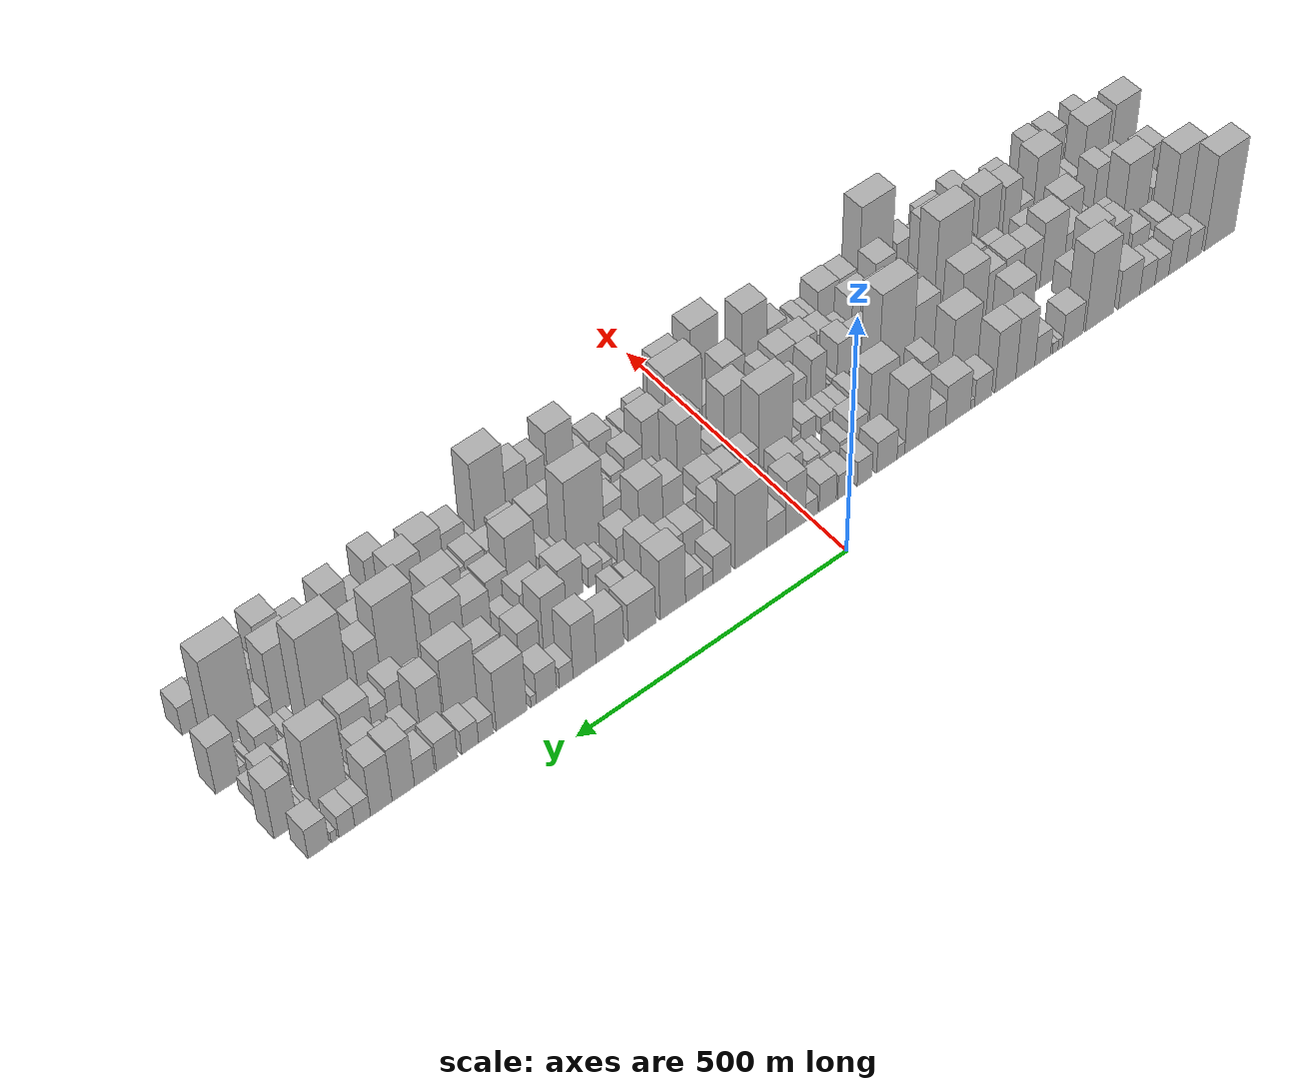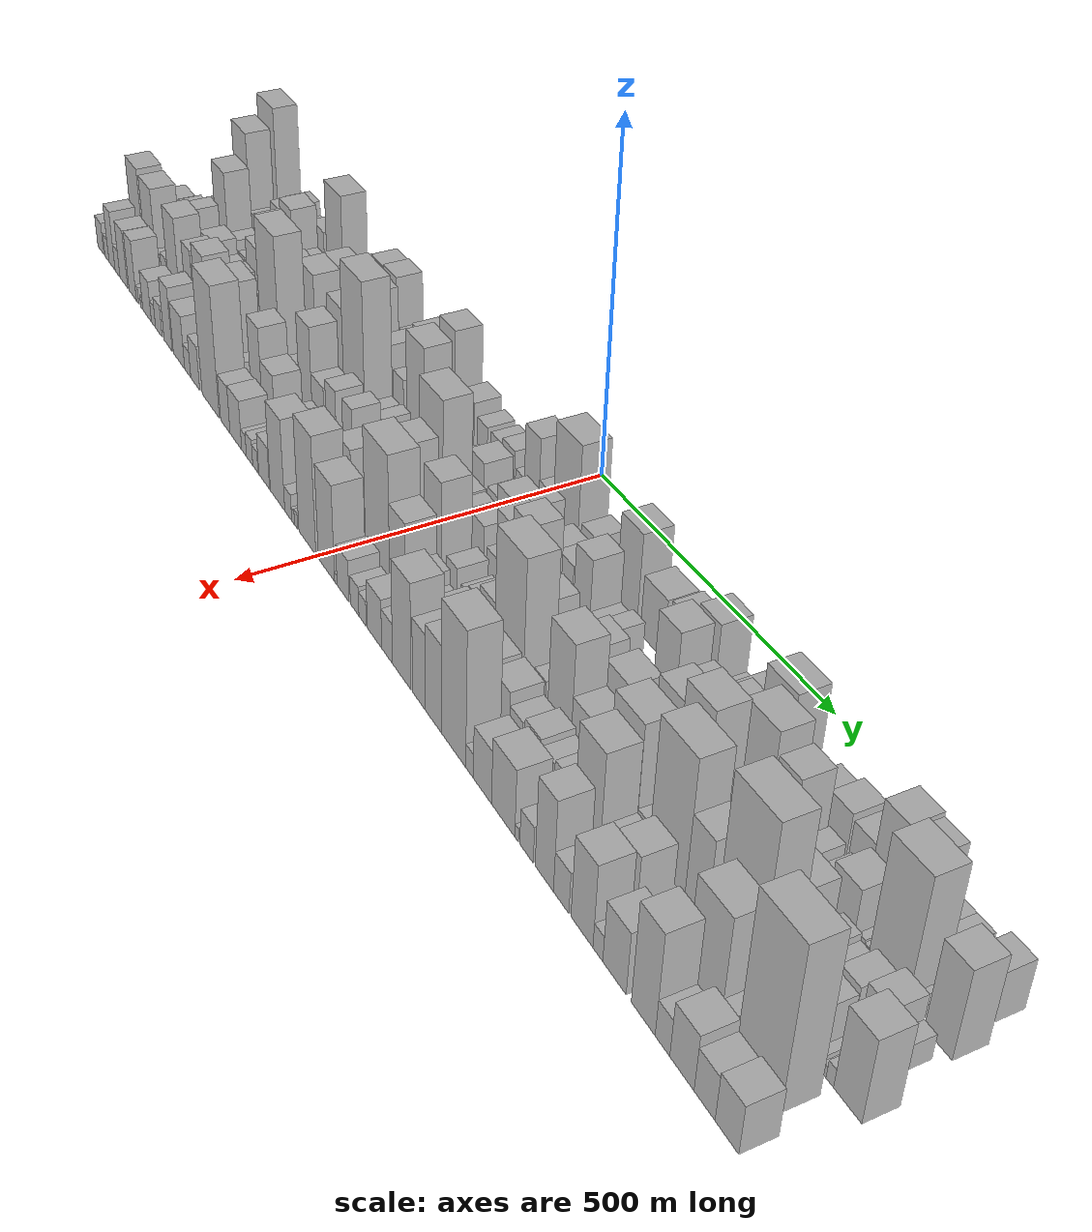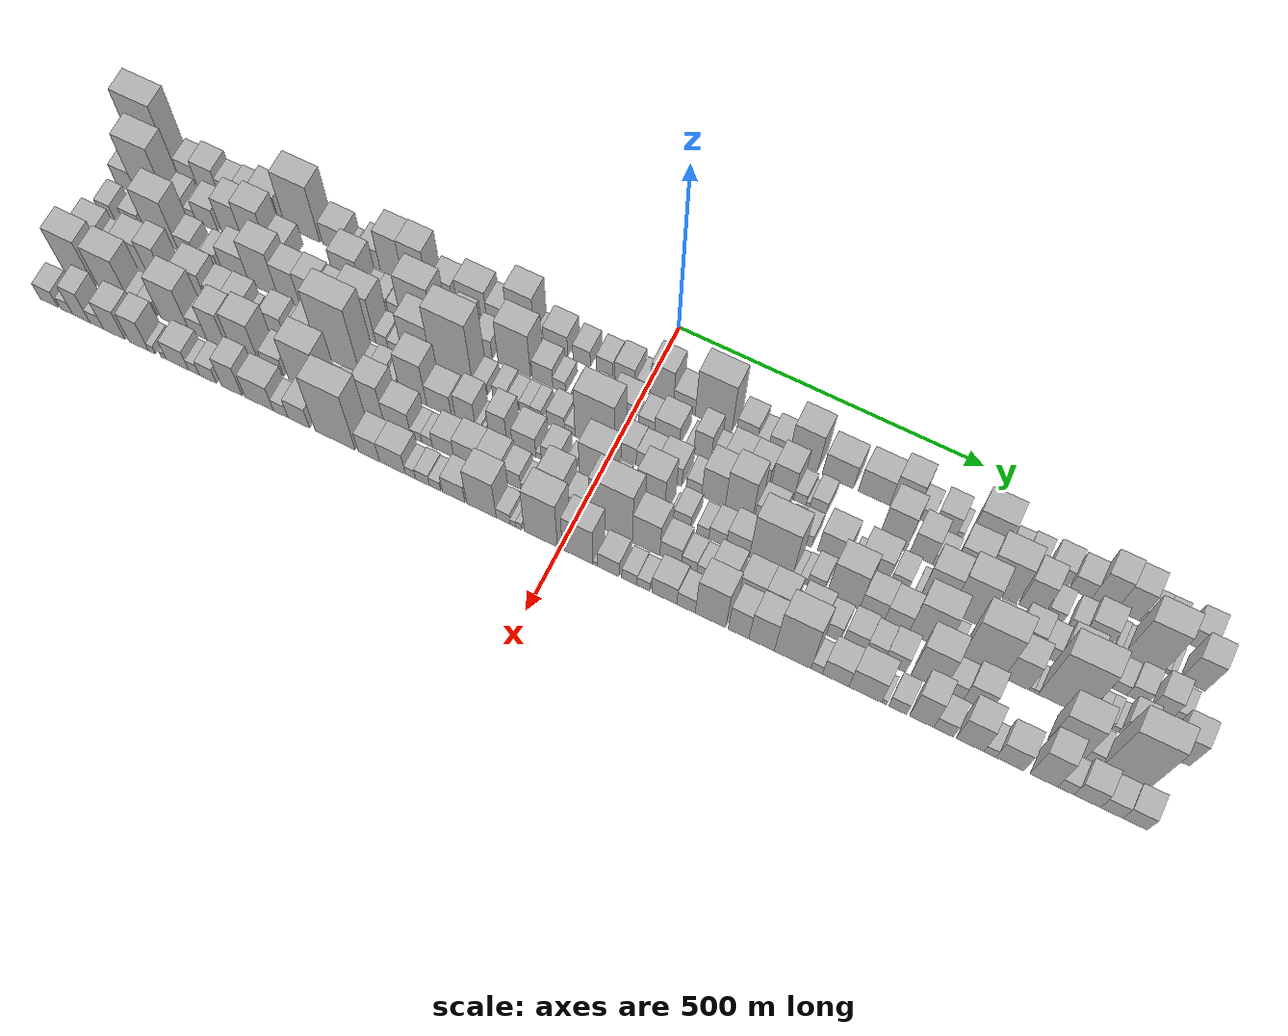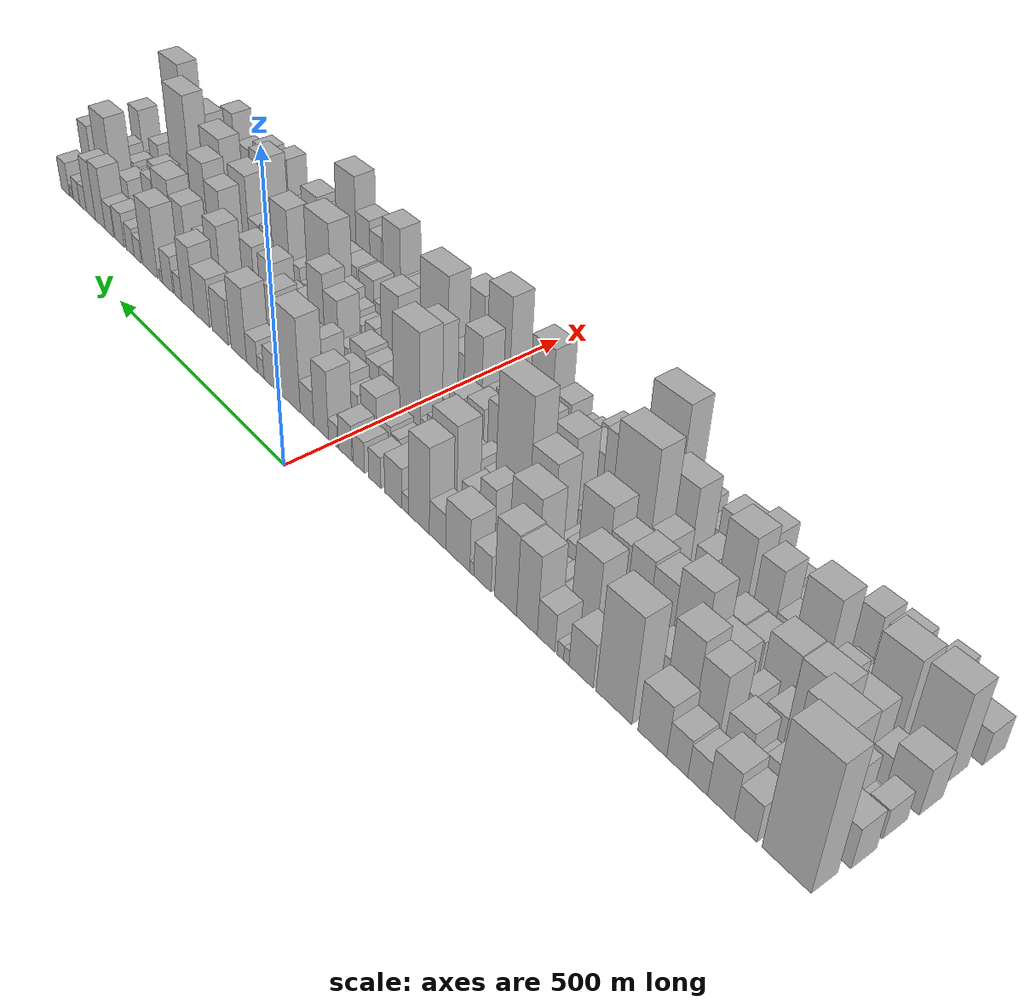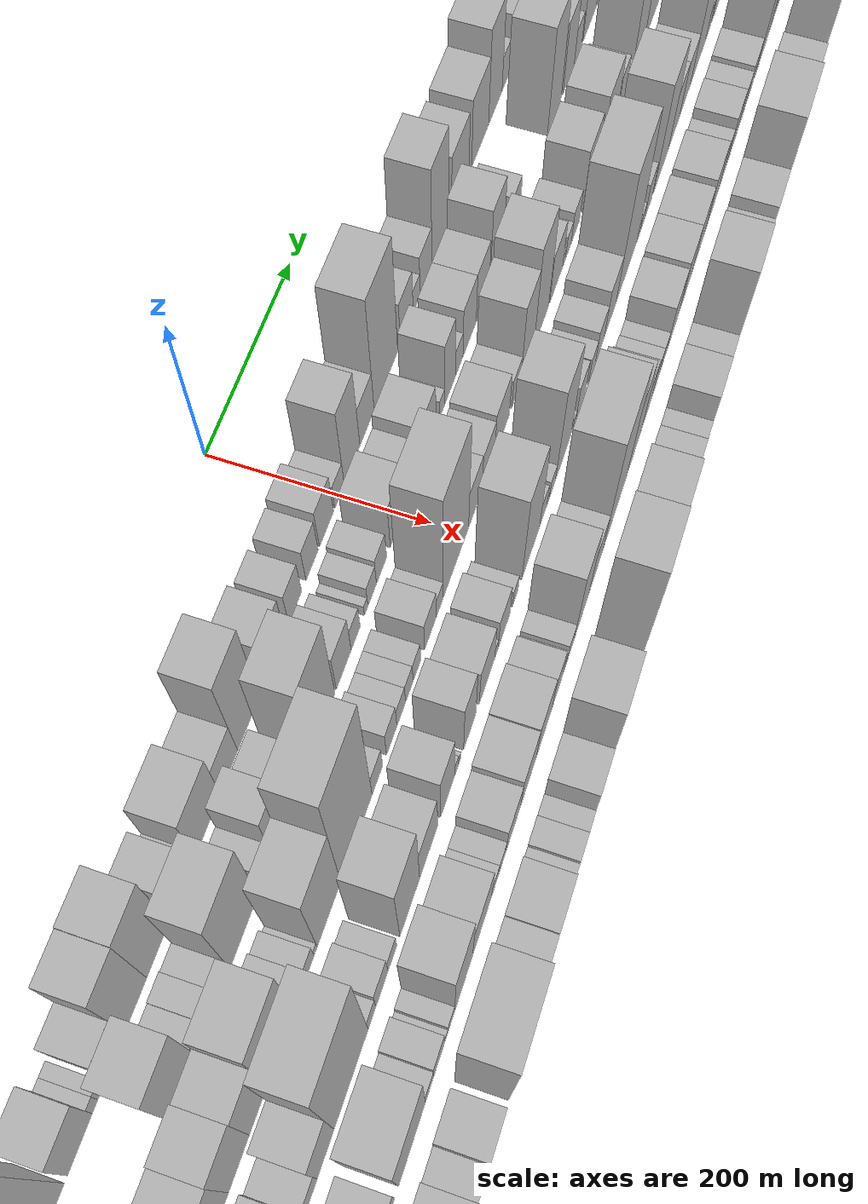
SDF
<sdf version="1.6">
 <world name="default">
  <scene>
   <sky><clouds><speed>12</speed></clouds></sky>
   <ambient>0.4 0.4 0.4 1</ambient>
   <background>0.7 0.7 0.7 1</background>
   <shadows>1</shadows>
  </scene>
  <gravity>0 0 -9.8066</gravity>
  <magnetic_field>6e-06 2.3e-05 -4.2e-05</magnetic_field>
  <physics default="0" name="default_physics" type="ode">
   <ode>
    <solver>
     <type>quick</type>
     <iters>10</iters>
     <sor>1.0</sor>
     <use_dynamic_moi_rescaling>0</use_dynamic_moi_rescaling>
    </solver>
    <constraints>
     <cfm>0</cfm>
     <erp>0.2</erp>
     <contact_max_correcting_vel>100</contact_max_correcting_vel>
     <contact_surface_layer>0.001</contact_surface_layer>
    </constraints>
   </ode>
   <max_step_size>0.004</max_step_size>
   <real_time_factor>1</real_time_factor>
   <real_time_update_rate>250</real_time_update_rate>
  </physics>
  <light name="sun" type="directional">
   <pose>0 0 10 0 0 0</pose>
   <diffuse>0.8 0.8 0.8 1</diffuse>
   <specular>0.2 0.2 0.2 1</specular>
   <attenuation>
    <range>1000</range>
    <constant>0.9</constant>
    <linear>0.01</linear>
    <quadratic>0.001</quadratic>
   </attenuation>
   <direction>-0.5 0.1 -0.9</direction>
  </light>
  <model name="building_1">
   <static>1</static>
   <pose>100.0000 -851.1541 0 0.000000 0.000000 0.000000</pose>
   <link name="link">
    <pose>0 0 103.50 0 0 0</pose>
    <collision name="collision"><geometry><box><size>40.0000 67.6917 207.0000</size></box></geometry></collision>
    <visual name="visual">
     <cast_shadows>0</cast_shadows>
     <geometry><box><size>40.0000 67.6917 207.0000</size></box></geometry>
     <material>
      <script>
       <uri>model://HANNAS_wall/materials/scripts</uri>
       <uri>model://HANNAS_wall/materials/textures</uri>
       <name>vrc/HANNAS_wall</name>
      </script>
     </material>
    </visual>
   </link>
  </model>
  <model name="building_2">
   <static>1</static>
   <pose>100.0000 -793.8154 0 0.000000 0.000000 0.000000</pose>
   <link name="link">
    <pose>0 0 30.00 0 0 0</pose>
    <collision name="collision"><geometry><box><size>40.0000 32.9858 60.0000</size></box></geometry></collision>
    <visual name="visual">
     <cast_shadows>0</cast_shadows>
     <geometry><box><size>40.0000 32.9858 60.0000</size></box></geometry>
     <material>
      <script>
       <uri>model://HANNAS_wall/materials/scripts</uri>
       <uri>model://HANNAS_wall/materials/textures</uri>
       <name>vrc/HANNAS_wall</name>
      </script>
     </material>
    </visual>
   </link>
  </model>
  <model name="building_3">
   <static>1</static>
   <pose>100.0000 -757.5941 0 0.000000 0.000000 0.000000</pose>
   <link name="link">
    <pose>0 0 39.00 0 0 0</pose>
    <collision name="collision"><geometry><box><size>40.0000 39.4568 78.0000</size></box></geometry></collision>
    <visual name="visual">
     <cast_shadows>0</cast_shadows>
     <geometry><box><size>40.0000 39.4568 78.0000</size></box></geometry>
     <material>
      <script>
       <uri>model://HANNAS_wall/materials/scripts</uri>
       <uri>model://HANNAS_wall/materials/textures</uri>
       <name>vrc/HANNAS_wall</name>
      </script>
     </material>
    </visual>
   </link>
  </model>
  <model name="building_4">
   <static>1</static>
   <pose>100.0000 -722.7467 0 0.000000 0.000000 0.000000</pose>
   <link name="link">
    <pose>0 0 27.00 0 0 0</pose>
    <collision name="collision"><geometry><box><size>40.0000 30.2380 54.0000</size></box></geometry></collision>
    <visual name="visual">
     <cast_shadows>0</cast_shadows>
     <geometry><box><size>40.0000 30.2380 54.0000</size></box></geometry>
     <material>
      <script>
       <uri>model://HANNAS_wall/materials/scripts</uri>
       <uri>model://HANNAS_wall/materials/textures</uri>
       <name>vrc/HANNAS_wall</name>
      </script>
     </material>
    </visual>
   </link>
  </model>
  <model name="building_5">
   <static>1</static>
   <pose>100.0000 -691.2329 0 0.000000 0.000000 0.000000</pose>
   <link name="link">
    <pose>0 0 30.00 0 0 0</pose>
    <collision name="collision"><geometry><box><size>40.0000 32.7896 60.0000</size></box></geometry></collision>
    <visual name="visual">
     <cast_shadows>0</cast_shadows>
     <geometry><box><size>40.0000 32.7896 60.0000</size></box></geometry>
     <material>
      <script>
       <uri>model://HANNAS_wall/materials/scripts</uri>
       <uri>model://HANNAS_wall/materials/textures</uri>
       <name>vrc/HANNAS_wall</name>
      </script>
     </material>
    </visual>
   </link>
  </model>
  <model name="building_6">
   <static>1</static>
   <pose>100.0000 -651.5269 0 0.000000 0.000000 0.000000</pose>
   <link name="link">
    <pose>0 0 42.00 0 0 0</pose>
    <collision name="collision"><geometry><box><size>40.0000 46.6224 84.0000</size></box></geometry></collision>
    <visual name="visual">
     <cast_shadows>0</cast_shadows>
     <geometry><box><size>40.0000 46.6224 84.0000</size></box></geometry>
     <material>
      <script>
       <uri>model://HANNAS_wall/materials/scripts</uri>
       <uri>model://HANNAS_wall/materials/textures</uri>
       <name>vrc/HANNAS_wall</name>
      </script>
     </material>
    </visual>
   </link>
  </model>
  <model name="building_7">
   <static>1</static>
   <pose>100.0000 -587.7156 0 0.000000 0.000000 0.000000</pose>
   <link name="link">
    <pose>0 0 87.00 0 0 0</pose>
    <collision name="collision"><geometry><box><size>40.0000 61.0001 174.0000</size></box></geometry></collision>
    <visual name="visual">
     <cast_shadows>0</cast_shadows>
     <geometry><box><size>40.0000 61.0001 174.0000</size></box></geometry>
     <material>
      <script>
       <uri>model://HANNAS_wall/materials/scripts</uri>
       <uri>model://HANNAS_wall/materials/textures</uri>
       <name>vrc/HANNAS_wall</name>
      </script>
     </material>
    </visual>
   </link>
  </model>
  <model name="building_8">
   <static>1</static>
   <pose>100.0000 -530.6636 0 0.000000 0.000000 0.000000</pose>
   <link name="link">
    <pose>0 0 36.00 0 0 0</pose>
    <collision name="collision"><geometry><box><size>40.0000 43.1039 72.0000</size></box></geometry></collision>
    <visual name="visual">
     <cast_shadows>0</cast_shadows>
     <geometry><box><size>40.0000 43.1039 72.0000</size></box></geometry>
     <material>
      <script>
       <uri>model://HANNAS_wall/materials/scripts</uri>
       <uri>model://HANNAS_wall/materials/textures</uri>
       <name>vrc/HANNAS_wall</name>
      </script>
     </material>
    </visual>
   </link>
  </model>
  <model name="building_9">
   <static>1</static>
   <pose>100.0000 -504.2297 0 0.000000 0.000000 0.000000</pose>
   <link name="link">
    <pose>0 0 12.00 0 0 0</pose>
    <collision name="collision"><geometry><box><size>40.0000 9.7638 24.0000</size></box></geometry></collision>
    <visual name="visual">
     <cast_shadows>0</cast_shadows>
     <geometry><box><size>40.0000 9.7638 24.0000</size></box></geometry>
     <material>
      <script>
       <uri>model://HANNAS_wall/materials/scripts</uri>
       <uri>model://HANNAS_wall/materials/textures</uri>
       <name>vrc/HANNAS_wall</name>
      </script>
     </material>
    </visual>
   </link>
  </model>
  <model name="building_10">
   <static>1</static>
   <pose>100.0000 -493.4084 0 0.000000 0.000000 0.000000</pose>
   <link name="link">
    <pose>0 0 12.00 0 0 0</pose>
    <collision name="collision"><geometry><box><size>40.0000 11.8788 24.0000</size></box></geometry></collision>
    <visual name="visual">
     <cast_shadows>0</cast_shadows>
     <geometry><box><size>40.0000 11.8788 24.0000</size></box></geometry>
     <material>
      <script>
       <uri>model://HANNAS_wall/materials/scripts</uri>
       <uri>model://HANNAS_wall/materials/textures</uri>
       <name>vrc/HANNAS_wall</name>
      </script>
     </material>
    </visual>
   </link>
  </model>
  <model name="building_11">
   <static>1</static>
   <pose>100.0000 -467.0780 0 0.000000 0.000000 0.000000</pose>
   <link name="link">
    <pose>0 0 31.50 0 0 0</pose>
    <collision name="collision"><geometry><box><size>40.0000 32.7820 63.0000</size></box></geometry></collision>
    <visual name="visual">
     <cast_shadows>0</cast_shadows>
     <geometry><box><size>40.0000 32.7820 63.0000</size></box></geometry>
     <material>
      <script>
       <uri>model://HANNAS_wall/materials/scripts</uri>
       <uri>model://HANNAS_wall/materials/textures</uri>
       <name>vrc/HANNAS_wall</name>
      </script>
     </material>
    </visual>
   </link>
  </model>
  <model name="building_12">
   <static>1</static>
   <pose>100.0000 -430.7783 0 0.000000 0.000000 0.000000</pose>
   <link name="link">
    <pose>0 0 66.00 0 0 0</pose>
    <collision name="collision"><geometry><box><size>40.0000 39.8175 132.0000</size></box></geometry></collision>
    <visual name="visual">
     <cast_shadows>0</cast_shadows>
     <geometry><box><size>40.0000 39.8175 132.0000</size></box></geometry>
     <material>
      <script>
       <uri>model://HANNAS_wall/materials/scripts</uri>
       <uri>model://HANNAS_wall/materials/textures</uri>
       <name>vrc/HANNAS_wall</name>
      </script>
     </material>
    </visual>
   </link>
  </model>
  <model name="building_13">
   <static>1</static>
   <pose>100.0000 -389.3200 0 0.000000 0.000000 0.000000</pose>
   <link name="link">
    <pose>0 0 67.50 0 0 0</pose>
    <collision name="collision"><geometry><box><size>40.0000 43.0991 135.0000</size></box></geometry></collision>
    <visual name="visual">
     <cast_shadows>0</cast_shadows>
     <geometry><box><size>40.0000 43.0991 135.0000</size></box></geometry>
     <material>
      <script>
       <uri>model://HANNAS_wall/materials/scripts</uri>
       <uri>model://HANNAS_wall/materials/textures</uri>
       <name>vrc/HANNAS_wall</name>
      </script>
     </material>
    </visual>
   </link>
  </model>
  <model name="building_14">
   <static>1</static>
   <pose>100.0000 -343.1972 0 0.000000 0.000000 0.000000</pose>
   <link name="link">
    <pose>0 0 30.00 0 0 0</pose>
    <collision name="collision"><geometry><box><size>40.0000 35.1464 60.0000</size></box></geometry></collision>
    <visual name="visual">
     <cast_shadows>0</cast_shadows>
     <geometry><box><size>40.0000 35.1464 60.0000</size></box></geometry>
     <material>
      <script>
       <uri>model://HANNAS_wall/materials/scripts</uri>
       <uri>model://HANNAS_wall/materials/textures</uri>
       <name>vrc/HANNAS_wall</name>
      </script>
     </material>
    </visual>
   </link>
  </model>
  <model name="building_15">
   <static>1</static>
   <pose>100.0000 -321.4226 0 0.000000 0.000000 0.000000</pose>
   <link name="link">
    <pose>0 0 10.50 0 0 0</pose>
    <collision name="collision"><geometry><box><size>40.0000 8.4029 21.0000</size></box></geometry></collision>
    <visual name="visual">
     <cast_shadows>0</cast_shadows>
     <geometry><box><size>40.0000 8.4029 21.0000</size></box></geometry>
     <material>
      <script>
       <uri>model://HANNAS_wall/materials/scripts</uri>
       <uri>model://HANNAS_wall/materials/textures</uri>
       <name>vrc/HANNAS_wall</name>
      </script>
     </material>
    </visual>
   </link>
  </model>
  <model name="building_16">
   <static>1</static>
   <pose>100.0000 -291.7921 0 0.000000 0.000000 0.000000</pose>
   <link name="link">
    <pose>0 0 45.00 0 0 0</pose>
    <collision name="collision"><geometry><box><size>40.0000 50.8580 90.0000</size></box></geometry></collision>
    <visual name="visual">
     <cast_shadows>0</cast_shadows>
     <geometry><box><size>40.0000 50.8580 90.0000</size></box></geometry>
     <material>
      <script>
       <uri>model://HANNAS_wall/materials/scripts</uri>
       <uri>model://HANNAS_wall/materials/textures</uri>
       <name>vrc/HANNAS_wall</name>
      </script>
     </material>
    </visual>
   </link>
  </model>
  <model name="building_17">
   <static>1</static>
   <pose>100.0000 -248.3700 0 0.000000 0.000000 0.000000</pose>
   <link name="link">
    <pose>0 0 30.00 0 0 0</pose>
    <collision name="collision"><geometry><box><size>40.0000 35.9863 60.0000</size></box></geometry></collision>
    <visual name="visual">
     <cast_shadows>0</cast_shadows>
     <geometry><box><size>40.0000 35.9863 60.0000</size></box></geometry>
     <material>
      <script>
       <uri>model://HANNAS_wall/materials/scripts</uri>
       <uri>model://HANNAS_wall/materials/textures</uri>
       <name>vrc/HANNAS_wall</name>
      </script>
     </material>
    </visual>
   </link>
  </model>
  <model name="building_18">
   <static>1</static>
   <pose>100.0000 -207.3975 0 0.000000 0.000000 0.000000</pose>
   <link name="link">
    <pose>0 0 73.50 0 0 0</pose>
    <collision name="collision"><geometry><box><size>40.0000 45.9587 147.0000</size></box></geometry></collision>
    <visual name="visual">
     <cast_shadows>0</cast_shadows>
     <geometry><box><size>40.0000 45.9587 147.0000</size></box></geometry>
     <material>
      <script>
       <uri>model://HANNAS_wall/materials/scripts</uri>
       <uri>model://HANNAS_wall/materials/textures</uri>
       <name>vrc/HANNAS_wall</name>
      </script>
     </material>
    </visual>
   </link>
  </model>
  <model name="building_19">
   <static>1</static>
   <pose>100.0000 -176.7365 0 0.000000 0.000000 0.000000</pose>
   <link name="link">
    <pose>0 0 15.00 0 0 0</pose>
    <collision name="collision"><geometry><box><size>40.0000 15.3634 30.0000</size></box></geometry></collision>
    <visual name="visual">
     <cast_shadows>0</cast_shadows>
     <geometry><box><size>40.0000 15.3634 30.0000</size></box></geometry>
     <material>
      <script>
       <uri>model://HANNAS_wall/materials/scripts</uri>
       <uri>model://HANNAS_wall/materials/textures</uri>
       <name>vrc/HANNAS_wall</name>
      </script>
     </material>
    </visual>
   </link>
  </model>
  <model name="building_20">
   <static>1</static>
   <pose>100.0000 -148.7223 0 0.000000 0.000000 0.000000</pose>
   <link name="link">
    <pose>0 0 34.50 0 0 0</pose>
    <collision name="collision"><geometry><box><size>40.0000 40.6649 69.0000</size></box></geometry></collision>
    <visual name="visual">
     <cast_shadows>0</cast_shadows>
     <geometry><box><size>40.0000 40.6649 69.0000</size></box></geometry>
     <material>
      <script>
       <uri>model://HANNAS_wall/materials/scripts</uri>
       <uri>model://HANNAS_wall/materials/textures</uri>
       <name>vrc/HANNAS_wall</name>
      </script>
     </material>
    </visual>
   </link>
  </model>
  <model name="building_21">
   <static>1</static>
   <pose>100.0000 -104.7841 0 0.000000 0.000000 0.000000</pose>
   <link name="link">
    <pose>0 0 27.00 0 0 0</pose>
    <collision name="collision"><geometry><box><size>40.0000 29.2116 54.0000</size></box></geometry></collision>
    <visual name="visual">
     <cast_shadows>0</cast_shadows>
     <geometry><box><size>40.0000 29.2116 54.0000</size></box></geometry>
     <material>
      <script>
       <uri>model://HANNAS_wall/materials/scripts</uri>
       <uri>model://HANNAS_wall/materials/textures</uri>
       <name>vrc/HANNAS_wall</name>
      </script>
     </material>
    </visual>
   </link>
  </model>
  <model name="building_22">
   <static>1</static>
   <pose>100.0000 -66.1163 0 0.000000 0.000000 0.000000</pose>
   <link name="link">
    <pose>0 0 27.00 0 0 0</pose>
    <collision name="collision"><geometry><box><size>40.0000 28.1240 54.0000</size></box></geometry></collision>
    <visual name="visual">
     <cast_shadows>0</cast_shadows>
     <geometry><box><size>40.0000 28.1240 54.0000</size></box></geometry>
     <material>
      <script>
       <uri>model://HANNAS_wall/materials/scripts</uri>
       <uri>model://HANNAS_wall/materials/textures</uri>
       <name>vrc/HANNAS_wall</name>
      </script>
     </material>
    </visual>
   </link>
  </model>
  <model name="building_23">
   <static>1</static>
   <pose>100.0000 -32.3615 0 0.000000 0.000000 0.000000</pose>
   <link name="link">
    <pose>0 0 31.50 0 0 0</pose>
    <collision name="collision"><geometry><box><size>40.0000 33.3856 63.0000</size></box></geometry></collision>
    <visual name="visual">
     <cast_shadows>0</cast_shadows>
     <geometry><box><size>40.0000 33.3856 63.0000</size></box></geometry>
     <material>
      <script>
       <uri>model://HANNAS_wall/materials/scripts</uri>
       <uri>model://HANNAS_wall/materials/textures</uri>
       <name>vrc/HANNAS_wall</name>
      </script>
     </material>
    </visual>
   </link>
  </model>
  <model name="building_24">
   <static>1</static>
   <pose>100.0000 -1.1424 0 0.000000 0.000000 0.000000</pose>
   <link name="link">
    <pose>0 0 19.50 0 0 0</pose>
    <collision name="collision"><geometry><box><size>40.0000 23.0525 39.0000</size></box></geometry></collision>
    <visual name="visual">
     <cast_shadows>0</cast_shadows>
     <geometry><box><size>40.0000 23.0525 39.0000</size></box></geometry>
     <material>
      <script>
       <uri>model://HANNAS_wall/materials/scripts</uri>
       <uri>model://HANNAS_wall/materials/textures</uri>
       <name>vrc/HANNAS_wall</name>
      </script>
     </material>
    </visual>
   </link>
  </model>
  <model name="building_25">
   <static>1</static>
   <pose>100.0000 29.5940 0 0.000000 0.000000 0.000000</pose>
   <link name="link">
    <pose>0 0 60.00 0 0 0</pose>
    <collision name="collision"><geometry><box><size>40.0000 38.4205 120.0000</size></box></geometry></collision>
    <visual name="visual">
     <cast_shadows>0</cast_shadows>
     <geometry><box><size>40.0000 38.4205 120.0000</size></box></geometry>
     <material>
      <script>
       <uri>model://HANNAS_wall/materials/scripts</uri>
       <uri>model://HANNAS_wall/materials/textures</uri>
       <name>vrc/HANNAS_wall</name>
      </script>
     </material>
    </visual>
   </link>
  </model>
  <model name="building_26">
   <static>1</static>
   <pose>100.0000 66.7108 0 0.000000 0.000000 0.000000</pose>
   <link name="link">
    <pose>0 0 30.00 0 0 0</pose>
    <collision name="collision"><geometry><box><size>40.0000 35.8131 60.0000</size></box></geometry></collision>
    <visual name="visual">
     <cast_shadows>0</cast_shadows>
     <geometry><box><size>40.0000 35.8131 60.0000</size></box></geometry>
     <material>
      <script>
       <uri>model://HANNAS_wall/materials/scripts</uri>
       <uri>model://HANNAS_wall/materials/textures</uri>
       <name>vrc/HANNAS_wall</name>
      </script>
     </material>
    </visual>
   </link>
  </model>
  <model name="building_27">
   <static>1</static>
   <pose>100.0000 114.8722 0 0.000000 0.000000 0.000000</pose>
   <link name="link">
    <pose>0 0 84.00 0 0 0</pose>
    <collision name="collision"><geometry><box><size>40.0000 60.5097 168.0000</size></box></geometry></collision>
    <visual name="visual">
     <cast_shadows>0</cast_shadows>
     <geometry><box><size>40.0000 60.5097 168.0000</size></box></geometry>
     <material>
      <script>
       <uri>model://HANNAS_wall/materials/scripts</uri>
       <uri>model://HANNAS_wall/materials/textures</uri>
       <name>vrc/HANNAS_wall</name>
      </script>
     </material>
    </visual>
   </link>
  </model>
  <model name="building_28">
   <static>1</static>
   <pose>100.0000 169.2701 0 0.000000 0.000000 0.000000</pose>
   <link name="link">
    <pose>0 0 31.50 0 0 0</pose>
    <collision name="collision"><geometry><box><size>40.0000 34.2860 63.0000</size></box></geometry></collision>
    <visual name="visual">
     <cast_shadows>0</cast_shadows>
     <geometry><box><size>40.0000 34.2860 63.0000</size></box></geometry>
     <material>
      <script>
       <uri>model://HANNAS_wall/materials/scripts</uri>
       <uri>model://HANNAS_wall/materials/textures</uri>
       <name>vrc/HANNAS_wall</name>
      </script>
     </material>
    </visual>
   </link>
  </model>
  <model name="building_29">
   <static>1</static>
   <pose>100.0000 195.7742 0 0.000000 0.000000 0.000000</pose>
   <link name="link">
    <pose>0 0 16.50 0 0 0</pose>
    <collision name="collision"><geometry><box><size>40.0000 18.7223 33.0000</size></box></geometry></collision>
    <visual name="visual">
     <cast_shadows>0</cast_shadows>
     <geometry><box><size>40.0000 18.7223 33.0000</size></box></geometry>
     <material>
      <script>
       <uri>model://HANNAS_wall/materials/scripts</uri>
       <uri>model://HANNAS_wall/materials/textures</uri>
       <name>vrc/HANNAS_wall</name>
      </script>
     </material>
    </visual>
   </link>
  </model>
  <model name="building_30">
   <static>1</static>
   <pose>100.0000 221.3169 0 0.000000 0.000000 0.000000</pose>
   <link name="link">
    <pose>0 0 28.50 0 0 0</pose>
    <collision name="collision"><geometry><box><size>40.0000 32.3630 57.0000</size></box></geometry></collision>
    <visual name="visual">
     <cast_shadows>0</cast_shadows>
     <geometry><box><size>40.0000 32.3630 57.0000</size></box></geometry>
     <material>
      <script>
       <uri>model://HANNAS_wall/materials/scripts</uri>
       <uri>model://HANNAS_wall/materials/textures</uri>
       <name>vrc/HANNAS_wall</name>
      </script>
     </material>
    </visual>
   </link>
  </model>
  <model name="building_31">
   <static>1</static>
   <pose>100.0000 260.9677 0 0.000000 0.000000 0.000000</pose>
   <link name="link">
    <pose>0 0 67.50 0 0 0</pose>
    <collision name="collision"><geometry><box><size>40.0000 46.9386 135.0000</size></box></geometry></collision>
    <visual name="visual">
     <cast_shadows>0</cast_shadows>
     <geometry><box><size>40.0000 46.9386 135.0000</size></box></geometry>
     <material>
      <script>
       <uri>model://HANNAS_wall/materials/scripts</uri>
       <uri>model://HANNAS_wall/materials/textures</uri>
       <name>vrc/HANNAS_wall</name>
      </script>
     </material>
    </visual>
   </link>
  </model>
  <model name="building_32">
   <static>1</static>
   <pose>100.0000 317.5003 0 0.000000 0.000000 0.000000</pose>
   <link name="link">
    <pose>0 0 42.00 0 0 0</pose>
    <collision name="collision"><geometry><box><size>40.0000 50.1265 84.0000</size></box></geometry></collision>
    <visual name="visual">
     <cast_shadows>0</cast_shadows>
     <geometry><box><size>40.0000 50.1265 84.0000</size></box></geometry>
     <material>
      <script>
       <uri>model://HANNAS_wall/materials/scripts</uri>
       <uri>model://HANNAS_wall/materials/textures</uri>
       <name>vrc/HANNAS_wall</name>
      </script>
     </material>
    </visual>
   </link>
  </model>
  <model name="building_33">
   <static>1</static>
   <pose>100.0000 375.7238 0 0.000000 0.000000 0.000000</pose>
   <link name="link">
    <pose>0 0 45.00 0 0 0</pose>
    <collision name="collision"><geometry><box><size>40.0000 50.3206 90.0000</size></box></geometry></collision>
    <visual name="visual">
     <cast_shadows>0</cast_shadows>
     <geometry><box><size>40.0000 50.3206 90.0000</size></box></geometry>
     <material>
      <script>
       <uri>model://HANNAS_wall/materials/scripts</uri>
       <uri>model://HANNAS_wall/materials/textures</uri>
       <name>vrc/HANNAS_wall</name>
      </script>
     </material>
    </visual>
   </link>
  </model>
  <model name="building_34">
   <static>1</static>
   <pose>100.0000 421.3314 0 0.000000 0.000000 0.000000</pose>
   <link name="link">
    <pose>0 0 61.50 0 0 0</pose>
    <collision name="collision"><geometry><box><size>40.0000 40.8947 123.0000</size></box></geometry></collision>
    <visual name="visual">
     <cast_shadows>0</cast_shadows>
     <geometry><box><size>40.0000 40.8947 123.0000</size></box></geometry>
     <material>
      <script>
       <uri>model://HANNAS_wall/materials/scripts</uri>
       <uri>model://HANNAS_wall/materials/textures</uri>
       <name>vrc/HANNAS_wall</name>
      </script>
     </material>
    </visual>
   </link>
  </model>
  <model name="building_35">
   <static>1</static>
   <pose>100.0000 454.0095 0 0.000000 0.000000 0.000000</pose>
   <link name="link">
    <pose>0 0 22.50 0 0 0</pose>
    <collision name="collision"><geometry><box><size>40.0000 24.4614 45.0000</size></box></geometry></collision>
    <visual name="visual">
     <cast_shadows>0</cast_shadows>
     <geometry><box><size>40.0000 24.4614 45.0000</size></box></geometry>
     <material>
      <script>
       <uri>model://HANNAS_wall/materials/scripts</uri>
       <uri>model://HANNAS_wall/materials/textures</uri>
       <name>vrc/HANNAS_wall</name>
      </script>
     </material>
    </visual>
   </link>
  </model>
  <model name="building_36">
   <static>1</static>
   <pose>100.0000 489.1352 0 0.000000 0.000000 0.000000</pose>
   <link name="link">
    <pose>0 0 34.50 0 0 0</pose>
    <collision name="collision"><geometry><box><size>40.0000 35.7901 69.0000</size></box></geometry></collision>
    <visual name="visual">
     <cast_shadows>0</cast_shadows>
     <geometry><box><size>40.0000 35.7901 69.0000</size></box></geometry>
     <material>
      <script>
       <uri>model://HANNAS_wall/materials/scripts</uri>
       <uri>model://HANNAS_wall/materials/textures</uri>
       <name>vrc/HANNAS_wall</name>
      </script>
     </material>
    </visual>
   </link>
  </model>
  <model name="building_37">
   <static>1</static>
   <pose>100.0000 511.8533 0 0.000000 0.000000 0.000000</pose>
   <link name="link">
    <pose>0 0 12.00 0 0 0</pose>
    <collision name="collision"><geometry><box><size>40.0000 9.6461 24.0000</size></box></geometry></collision>
    <visual name="visual">
     <cast_shadows>0</cast_shadows>
     <geometry><box><size>40.0000 9.6461 24.0000</size></box></geometry>
     <material>
      <script>
       <uri>model://HANNAS_wall/materials/scripts</uri>
       <uri>model://HANNAS_wall/materials/textures</uri>
       <name>vrc/HANNAS_wall</name>
      </script>
     </material>
    </visual>
   </link>
  </model>
  <model name="building_38">
   <static>1</static>
   <pose>100.0000 550.4825 0 0.000000 0.000000 0.000000</pose>
   <link name="link">
    <pose>0 0 67.50 0 0 0</pose>
    <collision name="collision"><geometry><box><size>40.0000 53.6122 135.0000</size></box></geometry></collision>
    <visual name="visual">
     <cast_shadows>0</cast_shadows>
     <geometry><box><size>40.0000 53.6122 135.0000</size></box></geometry>
     <material>
      <script>
       <uri>model://HANNAS_wall/materials/scripts</uri>
       <uri>model://HANNAS_wall/materials/textures</uri>
       <name>vrc/HANNAS_wall</name>
      </script>
     </material>
    </visual>
   </link>
  </model>
  <model name="building_39">
   <static>1</static>
   <pose>100.0000 595.1342 0 0.000000 0.000000 0.000000</pose>
   <link name="link">
    <pose>0 0 22.50 0 0 0</pose>
    <collision name="collision"><geometry><box><size>40.0000 25.6913 45.0000</size></box></geometry></collision>
    <visual name="visual">
     <cast_shadows>0</cast_shadows>
     <geometry><box><size>40.0000 25.6913 45.0000</size></box></geometry>
     <material>
      <script>
       <uri>model://HANNAS_wall/materials/scripts</uri>
       <uri>model://HANNAS_wall/materials/textures</uri>
       <name>vrc/HANNAS_wall</name>
      </script>
     </material>
    </visual>
   </link>
  </model>
  <model name="building_40">
   <static>1</static>
   <pose>100.0000 622.6248 0 0.000000 0.000000 0.000000</pose>
   <link name="link">
    <pose>0 0 27.00 0 0 0</pose>
    <collision name="collision"><geometry><box><size>40.0000 29.2899 54.0000</size></box></geometry></collision>
    <visual name="visual">
     <cast_shadows>0</cast_shadows>
     <geometry><box><size>40.0000 29.2899 54.0000</size></box></geometry>
     <material>
      <script>
       <uri>model://HANNAS_wall/materials/scripts</uri>
       <uri>model://HANNAS_wall/materials/textures</uri>
       <name>vrc/HANNAS_wall</name>
      </script>
     </material>
    </visual>
   </link>
  </model>
  <model name="building_41">
   <static>1</static>
   <pose>100.0000 662.3822 0 0.000000 0.000000 0.000000</pose>
   <link name="link">
    <pose>0 0 33.00 0 0 0</pose>
    <collision name="collision"><geometry><box><size>40.0000 36.2250 66.0000</size></box></geometry></collision>
    <visual name="visual">
     <cast_shadows>0</cast_shadows>
     <geometry><box><size>40.0000 36.2250 66.0000</size></box></geometry>
     <material>
      <script>
       <uri>model://HANNAS_wall/materials/scripts</uri>
       <uri>model://HANNAS_wall/materials/textures</uri>
       <name>vrc/HANNAS_wall</name>
      </script>
     </material>
    </visual>
   </link>
  </model>
  <model name="building_42">
   <static>1</static>
   <pose>100.0000 700.5594 0 0.000000 0.000000 0.000000</pose>
   <link name="link">
    <pose>0 0 30.00 0 0 0</pose>
    <collision name="collision"><geometry><box><size>40.0000 34.1293 60.0000</size></box></geometry></collision>
    <visual name="visual">
     <cast_shadows>0</cast_shadows>
     <geometry><box><size>40.0000 34.1293 60.0000</size></box></geometry>
     <material>
      <script>
       <uri>model://HANNAS_wall/materials/scripts</uri>
       <uri>model://HANNAS_wall/materials/textures</uri>
       <name>vrc/HANNAS_wall</name>
      </script>
     </material>
    </visual>
   </link>
  </model>
  <model name="building_43">
   <static>1</static>
   <pose>100.0000 736.5330 0 0.000000 0.000000 0.000000</pose>
   <link name="link">
    <pose>0 0 60.00 0 0 0</pose>
    <collision name="collision"><geometry><box><size>40.0000 37.8179 120.0000</size></box></geometry></collision>
    <visual name="visual">
     <cast_shadows>0</cast_shadows>
     <geometry><box><size>40.0000 37.8179 120.0000</size></box></geometry>
     <material>
      <script>
       <uri>model://HANNAS_wall/materials/scripts</uri>
       <uri>model://HANNAS_wall/materials/textures</uri>
       <name>vrc/HANNAS_wall</name>
      </script>
     </material>
    </visual>
   </link>
  </model>
  <model name="building_44">
   <static>1</static>
   <pose>100.0000 773.5364 0 0.000000 0.000000 0.000000</pose>
   <link name="link">
    <pose>0 0 57.00 0 0 0</pose>
    <collision name="collision"><geometry><box><size>40.0000 36.1888 114.0000</size></box></geometry></collision>
    <visual name="visual">
     <cast_shadows>0</cast_shadows>
     <geometry><box><size>40.0000 36.1888 114.0000</size></box></geometry>
     <material>
      <script>
       <uri>model://HANNAS_wall/materials/scripts</uri>
       <uri>model://HANNAS_wall/materials/textures</uri>
       <name>vrc/HANNAS_wall</name>
      </script>
     </material>
    </visual>
   </link>
  </model>
  <model name="building_45">
   <static>1</static>
   <pose>100.0000 804.7815 0 0.000000 0.000000 0.000000</pose>
   <link name="link">
    <pose>0 0 24.00 0 0 0</pose>
    <collision name="collision"><geometry><box><size>40.0000 26.3016 48.0000</size></box></geometry></collision>
    <visual name="visual">
     <cast_shadows>0</cast_shadows>
     <geometry><box><size>40.0000 26.3016 48.0000</size></box></geometry>
     <material>
      <script>
       <uri>model://HANNAS_wall/materials/scripts</uri>
       <uri>model://HANNAS_wall/materials/textures</uri>
       <name>vrc/HANNAS_wall</name>
      </script>
     </material>
    </visual>
   </link>
  </model>
  <model name="building_46">
   <static>1</static>
   <pose>100.0000 831.1495 0 0.000000 0.000000 0.000000</pose>
   <link name="link">
    <pose>0 0 24.00 0 0 0</pose>
    <collision name="collision"><geometry><box><size>40.0000 26.4344 48.0000</size></box></geometry></collision>
    <visual name="visual">
     <cast_shadows>0</cast_shadows>
     <geometry><box><size>40.0000 26.4344 48.0000</size></box></geometry>
     <material>
      <script>
       <uri>model://HANNAS_wall/materials/scripts</uri>
       <uri>model://HANNAS_wall/materials/textures</uri>
       <name>vrc/HANNAS_wall</name>
      </script>
     </material>
    </visual>
   </link>
  </model>
  <model name="building_47">
   <static>1</static>
   <pose>100.0000 852.3052 0 0.000000 0.000000 0.000000</pose>
   <link name="link">
    <pose>0 0 12.00 0 0 0</pose>
    <collision name="collision"><geometry><box><size>40.0000 9.8770 24.0000</size></box></geometry></collision>
    <visual name="visual">
     <cast_shadows>0</cast_shadows>
     <geometry><box><size>40.0000 9.8770 24.0000</size></box></geometry>
     <material>
      <script>
       <uri>model://HANNAS_wall/materials/scripts</uri>
       <uri>model://HANNAS_wall/materials/textures</uri>
       <name>vrc/HANNAS_wall</name>
      </script>
     </material>
    </visual>
   </link>
  </model>
  <model name="building_48">
   <static>1</static>
   <pose>100.0000 877.6894 0 0.000000 0.000000 0.000000</pose>
   <link name="link">
    <pose>0 0 33.00 0 0 0</pose>
    <collision name="collision"><geometry><box><size>40.0000 34.8914 66.0000</size></box></geometry></collision>
    <visual name="visual">
     <cast_shadows>0</cast_shadows>
     <geometry><box><size>40.0000 34.8914 66.0000</size></box></geometry>
     <material>
      <script>
       <uri>model://HANNAS_wall/materials/scripts</uri>
       <uri>model://HANNAS_wall/materials/textures</uri>
       <name>vrc/HANNAS_wall</name>
      </script>
     </material>
    </visual>
   </link>
  </model>
  <model name="building_49">
   <static>1</static>
   <pose>155.0000 -871.9670 0 0.000000 0.000000 0.000000</pose>
   <link name="link">
    <pose>0 0 33.00 0 0 0</pose>
    <collision name="collision"><geometry><box><size>40.0000 36.0660 66.0000</size></box></geometry></collision>
    <visual name="visual">
     <cast_shadows>0</cast_shadows>
     <geometry><box><size>40.0000 36.0660 66.0000</size></box></geometry>
     <material>
      <script>
       <uri>model://HANNAS_wall/materials/scripts</uri>
       <uri>model://HANNAS_wall/materials/textures</uri>
       <name>vrc/HANNAS_wall</name>
      </script>
     </material>
    </visual>
   </link>
  </model>
  <model name="building_50">
   <static>1</static>
   <pose>155.0000 -823.6713 0 0.000000 0.000000 0.000000</pose>
   <link name="link">
    <pose>0 0 93.00 0 0 0</pose>
    <collision name="collision"><geometry><box><size>40.0000 60.5255 186.0000</size></box></geometry></collision>
    <visual name="visual">
     <cast_shadows>0</cast_shadows>
     <geometry><box><size>40.0000 60.5255 186.0000</size></box></geometry>
     <material>
      <script>
       <uri>model://HANNAS_wall/materials/scripts</uri>
       <uri>model://HANNAS_wall/materials/textures</uri>
       <name>vrc/HANNAS_wall</name>
      </script>
     </material>
    </visual>
   </link>
  </model>
  <model name="building_51">
   <static>1</static>
   <pose>155.0000 -778.5629 0 0.000000 0.000000 0.000000</pose>
   <link name="link">
    <pose>0 0 28.50 0 0 0</pose>
    <collision name="collision"><geometry><box><size>40.0000 29.6912 57.0000</size></box></geometry></collision>
    <visual name="visual">
     <cast_shadows>0</cast_shadows>
     <geometry><box><size>40.0000 29.6912 57.0000</size></box></geometry>
     <material>
      <script>
       <uri>model://HANNAS_wall/materials/scripts</uri>
       <uri>model://HANNAS_wall/materials/textures</uri>
       <name>vrc/HANNAS_wall</name>
      </script>
     </material>
    </visual>
   </link>
  </model>
  <model name="building_52">
   <static>1</static>
   <pose>155.0000 -754.5735 0 0.000000 0.000000 0.000000</pose>
   <link name="link">
    <pose>0 0 16.50 0 0 0</pose>
    <collision name="collision"><geometry><box><size>40.0000 18.2877 33.0000</size></box></geometry></collision>
    <visual name="visual">
     <cast_shadows>0</cast_shadows>
     <geometry><box><size>40.0000 18.2877 33.0000</size></box></geometry>
     <material>
      <script>
       <uri>model://HANNAS_wall/materials/scripts</uri>
       <uri>model://HANNAS_wall/materials/textures</uri>
       <name>vrc/HANNAS_wall</name>
      </script>
     </material>
    </visual>
   </link>
  </model>
  <model name="building_53">
   <static>1</static>
   <pose>155.0000 -726.1244 0 0.000000 0.000000 0.000000</pose>
   <link name="link">
    <pose>0 0 34.50 0 0 0</pose>
    <collision name="collision"><geometry><box><size>40.0000 38.6105 69.0000</size></box></geometry></collision>
    <visual name="visual">
     <cast_shadows>0</cast_shadows>
     <geometry><box><size>40.0000 38.6105 69.0000</size></box></geometry>
     <material>
      <script>
       <uri>model://HANNAS_wall/materials/scripts</uri>
       <uri>model://HANNAS_wall/materials/textures</uri>
       <name>vrc/HANNAS_wall</name>
      </script>
     </material>
    </visual>
   </link>
  </model>
  <model name="building_54">
   <static>1</static>
   <pose>155.0000 -679.6779 0 0.000000 0.000000 0.000000</pose>
   <link name="link">
    <pose>0 0 58.50 0 0 0</pose>
    <collision name="collision"><geometry><box><size>40.0000 38.2824 117.0000</size></box></geometry></collision>
    <visual name="visual">
     <cast_shadows>0</cast_shadows>
     <geometry><box><size>40.0000 38.2824 117.0000</size></box></geometry>
     <material>
      <script>
       <uri>model://HANNAS_wall/materials/scripts</uri>
       <uri>model://HANNAS_wall/materials/textures</uri>
       <name>vrc/HANNAS_wall</name>
      </script>
     </material>
    </visual>
   </link>
  </model>
  <model name="building_55">
   <static>1</static>
   <pose>155.0000 -637.8213 0 0.000000 0.000000 0.000000</pose>
   <link name="link">
    <pose>0 0 69.00 0 0 0</pose>
    <collision name="collision"><geometry><box><size>40.0000 45.4310 138.0000</size></box></geometry></collision>
    <visual name="visual">
     <cast_shadows>0</cast_shadows>
     <geometry><box><size>40.0000 45.4310 138.0000</size></box></geometry>
     <material>
      <script>
       <uri>model://HANNAS_wall/materials/scripts</uri>
       <uri>model://HANNAS_wall/materials/textures</uri>
       <name>vrc/HANNAS_wall</name>
      </script>
     </material>
    </visual>
   </link>
  </model>
  <model name="building_56">
   <static>1</static>
   <pose>155.0000 -596.8226 0 0.000000 0.000000 0.000000</pose>
   <link name="link">
    <pose>0 0 34.50 0 0 0</pose>
    <collision name="collision"><geometry><box><size>40.0000 36.5663 69.0000</size></box></geometry></collision>
    <visual name="visual">
     <cast_shadows>0</cast_shadows>
     <geometry><box><size>40.0000 36.5663 69.0000</size></box></geometry>
     <material>
      <script>
       <uri>model://HANNAS_wall/materials/scripts</uri>
       <uri>model://HANNAS_wall/materials/textures</uri>
       <name>vrc/HANNAS_wall</name>
      </script>
     </material>
    </visual>
   </link>
  </model>
  <model name="building_57">
   <static>1</static>
   <pose>155.0000 -472.8988 0 0.000000 0.000000 0.000000</pose>
   <link name="link">
    <pose>0 0 63.00 0 0 0</pose>
    <collision name="collision"><geometry><box><size>40.0000 47.0938 126.0000</size></box></geometry></collision>
    <visual name="visual">
     <cast_shadows>0</cast_shadows>
     <geometry><box><size>40.0000 47.0938 126.0000</size></box></geometry>
     <material>
      <script>
       <uri>model://HANNAS_wall/materials/scripts</uri>
       <uri>model://HANNAS_wall/materials/textures</uri>
       <name>vrc/HANNAS_wall</name>
      </script>
     </material>
    </visual>
   </link>
  </model>
  <model name="building_58">
   <static>1</static>
   <pose>155.0000 -439.5121 0 0.000000 0.000000 0.000000</pose>
   <link name="link">
    <pose>0 0 18.00 0 0 0</pose>
    <collision name="collision"><geometry><box><size>40.0000 19.6796 36.0000</size></box></geometry></collision>
    <visual name="visual">
     <cast_shadows>0</cast_shadows>
     <geometry><box><size>40.0000 19.6796 36.0000</size></box></geometry>
     <material>
      <script>
       <uri>model://HANNAS_wall/materials/scripts</uri>
       <uri>model://HANNAS_wall/materials/textures</uri>
       <name>vrc/HANNAS_wall</name>
      </script>
     </material>
    </visual>
   </link>
  </model>
  <model name="building_59">
   <static>1</static>
   <pose>155.0000 -418.4448 0 0.000000 0.000000 0.000000</pose>
   <link name="link">
    <pose>0 0 19.50 0 0 0</pose>
    <collision name="collision"><geometry><box><size>40.0000 22.4549 39.0000</size></box></geometry></collision>
    <visual name="visual">
     <cast_shadows>0</cast_shadows>
     <geometry><box><size>40.0000 22.4549 39.0000</size></box></geometry>
     <material>
      <script>
       <uri>model://HANNAS_wall/materials/scripts</uri>
       <uri>model://HANNAS_wall/materials/textures</uri>
       <name>vrc/HANNAS_wall</name>
      </script>
     </material>
    </visual>
   </link>
  </model>
  <model name="building_60">
   <static>1</static>
   <pose>155.0000 -396.4209 0 0.000000 0.000000 0.000000</pose>
   <link name="link">
    <pose>0 0 18.00 0 0 0</pose>
    <collision name="collision"><geometry><box><size>40.0000 21.5930 36.0000</size></box></geometry></collision>
    <visual name="visual">
     <cast_shadows>0</cast_shadows>
     <geometry><box><size>40.0000 21.5930 36.0000</size></box></geometry>
     <material>
      <script>
       <uri>model://HANNAS_wall/materials/scripts</uri>
       <uri>model://HANNAS_wall/materials/textures</uri>
       <name>vrc/HANNAS_wall</name>
      </script>
     </material>
    </visual>
   </link>
  </model>
  <model name="building_61">
   <static>1</static>
   <pose>155.0000 -357.1461 0 0.000000 0.000000 0.000000</pose>
   <link name="link">
    <pose>0 0 72.00 0 0 0</pose>
    <collision name="collision"><geometry><box><size>40.0000 56.9566 144.0000</size></box></geometry></collision>
    <visual name="visual">
     <cast_shadows>0</cast_shadows>
     <geometry><box><size>40.0000 56.9566 144.0000</size></box></geometry>
     <material>
      <script>
       <uri>model://HANNAS_wall/materials/scripts</uri>
       <uri>model://HANNAS_wall/materials/textures</uri>
       <name>vrc/HANNAS_wall</name>
      </script>
     </material>
    </visual>
   </link>
  </model>
  <model name="building_62">
   <static>1</static>
   <pose>155.0000 -310.1881 0 0.000000 0.000000 0.000000</pose>
   <link name="link">
    <pose>0 0 21.00 0 0 0</pose>
    <collision name="collision"><geometry><box><size>40.0000 22.9594 42.0000</size></box></geometry></collision>
    <visual name="visual">
     <cast_shadows>0</cast_shadows>
     <geometry><box><size>40.0000 22.9594 42.0000</size></box></geometry>
     <material>
      <script>
       <uri>model://HANNAS_wall/materials/scripts</uri>
       <uri>model://HANNAS_wall/materials/textures</uri>
       <name>vrc/HANNAS_wall</name>
      </script>
     </material>
    </visual>
   </link>
  </model>
  <model name="building_63">
   <static>1</static>
   <pose>155.0000 -282.5403 0 0.000000 0.000000 0.000000</pose>
   <link name="link">
    <pose>0 0 48.00 0 0 0</pose>
    <collision name="collision"><geometry><box><size>40.0000 32.3364 96.0000</size></box></geometry></collision>
    <visual name="visual">
     <cast_shadows>0</cast_shadows>
     <geometry><box><size>40.0000 32.3364 96.0000</size></box></geometry>
     <material>
      <script>
       <uri>model://HANNAS_wall/materials/scripts</uri>
       <uri>model://HANNAS_wall/materials/textures</uri>
       <name>vrc/HANNAS_wall</name>
      </script>
     </material>
    </visual>
   </link>
  </model>
  <model name="building_64">
   <static>1</static>
   <pose>155.0000 -243.5212 0 0.000000 0.000000 0.000000</pose>
   <link name="link">
    <pose>0 0 31.50 0 0 0</pose>
    <collision name="collision"><geometry><box><size>40.0000 31.7018 63.0000</size></box></geometry></collision>
    <visual name="visual">
     <cast_shadows>0</cast_shadows>
     <geometry><box><size>40.0000 31.7018 63.0000</size></box></geometry>
     <material>
      <script>
       <uri>model://HANNAS_wall/materials/scripts</uri>
       <uri>model://HANNAS_wall/materials/textures</uri>
       <name>vrc/HANNAS_wall</name>
      </script>
     </material>
    </visual>
   </link>
  </model>
  <model name="building_65">
   <static>1</static>
   <pose>155.0000 -190.1250 0 0.000000 0.000000 0.000000</pose>
   <link name="link">
    <pose>0 0 73.50 0 0 0</pose>
    <collision name="collision"><geometry><box><size>40.0000 55.0906 147.0000</size></box></geometry></collision>
    <visual name="visual">
     <cast_shadows>0</cast_shadows>
     <geometry><box><size>40.0000 55.0906 147.0000</size></box></geometry>
     <material>
      <script>
       <uri>model://HANNAS_wall/materials/scripts</uri>
       <uri>model://HANNAS_wall/materials/textures</uri>
       <name>vrc/HANNAS_wall</name>
      </script>
     </material>
    </visual>
   </link>
  </model>
  <model name="building_66">
   <static>1</static>
   <pose>155.0000 -142.3856 0 0.000000 0.000000 0.000000</pose>
   <link name="link">
    <pose>0 0 33.00 0 0 0</pose>
    <collision name="collision"><geometry><box><size>40.0000 34.3880 66.0000</size></box></geometry></collision>
    <visual name="visual">
     <cast_shadows>0</cast_shadows>
     <geometry><box><size>40.0000 34.3880 66.0000</size></box></geometry>
     <material>
      <script>
       <uri>model://HANNAS_wall/materials/scripts</uri>
       <uri>model://HANNAS_wall/materials/textures</uri>
       <name>vrc/HANNAS_wall</name>
      </script>
     </material>
    </visual>
   </link>
  </model>
  <model name="building_67">
   <static>1</static>
   <pose>155.0000 -114.5711 0 0.000000 0.000000 0.000000</pose>
   <link name="link">
    <pose>0 0 19.50 0 0 0</pose>
    <collision name="collision"><geometry><box><size>40.0000 21.2411 39.0000</size></box></geometry></collision>
    <visual name="visual">
     <cast_shadows>0</cast_shadows>
     <geometry><box><size>40.0000 21.2411 39.0000</size></box></geometry>
     <material>
      <script>
       <uri>model://HANNAS_wall/materials/scripts</uri>
       <uri>model://HANNAS_wall/materials/textures</uri>
       <name>vrc/HANNAS_wall</name>
      </script>
     </material>
    </visual>
   </link>
  </model>
  <model name="building_68">
   <static>1</static>
   <pose>155.0000 -89.7761 0 0.000000 0.000000 0.000000</pose>
   <link name="link">
    <pose>0 0 9.00 0 0 0</pose>
    <collision name="collision"><geometry><box><size>40.0000 8.3489 18.0000</size></box></geometry></collision>
    <visual name="visual">
     <cast_shadows>0</cast_shadows>
     <geometry><box><size>40.0000 8.3489 18.0000</size></box></geometry>
     <material>
      <script>
       <uri>model://HANNAS_wall/materials/scripts</uri>
       <uri>model://HANNAS_wall/materials/textures</uri>
       <name>vrc/HANNAS_wall</name>
      </script>
     </material>
    </visual>
   </link>
  </model>
  <model name="building_69">
   <static>1</static>
   <pose>155.0000 -75.3981 0 0.000000 0.000000 0.000000</pose>
   <link name="link">
    <pose>0 0 18.00 0 0 0</pose>
    <collision name="collision"><geometry><box><size>40.0000 20.4071 36.0000</size></box></geometry></collision>
    <visual name="visual">
     <cast_shadows>0</cast_shadows>
     <geometry><box><size>40.0000 20.4071 36.0000</size></box></geometry>
     <material>
      <script>
       <uri>model://HANNAS_wall/materials/scripts</uri>
       <uri>model://HANNAS_wall/materials/textures</uri>
       <name>vrc/HANNAS_wall</name>
      </script>
     </material>
    </visual>
   </link>
  </model>
  <model name="building_70">
   <static>1</static>
   <pose>155.0000 -52.7753 0 0.000000 0.000000 0.000000</pose>
   <link name="link">
    <pose>0 0 22.50 0 0 0</pose>
    <collision name="collision"><geometry><box><size>40.0000 24.8387 45.0000</size></box></geometry></collision>
    <visual name="visual">
     <cast_shadows>0</cast_shadows>
     <geometry><box><size>40.0000 24.8387 45.0000</size></box></geometry>
     <material>
      <script>
       <uri>model://HANNAS_wall/materials/scripts</uri>
       <uri>model://HANNAS_wall/materials/textures</uri>
       <name>vrc/HANNAS_wall</name>
      </script>
     </material>
    </visual>
   </link>
  </model>
  <model name="building_71">
   <static>1</static>
   <pose>155.0000 -11.5307 0 0.000000 0.000000 0.000000</pose>
   <link name="link">
    <pose>0 0 37.50 0 0 0</pose>
    <collision name="collision"><geometry><box><size>40.0000 39.6504 75.0000</size></box></geometry></collision>
    <visual name="visual">
     <cast_shadows>0</cast_shadows>
     <geometry><box><size>40.0000 39.6504 75.0000</size></box></geometry>
     <material>
      <script>
       <uri>model://HANNAS_wall/materials/scripts</uri>
       <uri>model://HANNAS_wall/materials/textures</uri>
       <name>vrc/HANNAS_wall</name>
      </script>
     </material>
    </visual>
   </link>
  </model>
  <model name="building_72">
   <static>1</static>
   <pose>155.0000 30.9175 0 0.000000 0.000000 0.000000</pose>
   <link name="link">
    <pose>0 0 24.00 0 0 0</pose>
    <collision name="collision"><geometry><box><size>40.0000 27.2462 48.0000</size></box></geometry></collision>
    <visual name="visual">
     <cast_shadows>0</cast_shadows>
     <geometry><box><size>40.0000 27.2462 48.0000</size></box></geometry>
     <material>
      <script>
       <uri>model://HANNAS_wall/materials/scripts</uri>
       <uri>model://HANNAS_wall/materials/textures</uri>
       <name>vrc/HANNAS_wall</name>
      </script>
     </material>
    </visual>
   </link>
  </model>
  <model name="building_73">
   <static>1</static>
   <pose>155.0000 64.9169 0 0.000000 0.000000 0.000000</pose>
   <link name="link">
    <pose>0 0 34.50 0 0 0</pose>
    <collision name="collision"><geometry><box><size>40.0000 40.7525 69.0000</size></box></geometry></collision>
    <visual name="visual">
     <cast_shadows>0</cast_shadows>
     <geometry><box><size>40.0000 40.7525 69.0000</size></box></geometry>
     <material>
      <script>
       <uri>model://HANNAS_wall/materials/scripts</uri>
       <uri>model://HANNAS_wall/materials/textures</uri>
       <name>vrc/HANNAS_wall</name>
      </script>
     </material>
    </visual>
   </link>
  </model>
  <model name="building_74">
   <static>1</static>
   <pose>155.0000 102.0256 0 0.000000 0.000000 0.000000</pose>
   <link name="link">
    <pose>0 0 13.50 0 0 0</pose>
    <collision name="collision"><geometry><box><size>40.0000 13.4650 27.0000</size></box></geometry></collision>
    <visual name="visual">
     <cast_shadows>0</cast_shadows>
     <geometry><box><size>40.0000 13.4650 27.0000</size></box></geometry>
     <material>
      <script>
       <uri>model://HANNAS_wall/materials/scripts</uri>
       <uri>model://HANNAS_wall/materials/textures</uri>
       <name>vrc/HANNAS_wall</name>
      </script>
     </material>
    </visual>
   </link>
  </model>
  <model name="building_75">
   <static>1</static>
   <pose>155.0000 122.9810 0 0.000000 0.000000 0.000000</pose>
   <link name="link">
    <pose>0 0 46.50 0 0 0</pose>
    <collision name="collision"><geometry><box><size>40.0000 28.4457 93.0000</size></box></geometry></collision>
    <visual name="visual">
     <cast_shadows>0</cast_shadows>
     <geometry><box><size>40.0000 28.4457 93.0000</size></box></geometry>
     <material>
      <script>
       <uri>model://HANNAS_wall/materials/scripts</uri>
       <uri>model://HANNAS_wall/materials/textures</uri>
       <name>vrc/HANNAS_wall</name>
      </script>
     </material>
    </visual>
   </link>
  </model>
  <model name="building_76">
   <static>1</static>
   <pose>155.0000 147.5843 0 0.000000 0.000000 0.000000</pose>
   <link name="link">
    <pose>0 0 19.50 0 0 0</pose>
    <collision name="collision"><geometry><box><size>40.0000 20.7608 39.0000</size></box></geometry></collision>
    <visual name="visual">
     <cast_shadows>0</cast_shadows>
     <geometry><box><size>40.0000 20.7608 39.0000</size></box></geometry>
     <material>
      <script>
       <uri>model://HANNAS_wall/materials/scripts</uri>
       <uri>model://HANNAS_wall/materials/textures</uri>
       <name>vrc/HANNAS_wall</name>
      </script>
     </material>
    </visual>
   </link>
  </model>
  <model name="building_77">
   <static>1</static>
   <pose>155.0000 176.4453 0 0.000000 0.000000 0.000000</pose>
   <link name="link">
    <pose>0 0 36.00 0 0 0</pose>
    <collision name="collision"><geometry><box><size>40.0000 36.9612 72.0000</size></box></geometry></collision>
    <visual name="visual">
     <cast_shadows>0</cast_shadows>
     <geometry><box><size>40.0000 36.9612 72.0000</size></box></geometry>
     <material>
      <script>
       <uri>model://HANNAS_wall/materials/scripts</uri>
       <uri>model://HANNAS_wall/materials/textures</uri>
       <name>vrc/HANNAS_wall</name>
      </script>
     </material>
    </visual>
   </link>
  </model>
  <model name="building_78">
   <static>1</static>
   <pose>155.0000 213.0951 0 0.000000 0.000000 0.000000</pose>
   <link name="link">
    <pose>0 0 36.00 0 0 0</pose>
    <collision name="collision"><geometry><box><size>40.0000 36.3385 72.0000</size></box></geometry></collision>
    <visual name="visual">
     <cast_shadows>0</cast_shadows>
     <geometry><box><size>40.0000 36.3385 72.0000</size></box></geometry>
     <material>
      <script>
       <uri>model://HANNAS_wall/materials/scripts</uri>
       <uri>model://HANNAS_wall/materials/textures</uri>
       <name>vrc/HANNAS_wall</name>
      </script>
     </material>
    </visual>
   </link>
  </model>
  <model name="building_79">
   <static>1</static>
   <pose>155.0000 252.8944 0 0.000000 0.000000 0.000000</pose>
   <link name="link">
    <pose>0 0 54.00 0 0 0</pose>
    <collision name="collision"><geometry><box><size>40.0000 37.2600 108.0000</size></box></geometry></collision>
    <visual name="visual">
     <cast_shadows>0</cast_shadows>
     <geometry><box><size>40.0000 37.2600 108.0000</size></box></geometry>
     <material>
      <script>
       <uri>model://HANNAS_wall/materials/scripts</uri>
       <uri>model://HANNAS_wall/materials/textures</uri>
       <name>vrc/HANNAS_wall</name>
      </script>
     </material>
    </visual>
   </link>
  </model>
  <model name="building_80">
   <static>1</static>
   <pose>155.0000 281.3751 0 0.000000 0.000000 0.000000</pose>
   <link name="link">
    <pose>0 0 18.00 0 0 0</pose>
    <collision name="collision"><geometry><box><size>40.0000 19.7014 36.0000</size></box></geometry></collision>
    <visual name="visual">
     <cast_shadows>0</cast_shadows>
     <geometry><box><size>40.0000 19.7014 36.0000</size></box></geometry>
     <material>
      <script>
       <uri>model://HANNAS_wall/materials/scripts</uri>
       <uri>model://HANNAS_wall/materials/textures</uri>
       <name>vrc/HANNAS_wall</name>
      </script>
     </material>
    </visual>
   </link>
  </model>
  <model name="building_81">
   <static>1</static>
   <pose>155.0000 294.4615 0 0.000000 0.000000 0.000000</pose>
   <link name="link">
    <pose>0 0 7.50 0 0 0</pose>
    <collision name="collision"><geometry><box><size>40.0000 6.4715 15.0000</size></box></geometry></collision>
    <visual name="visual">
     <cast_shadows>0</cast_shadows>
     <geometry><box><size>40.0000 6.4715 15.0000</size></box></geometry>
     <material>
      <script>
       <uri>model://HANNAS_wall/materials/scripts</uri>
       <uri>model://HANNAS_wall/materials/textures</uri>
       <name>vrc/HANNAS_wall</name>
      </script>
     </material>
    </visual>
   </link>
  </model>
  <model name="building_82">
   <static>1</static>
   <pose>155.0000 310.5531 0 0.000000 0.000000 0.000000</pose>
   <link name="link">
    <pose>0 0 22.50 0 0 0</pose>
    <collision name="collision"><geometry><box><size>40.0000 25.7117 45.0000</size></box></geometry></collision>
    <visual name="visual">
     <cast_shadows>0</cast_shadows>
     <geometry><box><size>40.0000 25.7117 45.0000</size></box></geometry>
     <material>
      <script>
       <uri>model://HANNAS_wall/materials/scripts</uri>
       <uri>model://HANNAS_wall/materials/textures</uri>
       <name>vrc/HANNAS_wall</name>
      </script>
     </material>
    </visual>
   </link>
  </model>
  <model name="building_83">
   <static>1</static>
   <pose>155.0000 428.4507 0 0.000000 0.000000 0.000000</pose>
   <link name="link">
    <pose>0 0 69.00 0 0 0</pose>
    <collision name="collision"><geometry><box><size>40.0000 43.3612 138.0000</size></box></geometry></collision>
    <visual name="visual">
     <cast_shadows>0</cast_shadows>
     <geometry><box><size>40.0000 43.3612 138.0000</size></box></geometry>
     <material>
      <script>
       <uri>model://HANNAS_wall/materials/scripts</uri>
       <uri>model://HANNAS_wall/materials/textures</uri>
       <name>vrc/HANNAS_wall</name>
      </script>
     </material>
    </visual>
   </link>
  </model>
  <model name="building_84">
   <static>1</static>
   <pose>155.0000 474.5398 0 0.000000 0.000000 0.000000</pose>
   <link name="link">
    <pose>0 0 46.50 0 0 0</pose>
    <collision name="collision"><geometry><box><size>40.0000 36.8170 93.0000</size></box></geometry></collision>
    <visual name="visual">
     <cast_shadows>0</cast_shadows>
     <geometry><box><size>40.0000 36.8170 93.0000</size></box></geometry>
     <material>
      <script>
       <uri>model://HANNAS_wall/materials/scripts</uri>
       <uri>model://HANNAS_wall/materials/textures</uri>
       <name>vrc/HANNAS_wall</name>
      </script>
     </material>
    </visual>
   </link>
  </model>
  <model name="building_85">
   <static>1</static>
   <pose>155.0000 505.3583 0 0.000000 0.000000 0.000000</pose>
   <link name="link">
    <pose>0 0 22.50 0 0 0</pose>
    <collision name="collision"><geometry><box><size>40.0000 24.8200 45.0000</size></box></geometry></collision>
    <visual name="visual">
     <cast_shadows>0</cast_shadows>
     <geometry><box><size>40.0000 24.8200 45.0000</size></box></geometry>
     <material>
      <script>
       <uri>model://HANNAS_wall/materials/scripts</uri>
       <uri>model://HANNAS_wall/materials/textures</uri>
       <name>vrc/HANNAS_wall</name>
      </script>
     </material>
    </visual>
   </link>
  </model>
  <model name="building_86">
   <static>1</static>
   <pose>155.0000 544.6036 0 0.000000 0.000000 0.000000</pose>
   <link name="link">
    <pose>0 0 60.00 0 0 0</pose>
    <collision name="collision"><geometry><box><size>40.0000 45.6705 120.0000</size></box></geometry></collision>
    <visual name="visual">
     <cast_shadows>0</cast_shadows>
     <geometry><box><size>40.0000 45.6705 120.0000</size></box></geometry>
     <material>
      <script>
       <uri>model://HANNAS_wall/materials/scripts</uri>
       <uri>model://HANNAS_wall/materials/textures</uri>
       <name>vrc/HANNAS_wall</name>
      </script>
     </material>
    </visual>
   </link>
  </model>
  <model name="building_87">
   <static>1</static>
   <pose>155.0000 595.8088 0 0.000000 0.000000 0.000000</pose>
   <link name="link">
    <pose>0 0 73.50 0 0 0</pose>
    <collision name="collision"><geometry><box><size>40.0000 56.7399 147.0000</size></box></geometry></collision>
    <visual name="visual">
     <cast_shadows>0</cast_shadows>
     <geometry><box><size>40.0000 56.7399 147.0000</size></box></geometry>
     <material>
      <script>
       <uri>model://HANNAS_wall/materials/scripts</uri>
       <uri>model://HANNAS_wall/materials/textures</uri>
       <name>vrc/HANNAS_wall</name>
      </script>
     </material>
    </visual>
   </link>
  </model>
  <model name="building_88">
   <static>1</static>
   <pose>155.0000 645.8658 0 0.000000 0.000000 0.000000</pose>
   <link name="link">
    <pose>0 0 60.00 0 0 0</pose>
    <collision name="collision"><geometry><box><size>40.0000 37.3742 120.0000</size></box></geometry></collision>
    <visual name="visual">
     <cast_shadows>0</cast_shadows>
     <geometry><box><size>40.0000 37.3742 120.0000</size></box></geometry>
     <material>
      <script>
       <uri>model://HANNAS_wall/materials/scripts</uri>
       <uri>model://HANNAS_wall/materials/textures</uri>
       <name>vrc/HANNAS_wall</name>
      </script>
     </material>
    </visual>
   </link>
  </model>
  <model name="building_89">
   <static>1</static>
   <pose>155.0000 680.4578 0 0.000000 0.000000 0.000000</pose>
   <link name="link">
    <pose>0 0 22.50 0 0 0</pose>
    <collision name="collision"><geometry><box><size>40.0000 25.8099 45.0000</size></box></geometry></collision>
    <visual name="visual">
     <cast_shadows>0</cast_shadows>
     <geometry><box><size>40.0000 25.8099 45.0000</size></box></geometry>
     <material>
      <script>
       <uri>model://HANNAS_wall/materials/scripts</uri>
       <uri>model://HANNAS_wall/materials/textures</uri>
       <name>vrc/HANNAS_wall</name>
      </script>
     </material>
    </visual>
   </link>
  </model>
  <model name="building_90">
   <static>1</static>
   <pose>155.0000 714.4430 0 0.000000 0.000000 0.000000</pose>
   <link name="link">
    <pose>0 0 21.00 0 0 0</pose>
    <collision name="collision"><geometry><box><size>40.0000 24.1605 42.0000</size></box></geometry></collision>
    <visual name="visual">
     <cast_shadows>0</cast_shadows>
     <geometry><box><size>40.0000 24.1605 42.0000</size></box></geometry>
     <material>
      <script>
       <uri>model://HANNAS_wall/materials/scripts</uri>
       <uri>model://HANNAS_wall/materials/textures</uri>
       <name>vrc/HANNAS_wall</name>
      </script>
     </material>
    </visual>
   </link>
  </model>
  <model name="building_91">
   <static>1</static>
   <pose>155.0000 746.9468 0 0.000000 0.000000 0.000000</pose>
   <link name="link">
    <pose>0 0 36.00 0 0 0</pose>
    <collision name="collision"><geometry><box><size>40.0000 40.8471 72.0000</size></box></geometry></collision>
    <visual name="visual">
     <cast_shadows>0</cast_shadows>
     <geometry><box><size>40.0000 40.8471 72.0000</size></box></geometry>
     <material>
      <script>
       <uri>model://HANNAS_wall/materials/scripts</uri>
       <uri>model://HANNAS_wall/materials/textures</uri>
       <name>vrc/HANNAS_wall</name>
      </script>
     </material>
    </visual>
   </link>
  </model>
  <model name="building_92">
   <static>1</static>
   <pose>155.0000 777.3568 0 0.000000 0.000000 0.000000</pose>
   <link name="link">
    <pose>0 0 10.50 0 0 0</pose>
    <collision name="collision"><geometry><box><size>40.0000 9.9728 21.0000</size></box></geometry></collision>
    <visual name="visual">
     <cast_shadows>0</cast_shadows>
     <geometry><box><size>40.0000 9.9728 21.0000</size></box></geometry>
     <material>
      <script>
       <uri>model://HANNAS_wall/materials/scripts</uri>
       <uri>model://HANNAS_wall/materials/textures</uri>
       <name>vrc/HANNAS_wall</name>
      </script>
     </material>
    </visual>
   </link>
  </model>
  <model name="building_93">
   <static>1</static>
   <pose>155.0000 786.1074 0 0.000000 0.000000 0.000000</pose>
   <link name="link">
    <pose>0 0 9.00 0 0 0</pose>
    <collision name="collision"><geometry><box><size>40.0000 7.5286 18.0000</size></box></geometry></collision>
    <visual name="visual">
     <cast_shadows>0</cast_shadows>
     <geometry><box><size>40.0000 7.5286 18.0000</size></box></geometry>
     <material>
      <script>
       <uri>model://HANNAS_wall/materials/scripts</uri>
       <uri>model://HANNAS_wall/materials/textures</uri>
       <name>vrc/HANNAS_wall</name>
      </script>
     </material>
    </visual>
   </link>
  </model>
  <model name="building_94">
   <static>1</static>
   <pose>155.0000 819.0716 0 0.000000 0.000000 0.000000</pose>
   <link name="link">
    <pose>0 0 84.00 0 0 0</pose>
    <collision name="collision"><geometry><box><size>40.0000 58.3998 168.0000</size></box></geometry></collision>
    <visual name="visual">
     <cast_shadows>0</cast_shadows>
     <geometry><box><size>40.0000 58.3998 168.0000</size></box></geometry>
     <material>
      <script>
       <uri>model://HANNAS_wall/materials/scripts</uri>
       <uri>model://HANNAS_wall/materials/textures</uri>
       <name>vrc/HANNAS_wall</name>
      </script>
     </material>
    </visual>
   </link>
  </model>
  <model name="building_95">
   <static>1</static>
   <pose>155.0000 851.9384 0 0.000000 0.000000 0.000000</pose>
   <link name="link">
    <pose>0 0 9.00 0 0 0</pose>
    <collision name="collision"><geometry><box><size>40.0000 7.3339 18.0000</size></box></geometry></collision>
    <visual name="visual">
     <cast_shadows>0</cast_shadows>
     <geometry><box><size>40.0000 7.3339 18.0000</size></box></geometry>
     <material>
      <script>
       <uri>model://HANNAS_wall/materials/scripts</uri>
       <uri>model://HANNAS_wall/materials/textures</uri>
       <name>vrc/HANNAS_wall</name>
      </script>
     </material>
    </visual>
   </link>
  </model>
  <model name="building_96">
   <static>1</static>
   <pose>155.0000 859.8245 0 0.000000 0.000000 0.000000</pose>
   <link name="link">
    <pose>0 0 9.00 0 0 0</pose>
    <collision name="collision"><geometry><box><size>40.0000 8.4382 18.0000</size></box></geometry></collision>
    <visual name="visual">
     <cast_shadows>0</cast_shadows>
     <geometry><box><size>40.0000 8.4382 18.0000</size></box></geometry>
     <material>
      <script>
       <uri>model://HANNAS_wall/materials/scripts</uri>
       <uri>model://HANNAS_wall/materials/textures</uri>
       <name>vrc/HANNAS_wall</name>
      </script>
     </material>
    </visual>
   </link>
  </model>
  <model name="building_97">
   <static>1</static>
   <pose>155.0000 892.3341 0 0.000000 0.000000 0.000000</pose>
   <link name="link">
    <pose>0 0 58.50 0 0 0</pose>
    <collision name="collision"><geometry><box><size>40.0000 38.5811 117.0000</size></box></geometry></collision>
    <visual name="visual">
     <cast_shadows>0</cast_shadows>
     <geometry><box><size>40.0000 38.5811 117.0000</size></box></geometry>
     <material>
      <script>
       <uri>model://HANNAS_wall/materials/scripts</uri>
       <uri>model://HANNAS_wall/materials/textures</uri>
       <name>vrc/HANNAS_wall</name>
      </script>
     </material>
    </visual>
   </link>
  </model>
  <model name="building_98">
   <static>1</static>
   <pose>210.0000 -872.5540 0 0.000000 0.000000 0.000000</pose>
   <link name="link">
    <pose>0 0 24.00 0 0 0</pose>
    <collision name="collision"><geometry><box><size>40.0000 26.8919 48.0000</size></box></geometry></collision>
    <visual name="visual">
     <cast_shadows>0</cast_shadows>
     <geometry><box><size>40.0000 26.8919 48.0000</size></box></geometry>
     <material>
      <script>
       <uri>model://HANNAS_wall/materials/scripts</uri>
       <uri>model://HANNAS_wall/materials/textures</uri>
       <name>vrc/HANNAS_wall</name>
      </script>
     </material>
    </visual>
   </link>
  </model>
  <model name="building_99">
   <static>1</static>
   <pose>210.0000 -844.6558 0 0.000000 0.000000 0.000000</pose>
   <link name="link">
    <pose>0 0 9.00 0 0 0</pose>
    <collision name="collision"><geometry><box><size>40.0000 8.9046 18.0000</size></box></geometry></collision>
    <visual name="visual">
     <cast_shadows>0</cast_shadows>
     <geometry><box><size>40.0000 8.9046 18.0000</size></box></geometry>
     <material>
      <script>
       <uri>model://HANNAS_wall/materials/scripts</uri>
       <uri>model://HANNAS_wall/materials/textures</uri>
       <name>vrc/HANNAS_wall</name>
      </script>
     </material>
    </visual>
   </link>
  </model>
  <model name="building_100">
   <static>1</static>
   <pose>210.0000 -823.6231 0 0.000000 0.000000 0.000000</pose>
   <link name="link">
    <pose>0 0 30.00 0 0 0</pose>
    <collision name="collision"><geometry><box><size>40.0000 33.1608 60.0000</size></box></geometry></collision>
    <visual name="visual">
     <cast_shadows>0</cast_shadows>
     <geometry><box><size>40.0000 33.1608 60.0000</size></box></geometry>
     <material>
      <script>
       <uri>model://HANNAS_wall/materials/scripts</uri>
       <uri>model://HANNAS_wall/materials/textures</uri>
       <name>vrc/HANNAS_wall</name>
      </script>
     </material>
    </visual>
   </link>
  </model>
  <model name="building_101">
   <static>1</static>
   <pose>210.0000 -771.9711 0 0.000000 0.000000 0.000000</pose>
   <link name="link">
    <pose>0 0 76.50 0 0 0</pose>
    <collision name="collision"><geometry><box><size>40.0000 54.1432 153.0000</size></box></geometry></collision>
    <visual name="visual">
     <cast_shadows>0</cast_shadows>
     <geometry><box><size>40.0000 54.1432 153.0000</size></box></geometry>
     <material>
      <script>
       <uri>model://HANNAS_wall/materials/scripts</uri>
       <uri>model://HANNAS_wall/materials/textures</uri>
       <name>vrc/HANNAS_wall</name>
      </script>
     </material>
    </visual>
   </link>
  </model>
  <model name="building_102">
   <static>1</static>
   <pose>210.0000 -729.3932 0 0.000000 0.000000 0.000000</pose>
   <link name="link">
    <pose>0 0 27.00 0 0 0</pose>
    <collision name="collision"><geometry><box><size>40.0000 31.0125 54.0000</size></box></geometry></collision>
    <visual name="visual">
     <cast_shadows>0</cast_shadows>
     <geometry><box><size>40.0000 31.0125 54.0000</size></box></geometry>
     <material>
      <script>
       <uri>model://HANNAS_wall/materials/scripts</uri>
       <uri>model://HANNAS_wall/materials/textures</uri>
       <name>vrc/HANNAS_wall</name>
      </script>
     </material>
    </visual>
   </link>
  </model>
  <model name="building_103">
   <static>1</static>
   <pose>210.0000 -710.1723 0 0.000000 0.000000 0.000000</pose>
   <link name="link">
    <pose>0 0 7.50 0 0 0</pose>
    <collision name="collision"><geometry><box><size>40.0000 7.4293 15.0000</size></box></geometry></collision>
    <visual name="visual">
     <cast_shadows>0</cast_shadows>
     <geometry><box><size>40.0000 7.4293 15.0000</size></box></geometry>
     <material>
      <script>
       <uri>model://HANNAS_wall/materials/scripts</uri>
       <uri>model://HANNAS_wall/materials/textures</uri>
       <name>vrc/HANNAS_wall</name>
      </script>
     </material>
    </visual>
   </link>
  </model>
  <model name="building_104">
   <static>1</static>
   <pose>210.0000 -685.9961 0 0.000000 0.000000 0.000000</pose>
   <link name="link">
    <pose>0 0 22.50 0 0 0</pose>
    <collision name="collision"><geometry><box><size>40.0000 24.9231 45.0000</size></box></geometry></collision>
    <visual name="visual">
     <cast_shadows>0</cast_shadows>
     <geometry><box><size>40.0000 24.9231 45.0000</size></box></geometry>
     <material>
      <script>
       <uri>model://HANNAS_wall/materials/scripts</uri>
       <uri>model://HANNAS_wall/materials/textures</uri>
       <name>vrc/HANNAS_wall</name>
      </script>
     </material>
    </visual>
   </link>
  </model>
  <model name="building_105">
   <static>1</static>
   <pose>210.0000 -641.6458 0 0.000000 0.000000 0.000000</pose>
   <link name="link">
    <pose>0 0 42.00 0 0 0</pose>
    <collision name="collision"><geometry><box><size>40.0000 47.7777 84.0000</size></box></geometry></collision>
    <visual name="visual">
     <cast_shadows>0</cast_shadows>
     <geometry><box><size>40.0000 47.7777 84.0000</size></box></geometry>
     <material>
      <script>
       <uri>model://HANNAS_wall/materials/scripts</uri>
       <uri>model://HANNAS_wall/materials/textures</uri>
       <name>vrc/HANNAS_wall</name>
      </script>
     </material>
    </visual>
   </link>
  </model>
  <model name="building_106">
   <static>1</static>
   <pose>210.0000 -592.4276 0 0.000000 0.000000 0.000000</pose>
   <link name="link">
    <pose>0 0 72.00 0 0 0</pose>
    <collision name="collision"><geometry><box><size>40.0000 50.6587 144.0000</size></box></geometry></collision>
    <visual name="visual">
     <cast_shadows>0</cast_shadows>
     <geometry><box><size>40.0000 50.6587 144.0000</size></box></geometry>
     <material>
      <script>
       <uri>model://HANNAS_wall/materials/scripts</uri>
       <uri>model://HANNAS_wall/materials/textures</uri>
       <name>vrc/HANNAS_wall</name>
      </script>
     </material>
    </visual>
   </link>
  </model>
  <model name="building_107">
   <static>1</static>
   <pose>210.0000 -546.9638 0 0.000000 0.000000 0.000000</pose>
   <link name="link">
    <pose>0 0 57.00 0 0 0</pose>
    <collision name="collision"><geometry><box><size>40.0000 40.2688 114.0000</size></box></geometry></collision>
    <visual name="visual">
     <cast_shadows>0</cast_shadows>
     <geometry><box><size>40.0000 40.2688 114.0000</size></box></geometry>
     <material>
      <script>
       <uri>model://HANNAS_wall/materials/scripts</uri>
       <uri>model://HANNAS_wall/materials/textures</uri>
       <name>vrc/HANNAS_wall</name>
      </script>
     </material>
    </visual>
   </link>
  </model>
  <model name="building_108">
   <static>1</static>
   <pose>210.0000 -507.1840 0 0.000000 0.000000 0.000000</pose>
   <link name="link">
    <pose>0 0 60.00 0 0 0</pose>
    <collision name="collision"><geometry><box><size>40.0000 39.2908 120.0000</size></box></geometry></collision>
    <visual name="visual">
     <cast_shadows>0</cast_shadows>
     <geometry><box><size>40.0000 39.2908 120.0000</size></box></geometry>
     <material>
      <script>
       <uri>model://HANNAS_wall/materials/scripts</uri>
       <uri>model://HANNAS_wall/materials/textures</uri>
       <name>vrc/HANNAS_wall</name>
      </script>
     </material>
    </visual>
   </link>
  </model>
  <model name="building_109">
   <static>1</static>
   <pose>210.0000 -469.6019 0 0.000000 0.000000 0.000000</pose>
   <link name="link">
    <pose>0 0 57.00 0 0 0</pose>
    <collision name="collision"><geometry><box><size>40.0000 35.8735 114.0000</size></box></geometry></collision>
    <visual name="visual">
     <cast_shadows>0</cast_shadows>
     <geometry><box><size>40.0000 35.8735 114.0000</size></box></geometry>
     <material>
      <script>
       <uri>model://HANNAS_wall/materials/scripts</uri>
       <uri>model://HANNAS_wall/materials/textures</uri>
       <name>vrc/HANNAS_wall</name>
      </script>
     </material>
    </visual>
   </link>
  </model>
  <model name="building_110">
   <static>1</static>
   <pose>210.0000 -424.4477 0 0.000000 0.000000 0.000000</pose>
   <link name="link">
    <pose>0 0 75.00 0 0 0</pose>
    <collision name="collision"><geometry><box><size>40.0000 54.4349 150.0000</size></box></geometry></collision>
    <visual name="visual">
     <cast_shadows>0</cast_shadows>
     <geometry><box><size>40.0000 54.4349 150.0000</size></box></geometry>
     <material>
      <script>
       <uri>model://HANNAS_wall/materials/scripts</uri>
       <uri>model://HANNAS_wall/materials/textures</uri>
       <name>vrc/HANNAS_wall</name>
      </script>
     </material>
    </visual>
   </link>
  </model>
  <model name="building_111">
   <static>1</static>
   <pose>210.0000 -386.6188 0 0.000000 0.000000 0.000000</pose>
   <link name="link">
    <pose>0 0 21.00 0 0 0</pose>
    <collision name="collision"><geometry><box><size>40.0000 21.2228 42.0000</size></box></geometry></collision>
    <visual name="visual">
     <cast_shadows>0</cast_shadows>
     <geometry><box><size>40.0000 21.2228 42.0000</size></box></geometry>
     <material>
      <script>
       <uri>model://HANNAS_wall/materials/scripts</uri>
       <uri>model://HANNAS_wall/materials/textures</uri>
       <name>vrc/HANNAS_wall</name>
      </script>
     </material>
    </visual>
   </link>
  </model>
  <model name="building_112">
   <static>1</static>
   <pose>210.0000 -366.6931 0 0.000000 0.000000 0.000000</pose>
   <link name="link">
    <pose>0 0 16.50 0 0 0</pose>
    <collision name="collision"><geometry><box><size>40.0000 18.6286 33.0000</size></box></geometry></collision>
    <visual name="visual">
     <cast_shadows>0</cast_shadows>
     <geometry><box><size>40.0000 18.6286 33.0000</size></box></geometry>
     <material>
      <script>
       <uri>model://HANNAS_wall/materials/scripts</uri>
       <uri>model://HANNAS_wall/materials/textures</uri>
       <name>vrc/HANNAS_wall</name>
      </script>
     </material>
    </visual>
   </link>
  </model>
  <model name="building_113">
   <static>1</static>
   <pose>210.0000 -354.0494 0 0.000000 0.000000 0.000000</pose>
   <link name="link">
    <pose>0 0 7.50 0 0 0</pose>
    <collision name="collision"><geometry><box><size>40.0000 6.6588 15.0000</size></box></geometry></collision>
    <visual name="visual">
     <cast_shadows>0</cast_shadows>
     <geometry><box><size>40.0000 6.6588 15.0000</size></box></geometry>
     <material>
      <script>
       <uri>model://HANNAS_wall/materials/scripts</uri>
       <uri>model://HANNAS_wall/materials/textures</uri>
       <name>vrc/HANNAS_wall</name>
      </script>
     </material>
    </visual>
   </link>
  </model>
  <model name="building_114">
   <static>1</static>
   <pose>210.0000 -325.5482 0 0.000000 0.000000 0.000000</pose>
   <link name="link">
    <pose>0 0 73.50 0 0 0</pose>
    <collision name="collision"><geometry><box><size>40.0000 50.3438 147.0000</size></box></geometry></collision>
    <visual name="visual">
     <cast_shadows>0</cast_shadows>
     <geometry><box><size>40.0000 50.3438 147.0000</size></box></geometry>
     <material>
      <script>
       <uri>model://HANNAS_wall/materials/scripts</uri>
       <uri>model://HANNAS_wall/materials/textures</uri>
       <name>vrc/HANNAS_wall</name>
      </script>
     </material>
    </visual>
   </link>
  </model>
  <model name="building_115">
   <static>1</static>
   <pose>210.0000 -265.4553 0 0.000000 0.000000 0.000000</pose>
   <link name="link">
    <pose>0 0 111.00 0 0 0</pose>
    <collision name="collision"><geometry><box><size>40.0000 69.8419 222.0000</size></box></geometry></collision>
    <visual name="visual">
     <cast_shadows>0</cast_shadows>
     <geometry><box><size>40.0000 69.8419 222.0000</size></box></geometry>
     <material>
      <script>
       <uri>model://HANNAS_wall/materials/scripts</uri>
       <uri>model://HANNAS_wall/materials/textures</uri>
       <name>vrc/HANNAS_wall</name>
      </script>
     </material>
    </visual>
   </link>
  </model>
  <model name="building_116">
   <static>1</static>
   <pose>210.0000 -218.4045 0 0.000000 0.000000 0.000000</pose>
   <link name="link">
    <pose>0 0 21.00 0 0 0</pose>
    <collision name="collision"><geometry><box><size>40.0000 24.2596 42.0000</size></box></geometry></collision>
    <visual name="visual">
     <cast_shadows>0</cast_shadows>
     <geometry><box><size>40.0000 24.2596 42.0000</size></box></geometry>
     <material>
      <script>
       <uri>model://HANNAS_wall/materials/scripts</uri>
       <uri>model://HANNAS_wall/materials/textures</uri>
       <name>vrc/HANNAS_wall</name>
      </script>
     </material>
    </visual>
   </link>
  </model>
  <model name="building_117">
   <static>1</static>
   <pose>210.0000 -185.2495 0 0.000000 0.000000 0.000000</pose>
   <link name="link">
    <pose>0 0 24.00 0 0 0</pose>
    <collision name="collision"><geometry><box><size>40.0000 24.0506 48.0000</size></box></geometry></collision>
    <visual name="visual">
     <cast_shadows>0</cast_shadows>
     <geometry><box><size>40.0000 24.0506 48.0000</size></box></geometry>
     <material>
      <script>
       <uri>model://HANNAS_wall/materials/scripts</uri>
       <uri>model://HANNAS_wall/materials/textures</uri>
       <name>vrc/HANNAS_wall</name>
      </script>
     </material>
    </visual>
   </link>
  </model>
  <model name="building_118">
   <static>1</static>
   <pose>210.0000 -162.8973 0 0.000000 0.000000 0.000000</pose>
   <link name="link">
    <pose>0 0 18.00 0 0 0</pose>
    <collision name="collision"><geometry><box><size>40.0000 20.6538 36.0000</size></box></geometry></collision>
    <visual name="visual">
     <cast_shadows>0</cast_shadows>
     <geometry><box><size>40.0000 20.6538 36.0000</size></box></geometry>
     <material>
      <script>
       <uri>model://HANNAS_wall/materials/scripts</uri>
       <uri>model://HANNAS_wall/materials/textures</uri>
       <name>vrc/HANNAS_wall</name>
      </script>
     </material>
    </visual>
   </link>
  </model>
  <model name="building_119">
   <static>1</static>
   <pose>210.0000 -143.4747 0 0.000000 0.000000 0.000000</pose>
   <link name="link">
    <pose>0 0 18.00 0 0 0</pose>
    <collision name="collision"><geometry><box><size>40.0000 18.1914 36.0000</size></box></geometry></collision>
    <visual name="visual">
     <cast_shadows>0</cast_shadows>
     <geometry><box><size>40.0000 18.1914 36.0000</size></box></geometry>
     <material>
      <script>
       <uri>model://HANNAS_wall/materials/scripts</uri>
       <uri>model://HANNAS_wall/materials/textures</uri>
       <name>vrc/HANNAS_wall</name>
      </script>
     </material>
    </visual>
   </link>
  </model>
  <model name="building_120">
   <static>1</static>
   <pose>210.0000 -125.0250 0 0.000000 0.000000 0.000000</pose>
   <link name="link">
    <pose>0 0 18.00 0 0 0</pose>
    <collision name="collision"><geometry><box><size>40.0000 18.7080 36.0000</size></box></geometry></collision>
    <visual name="visual">
     <cast_shadows>0</cast_shadows>
     <geometry><box><size>40.0000 18.7080 36.0000</size></box></geometry>
     <material>
      <script>
       <uri>model://HANNAS_wall/materials/scripts</uri>
       <uri>model://HANNAS_wall/materials/textures</uri>
       <name>vrc/HANNAS_wall</name>
      </script>
     </material>
    </visual>
   </link>
  </model>
  <model name="building_121">
   <static>1</static>
   <pose>210.0000 -91.9413 0 0.000000 0.000000 0.000000</pose>
   <link name="link">
    <pose>0 0 25.50 0 0 0</pose>
    <collision name="collision"><geometry><box><size>40.0000 29.4593 51.0000</size></box></geometry></collision>
    <visual name="visual">
     <cast_shadows>0</cast_shadows>
     <geometry><box><size>40.0000 29.4593 51.0000</size></box></geometry>
     <material>
      <script>
       <uri>model://HANNAS_wall/materials/scripts</uri>
       <uri>model://HANNAS_wall/materials/textures</uri>
       <name>vrc/HANNAS_wall</name>
      </script>
     </material>
    </visual>
   </link>
  </model>
  <model name="building_122">
   <static>1</static>
   <pose>210.0000 -68.4383 0 0.000000 0.000000 0.000000</pose>
   <link name="link">
    <pose>0 0 16.50 0 0 0</pose>
    <collision name="collision"><geometry><box><size>40.0000 17.5467 33.0000</size></box></geometry></collision>
    <visual name="visual">
     <cast_shadows>0</cast_shadows>
     <geometry><box><size>40.0000 17.5467 33.0000</size></box></geometry>
     <material>
      <script>
       <uri>model://HANNAS_wall/materials/scripts</uri>
       <uri>model://HANNAS_wall/materials/textures</uri>
       <name>vrc/HANNAS_wall</name>
      </script>
     </material>
    </visual>
   </link>
  </model>
  <model name="building_123">
   <static>1</static>
   <pose>210.0000 -27.0615 0 0.000000 0.000000 0.000000</pose>
   <link name="link">
    <pose>0 0 90.00 0 0 0</pose>
    <collision name="collision"><geometry><box><size>40.0000 65.2070 180.0000</size></box></geometry></collision>
    <visual name="visual">
     <cast_shadows>0</cast_shadows>
     <geometry><box><size>40.0000 65.2070 180.0000</size></box></geometry>
     <material>
      <script>
       <uri>model://HANNAS_wall/materials/scripts</uri>
       <uri>model://HANNAS_wall/materials/textures</uri>
       <name>vrc/HANNAS_wall</name>
      </script>
     </material>
    </visual>
   </link>
  </model>
  <model name="building_124">
   <static>1</static>
   <pose>210.0000 23.4171 0 0.000000 0.000000 0.000000</pose>
   <link name="link">
    <pose>0 0 31.50 0 0 0</pose>
    <collision name="collision"><geometry><box><size>40.0000 35.7502 63.0000</size></box></geometry></collision>
    <visual name="visual">
     <cast_shadows>0</cast_shadows>
     <geometry><box><size>40.0000 35.7502 63.0000</size></box></geometry>
     <material>
      <script>
       <uri>model://HANNAS_wall/materials/scripts</uri>
       <uri>model://HANNAS_wall/materials/textures</uri>
       <name>vrc/HANNAS_wall</name>
      </script>
     </material>
    </visual>
   </link>
  </model>
  <model name="building_125">
   <static>1</static>
   <pose>210.0000 58.3332 0 0.000000 0.000000 0.000000</pose>
   <link name="link">
    <pose>0 0 30.00 0 0 0</pose>
    <collision name="collision"><geometry><box><size>40.0000 34.0820 60.0000</size></box></geometry></collision>
    <visual name="visual">
     <cast_shadows>0</cast_shadows>
     <geometry><box><size>40.0000 34.0820 60.0000</size></box></geometry>
     <material>
      <script>
       <uri>model://HANNAS_wall/materials/scripts</uri>
       <uri>model://HANNAS_wall/materials/textures</uri>
       <name>vrc/HANNAS_wall</name>
      </script>
     </material>
    </visual>
   </link>
  </model>
  <model name="building_126">
   <static>1</static>
   <pose>210.0000 95.7252 0 0.000000 0.000000 0.000000</pose>
   <link name="link">
    <pose>0 0 34.50 0 0 0</pose>
    <collision name="collision"><geometry><box><size>40.0000 40.7021 69.0000</size></box></geometry></collision>
    <visual name="visual">
     <cast_shadows>0</cast_shadows>
     <geometry><box><size>40.0000 40.7021 69.0000</size></box></geometry>
     <material>
      <script>
       <uri>model://HANNAS_wall/materials/scripts</uri>
       <uri>model://HANNAS_wall/materials/textures</uri>
       <name>vrc/HANNAS_wall</name>
      </script>
     </material>
    </visual>
   </link>
  </model>
  <model name="building_127">
   <static>1</static>
   <pose>210.0000 135.6655 0 0.000000 0.000000 0.000000</pose>
   <link name="link">
    <pose>0 0 22.50 0 0 0</pose>
    <collision name="collision"><geometry><box><size>40.0000 25.1785 45.0000</size></box></geometry></collision>
    <visual name="visual">
     <cast_shadows>0</cast_shadows>
     <geometry><box><size>40.0000 25.1785 45.0000</size></box></geometry>
     <material>
      <script>
       <uri>model://HANNAS_wall/materials/scripts</uri>
       <uri>model://HANNAS_wall/materials/textures</uri>
       <name>vrc/HANNAS_wall</name>
      </script>
     </material>
    </visual>
   </link>
  </model>
  <model name="building_128">
   <static>1</static>
   <pose>210.0000 167.3980 0 0.000000 0.000000 0.000000</pose>
   <link name="link">
    <pose>0 0 58.50 0 0 0</pose>
    <collision name="collision"><geometry><box><size>40.0000 38.2865 117.0000</size></box></geometry></collision>
    <visual name="visual">
     <cast_shadows>0</cast_shadows>
     <geometry><box><size>40.0000 38.2865 117.0000</size></box></geometry>
     <material>
      <script>
       <uri>model://HANNAS_wall/materials/scripts</uri>
       <uri>model://HANNAS_wall/materials/textures</uri>
       <name>vrc/HANNAS_wall</name>
      </script>
     </material>
    </visual>
   </link>
  </model>
  <model name="building_129">
   <static>1</static>
   <pose>210.0000 208.4564 0 0.000000 0.000000 0.000000</pose>
   <link name="link">
    <pose>0 0 72.00 0 0 0</pose>
    <collision name="collision"><geometry><box><size>40.0000 43.8304 144.0000</size></box></geometry></collision>
    <visual name="visual">
     <cast_shadows>0</cast_shadows>
     <geometry><box><size>40.0000 43.8304 144.0000</size></box></geometry>
     <material>
      <script>
       <uri>model://HANNAS_wall/materials/scripts</uri>
       <uri>model://HANNAS_wall/materials/textures</uri>
       <name>vrc/HANNAS_wall</name>
      </script>
     </material>
    </visual>
   </link>
  </model>
  <model name="building_130">
   <static>1</static>
   <pose>210.0000 252.9038 0 0.000000 0.000000 0.000000</pose>
   <link name="link">
    <pose>0 0 34.50 0 0 0</pose>
    <collision name="collision"><geometry><box><size>40.0000 39.0645 69.0000</size></box></geometry></collision>
    <visual name="visual">
     <cast_shadows>0</cast_shadows>
     <geometry><box><size>40.0000 39.0645 69.0000</size></box></geometry>
     <material>
      <script>
       <uri>model://HANNAS_wall/materials/scripts</uri>
       <uri>model://HANNAS_wall/materials/textures</uri>
       <name>vrc/HANNAS_wall</name>
      </script>
     </material>
    </visual>
   </link>
  </model>
  <model name="building_131">
   <static>1</static>
   <pose>210.0000 276.9353 0 0.000000 0.000000 0.000000</pose>
   <link name="link">
    <pose>0 0 9.00 0 0 0</pose>
    <collision name="collision"><geometry><box><size>40.0000 8.9984 18.0000</size></box></geometry></collision>
    <visual name="visual">
     <cast_shadows>0</cast_shadows>
     <geometry><box><size>40.0000 8.9984 18.0000</size></box></geometry>
     <material>
      <script>
       <uri>model://HANNAS_wall/materials/scripts</uri>
       <uri>model://HANNAS_wall/materials/textures</uri>
       <name>vrc/HANNAS_wall</name>
      </script>
     </material>
    </visual>
   </link>
  </model>
  <model name="building_132">
   <static>1</static>
   <pose>210.0000 290.3358 0 0.000000 0.000000 0.000000</pose>
   <link name="link">
    <pose>0 0 16.50 0 0 0</pose>
    <collision name="collision"><geometry><box><size>40.0000 17.8025 33.0000</size></box></geometry></collision>
    <visual name="visual">
     <cast_shadows>0</cast_shadows>
     <geometry><box><size>40.0000 17.8025 33.0000</size></box></geometry>
     <material>
      <script>
       <uri>model://HANNAS_wall/materials/scripts</uri>
       <uri>model://HANNAS_wall/materials/textures</uri>
       <name>vrc/HANNAS_wall</name>
      </script>
     </material>
    </visual>
   </link>
  </model>
  <model name="building_133">
   <static>1</static>
   <pose>210.0000 312.3384 0 0.000000 0.000000 0.000000</pose>
   <link name="link">
    <pose>0 0 22.50 0 0 0</pose>
    <collision name="collision"><geometry><box><size>40.0000 26.2027 45.0000</size></box></geometry></collision>
    <visual name="visual">
     <cast_shadows>0</cast_shadows>
     <geometry><box><size>40.0000 26.2027 45.0000</size></box></geometry>
     <material>
      <script>
       <uri>model://HANNAS_wall/materials/scripts</uri>
       <uri>model://HANNAS_wall/materials/textures</uri>
       <name>vrc/HANNAS_wall</name>
      </script>
     </material>
    </visual>
   </link>
  </model>
  <model name="building_134">
   <static>1</static>
   <pose>210.0000 357.4520 0 0.000000 0.000000 0.000000</pose>
   <link name="link">
    <pose>0 0 42.00 0 0 0</pose>
    <collision name="collision"><geometry><box><size>40.0000 44.0245 84.0000</size></box></geometry></collision>
    <visual name="visual">
     <cast_shadows>0</cast_shadows>
     <geometry><box><size>40.0000 44.0245 84.0000</size></box></geometry>
     <material>
      <script>
       <uri>model://HANNAS_wall/materials/scripts</uri>
       <uri>model://HANNAS_wall/materials/textures</uri>
       <name>vrc/HANNAS_wall</name>
      </script>
     </material>
    </visual>
   </link>
  </model>
  <model name="building_135">
   <static>1</static>
   <pose>210.0000 391.3116 0 0.000000 0.000000 0.000000</pose>
   <link name="link">
    <pose>0 0 12.00 0 0 0</pose>
    <collision name="collision"><geometry><box><size>40.0000 11.6946 24.0000</size></box></geometry></collision>
    <visual name="visual">
     <cast_shadows>0</cast_shadows>
     <geometry><box><size>40.0000 11.6946 24.0000</size></box></geometry>
     <material>
      <script>
       <uri>model://HANNAS_wall/materials/scripts</uri>
       <uri>model://HANNAS_wall/materials/textures</uri>
       <name>vrc/HANNAS_wall</name>
      </script>
     </material>
    </visual>
   </link>
  </model>
  <model name="building_136">
   <static>1</static>
   <pose>210.0000 421.7653 0 0.000000 0.000000 0.000000</pose>
   <link name="link">
    <pose>0 0 42.00 0 0 0</pose>
    <collision name="collision"><geometry><box><size>40.0000 49.2128 84.0000</size></box></geometry></collision>
    <visual name="visual">
     <cast_shadows>0</cast_shadows>
     <geometry><box><size>40.0000 49.2128 84.0000</size></box></geometry>
     <material>
      <script>
       <uri>model://HANNAS_wall/materials/scripts</uri>
       <uri>model://HANNAS_wall/materials/textures</uri>
       <name>vrc/HANNAS_wall</name>
      </script>
     </material>
    </visual>
   </link>
  </model>
  <model name="building_137">
   <static>1</static>
   <pose>210.0000 463.3114 0 0.000000 0.000000 0.000000</pose>
   <link name="link">
    <pose>0 0 25.50 0 0 0</pose>
    <collision name="collision"><geometry><box><size>40.0000 27.8794 51.0000</size></box></geometry></collision>
    <visual name="visual">
     <cast_shadows>0</cast_shadows>
     <geometry><box><size>40.0000 27.8794 51.0000</size></box></geometry>
     <material>
      <script>
       <uri>model://HANNAS_wall/materials/scripts</uri>
       <uri>model://HANNAS_wall/materials/textures</uri>
       <name>vrc/HANNAS_wall</name>
      </script>
     </material>
    </visual>
   </link>
  </model>
  <model name="building_138">
   <static>1</static>
   <pose>210.0000 491.3825 0 0.000000 0.000000 0.000000</pose>
   <link name="link">
    <pose>0 0 12.00 0 0 0</pose>
    <collision name="collision"><geometry><box><size>40.0000 10.2628 24.0000</size></box></geometry></collision>
    <visual name="visual">
     <cast_shadows>0</cast_shadows>
     <geometry><box><size>40.0000 10.2628 24.0000</size></box></geometry>
     <material>
      <script>
       <uri>model://HANNAS_wall/materials/scripts</uri>
       <uri>model://HANNAS_wall/materials/textures</uri>
       <name>vrc/HANNAS_wall</name>
      </script>
     </material>
    </visual>
   </link>
  </model>
  <model name="building_139">
   <static>1</static>
   <pose>210.0000 519.7891 0 0.000000 0.000000 0.000000</pose>
   <link name="link">
    <pose>0 0 70.50 0 0 0</pose>
    <collision name="collision"><geometry><box><size>40.0000 46.5502 141.0000</size></box></geometry></collision>
    <visual name="visual">
     <cast_shadows>0</cast_shadows>
     <geometry><box><size>40.0000 46.5502 141.0000</size></box></geometry>
     <material>
      <script>
       <uri>model://HANNAS_wall/materials/scripts</uri>
       <uri>model://HANNAS_wall/materials/textures</uri>
       <name>vrc/HANNAS_wall</name>
      </script>
     </material>
    </visual>
   </link>
  </model>
  <model name="building_140">
   <static>1</static>
   <pose>210.0000 569.0196 0 0.000000 0.000000 0.000000</pose>
   <link name="link">
    <pose>0 0 85.50 0 0 0</pose>
    <collision name="collision"><geometry><box><size>40.0000 51.9109 171.0000</size></box></geometry></collision>
    <visual name="visual">
     <cast_shadows>0</cast_shadows>
     <geometry><box><size>40.0000 51.9109 171.0000</size></box></geometry>
     <material>
      <script>
       <uri>model://HANNAS_wall/materials/scripts</uri>
       <uri>model://HANNAS_wall/materials/textures</uri>
       <name>vrc/HANNAS_wall</name>
      </script>
     </material>
    </visual>
   </link>
  </model>
  <model name="building_141">
   <static>1</static>
   <pose>210.0000 612.9640 0 0.000000 0.000000 0.000000</pose>
   <link name="link">
    <pose>0 0 19.50 0 0 0</pose>
    <collision name="collision"><geometry><box><size>40.0000 21.9777 39.0000</size></box></geometry></collision>
    <visual name="visual">
     <cast_shadows>0</cast_shadows>
     <geometry><box><size>40.0000 21.9777 39.0000</size></box></geometry>
     <material>
      <script>
       <uri>model://HANNAS_wall/materials/scripts</uri>
       <uri>model://HANNAS_wall/materials/textures</uri>
       <name>vrc/HANNAS_wall</name>
      </script>
     </material>
    </visual>
   </link>
  </model>
  <model name="building_142">
   <static>1</static>
   <pose>210.0000 631.9946 0 0.000000 0.000000 0.000000</pose>
   <link name="link">
    <pose>0 0 15.00 0 0 0</pose>
    <collision name="collision"><geometry><box><size>40.0000 16.0836 30.0000</size></box></geometry></collision>
    <visual name="visual">
     <cast_shadows>0</cast_shadows>
     <geometry><box><size>40.0000 16.0836 30.0000</size></box></geometry>
     <material>
      <script>
       <uri>model://HANNAS_wall/materials/scripts</uri>
       <uri>model://HANNAS_wall/materials/textures</uri>
       <name>vrc/HANNAS_wall</name>
      </script>
     </material>
    </visual>
   </link>
  </model>
  <model name="building_143">
   <static>1</static>
   <pose>210.0000 659.8791 0 0.000000 0.000000 0.000000</pose>
   <link name="link">
    <pose>0 0 37.50 0 0 0</pose>
    <collision name="collision"><geometry><box><size>40.0000 39.6853 75.0000</size></box></geometry></collision>
    <visual name="visual">
     <cast_shadows>0</cast_shadows>
     <geometry><box><size>40.0000 39.6853 75.0000</size></box></geometry>
     <material>
      <script>
       <uri>model://HANNAS_wall/materials/scripts</uri>
       <uri>model://HANNAS_wall/materials/textures</uri>
       <name>vrc/HANNAS_wall</name>
      </script>
     </material>
    </visual>
   </link>
  </model>
  <model name="building_144">
   <static>1</static>
   <pose>210.0000 693.3320 0 0.000000 0.000000 0.000000</pose>
   <link name="link">
    <pose>0 0 27.00 0 0 0</pose>
    <collision name="collision"><geometry><box><size>40.0000 27.2205 54.0000</size></box></geometry></collision>
    <visual name="visual">
     <cast_shadows>0</cast_shadows>
     <geometry><box><size>40.0000 27.2205 54.0000</size></box></geometry>
     <material>
      <script>
       <uri>model://HANNAS_wall/materials/scripts</uri>
       <uri>model://HANNAS_wall/materials/textures</uri>
       <name>vrc/HANNAS_wall</name>
      </script>
     </material>
    </visual>
   </link>
  </model>
  <model name="building_145">
   <static>1</static>
   <pose>210.0000 730.7044 0 0.000000 0.000000 0.000000</pose>
   <link name="link">
    <pose>0 0 42.00 0 0 0</pose>
    <collision name="collision"><geometry><box><size>40.0000 47.5244 84.0000</size></box></geometry></collision>
    <visual name="visual">
     <cast_shadows>0</cast_shadows>
     <geometry><box><size>40.0000 47.5244 84.0000</size></box></geometry>
     <material>
      <script>
       <uri>model://HANNAS_wall/materials/scripts</uri>
       <uri>model://HANNAS_wall/materials/textures</uri>
       <name>vrc/HANNAS_wall</name>
      </script>
     </material>
    </visual>
   </link>
  </model>
  <model name="building_146">
   <static>1</static>
   <pose>210.0000 778.3762 0 0.000000 0.000000 0.000000</pose>
   <link name="link">
    <pose>0 0 24.00 0 0 0</pose>
    <collision name="collision"><geometry><box><size>40.0000 27.8193 48.0000</size></box></geometry></collision>
    <visual name="visual">
     <cast_shadows>0</cast_shadows>
     <geometry><box><size>40.0000 27.8193 48.0000</size></box></geometry>
     <material>
      <script>
       <uri>model://HANNAS_wall/materials/scripts</uri>
       <uri>model://HANNAS_wall/materials/textures</uri>
       <name>vrc/HANNAS_wall</name>
      </script>
     </material>
    </visual>
   </link>
  </model>
  <model name="building_147">
   <static>1</static>
   <pose>210.0000 803.3097 0 0.000000 0.000000 0.000000</pose>
   <link name="link">
    <pose>0 0 19.50 0 0 0</pose>
    <collision name="collision"><geometry><box><size>40.0000 22.0477 39.0000</size></box></geometry></collision>
    <visual name="visual">
     <cast_shadows>0</cast_shadows>
     <geometry><box><size>40.0000 22.0477 39.0000</size></box></geometry>
     <material>
      <script>
       <uri>model://HANNAS_wall/materials/scripts</uri>
       <uri>model://HANNAS_wall/materials/textures</uri>
       <name>vrc/HANNAS_wall</name>
      </script>
     </material>
    </visual>
   </link>
  </model>
  <model name="building_148">
   <static>1</static>
   <pose>210.0000 829.3695 0 0.000000 0.000000 0.000000</pose>
   <link name="link">
    <pose>0 0 25.50 0 0 0</pose>
    <collision name="collision"><geometry><box><size>40.0000 30.0719 51.0000</size></box></geometry></collision>
    <visual name="visual">
     <cast_shadows>0</cast_shadows>
     <geometry><box><size>40.0000 30.0719 51.0000</size></box></geometry>
     <material>
      <script>
       <uri>model://HANNAS_wall/materials/scripts</uri>
       <uri>model://HANNAS_wall/materials/textures</uri>
       <name>vrc/HANNAS_wall</name>
      </script>
     </material>
    </visual>
   </link>
  </model>
  <model name="building_149">
   <static>1</static>
   <pose>210.0000 868.0672 0 0.000000 0.000000 0.000000</pose>
   <link name="link">
    <pose>0 0 33.00 0 0 0</pose>
    <collision name="collision"><geometry><box><size>40.0000 33.3234 66.0000</size></box></geometry></collision>
    <visual name="visual">
     <cast_shadows>0</cast_shadows>
     <geometry><box><size>40.0000 33.3234 66.0000</size></box></geometry>
     <material>
      <script>
       <uri>model://HANNAS_wall/materials/scripts</uri>
       <uri>model://HANNAS_wall/materials/textures</uri>
       <name>vrc/HANNAS_wall</name>
      </script>
     </material>
    </visual>
   </link>
  </model>
  <model name="building_150">
   <static>1</static>
   <pose>210.0000 893.6902 0 0.000000 0.000000 0.000000</pose>
   <link name="link">
    <pose>0 0 16.50 0 0 0</pose>
    <collision name="collision"><geometry><box><size>40.0000 17.9226 33.0000</size></box></geometry></collision>
    <visual name="visual">
     <cast_shadows>0</cast_shadows>
     <geometry><box><size>40.0000 17.9226 33.0000</size></box></geometry>
     <material>
      <script>
       <uri>model://HANNAS_wall/materials/scripts</uri>
       <uri>model://HANNAS_wall/materials/textures</uri>
       <name>vrc/HANNAS_wall</name>
      </script>
     </material>
    </visual>
   </link>
  </model>
  <model name="building_151">
   <static>1</static>
   <pose>265.0000 -867.6880 0 0.000000 0.000000 0.000000</pose>
   <link name="link">
    <pose>0 0 37.50 0 0 0</pose>
    <collision name="collision"><geometry><box><size>40.0000 44.6241 75.0000</size></box></geometry></collision>
    <visual name="visual">
     <cast_shadows>0</cast_shadows>
     <geometry><box><size>40.0000 44.6241 75.0000</size></box></geometry>
     <material>
      <script>
       <uri>model://HANNAS_wall/materials/scripts</uri>
       <uri>model://HANNAS_wall/materials/textures</uri>
       <name>vrc/HANNAS_wall</name>
      </script>
     </material>
    </visual>
   </link>
  </model>
  <model name="building_152">
   <static>1</static>
   <pose>265.0000 -832.3222 0 0.000000 0.000000 0.000000</pose>
   <link name="link">
    <pose>0 0 24.00 0 0 0</pose>
    <collision name="collision"><geometry><box><size>40.0000 26.1075 48.0000</size></box></geometry></collision>
    <visual name="visual">
     <cast_shadows>0</cast_shadows>
     <geometry><box><size>40.0000 26.1075 48.0000</size></box></geometry>
     <material>
      <script>
       <uri>model://HANNAS_wall/materials/scripts</uri>
       <uri>model://HANNAS_wall/materials/textures</uri>
       <name>vrc/HANNAS_wall</name>
      </script>
     </material>
    </visual>
   </link>
  </model>
  <model name="building_153">
   <static>1</static>
   <pose>265.0000 -791.0340 0 0.000000 0.000000 0.000000</pose>
   <link name="link">
    <pose>0 0 45.00 0 0 0</pose>
    <collision name="collision"><geometry><box><size>40.0000 46.4689 90.0000</size></box></geometry></collision>
    <visual name="visual">
     <cast_shadows>0</cast_shadows>
     <geometry><box><size>40.0000 46.4689 90.0000</size></box></geometry>
     <material>
      <script>
       <uri>model://HANNAS_wall/materials/scripts</uri>
       <uri>model://HANNAS_wall/materials/textures</uri>
       <name>vrc/HANNAS_wall</name>
      </script>
     </material>
    </visual>
   </link>
  </model>
  <model name="building_154">
   <static>1</static>
   <pose>265.0000 -751.3262 0 0.000000 0.000000 0.000000</pose>
   <link name="link">
    <pose>0 0 54.00 0 0 0</pose>
    <collision name="collision"><geometry><box><size>40.0000 32.9468 108.0000</size></box></geometry></collision>
    <visual name="visual">
     <cast_shadows>0</cast_shadows>
     <geometry><box><size>40.0000 32.9468 108.0000</size></box></geometry>
     <material>
      <script>
       <uri>model://HANNAS_wall/materials/scripts</uri>
       <uri>model://HANNAS_wall/materials/textures</uri>
       <name>vrc/HANNAS_wall</name>
      </script>
     </material>
    </visual>
   </link>
  </model>
  <model name="building_155">
   <static>1</static>
   <pose>265.0000 -717.1857 0 0.000000 0.000000 0.000000</pose>
   <link name="link">
    <pose>0 0 15.00 0 0 0</pose>
    <collision name="collision"><geometry><box><size>40.0000 15.3343 30.0000</size></box></geometry></collision>
    <visual name="visual">
     <cast_shadows>0</cast_shadows>
     <geometry><box><size>40.0000 15.3343 30.0000</size></box></geometry>
     <material>
      <script>
       <uri>model://HANNAS_wall/materials/scripts</uri>
       <uri>model://HANNAS_wall/materials/textures</uri>
       <name>vrc/HANNAS_wall</name>
      </script>
     </material>
    </visual>
   </link>
  </model>
  <model name="building_156">
   <static>1</static>
   <pose>265.0000 -685.7715 0 0.000000 0.000000 0.000000</pose>
   <link name="link">
    <pose>0 0 43.50 0 0 0</pose>
    <collision name="collision"><geometry><box><size>40.0000 47.4941 87.0000</size></box></geometry></collision>
    <visual name="visual">
     <cast_shadows>0</cast_shadows>
     <geometry><box><size>40.0000 47.4941 87.0000</size></box></geometry>
     <material>
      <script>
       <uri>model://HANNAS_wall/materials/scripts</uri>
       <uri>model://HANNAS_wall/materials/textures</uri>
       <name>vrc/HANNAS_wall</name>
      </script>
     </material>
    </visual>
   </link>
  </model>
  <model name="building_157">
   <static>1</static>
   <pose>265.0000 -641.9753 0 0.000000 0.000000 0.000000</pose>
   <link name="link">
    <pose>0 0 31.50 0 0 0</pose>
    <collision name="collision"><geometry><box><size>40.0000 32.0983 63.0000</size></box></geometry></collision>
    <visual name="visual">
     <cast_shadows>0</cast_shadows>
     <geometry><box><size>40.0000 32.0983 63.0000</size></box></geometry>
     <material>
      <script>
       <uri>model://HANNAS_wall/materials/scripts</uri>
       <uri>model://HANNAS_wall/materials/textures</uri>
       <name>vrc/HANNAS_wall</name>
      </script>
     </material>
    </visual>
   </link>
  </model>
  <model name="building_158">
   <static>1</static>
   <pose>265.0000 -607.5964 0 0.000000 0.000000 0.000000</pose>
   <link name="link">
    <pose>0 0 33.00 0 0 0</pose>
    <collision name="collision"><geometry><box><size>40.0000 36.6595 66.0000</size></box></geometry></collision>
    <visual name="visual">
     <cast_shadows>0</cast_shadows>
     <geometry><box><size>40.0000 36.6595 66.0000</size></box></geometry>
     <material>
      <script>
       <uri>model://HANNAS_wall/materials/scripts</uri>
       <uri>model://HANNAS_wall/materials/textures</uri>
       <name>vrc/HANNAS_wall</name>
      </script>
     </material>
    </visual>
   </link>
  </model>
  <model name="building_159">
   <static>1</static>
   <pose>265.0000 -583.6200 0 0.000000 0.000000 0.000000</pose>
   <link name="link">
    <pose>0 0 12.00 0 0 0</pose>
    <collision name="collision"><geometry><box><size>40.0000 11.2932 24.0000</size></box></geometry></collision>
    <visual name="visual">
     <cast_shadows>0</cast_shadows>
     <geometry><box><size>40.0000 11.2932 24.0000</size></box></geometry>
     <material>
      <script>
       <uri>model://HANNAS_wall/materials/scripts</uri>
       <uri>model://HANNAS_wall/materials/textures</uri>
       <name>vrc/HANNAS_wall</name>
      </script>
     </material>
    </visual>
   </link>
  </model>
  <model name="building_160">
   <static>1</static>
   <pose>265.0000 -574.0172 0 0.000000 0.000000 0.000000</pose>
   <link name="link">
    <pose>0 0 9.00 0 0 0</pose>
    <collision name="collision"><geometry><box><size>40.0000 7.9125 18.0000</size></box></geometry></collision>
    <visual name="visual">
     <cast_shadows>0</cast_shadows>
     <geometry><box><size>40.0000 7.9125 18.0000</size></box></geometry>
     <material>
      <script>
       <uri>model://HANNAS_wall/materials/scripts</uri>
       <uri>model://HANNAS_wall/materials/textures</uri>
       <name>vrc/HANNAS_wall</name>
      </script>
     </material>
    </visual>
   </link>
  </model>
  <model name="building_161">
   <static>1</static>
   <pose>265.0000 -542.1251 0 0.000000 0.000000 0.000000</pose>
   <link name="link">
    <pose>0 0 33.00 0 0 0</pose>
    <collision name="collision"><geometry><box><size>40.0000 35.8718 66.0000</size></box></geometry></collision>
    <visual name="visual">
     <cast_shadows>0</cast_shadows>
     <geometry><box><size>40.0000 35.8718 66.0000</size></box></geometry>
     <material>
      <script>
       <uri>model://HANNAS_wall/materials/scripts</uri>
       <uri>model://HANNAS_wall/materials/textures</uri>
       <name>vrc/HANNAS_wall</name>
      </script>
     </material>
    </visual>
   </link>
  </model>
  <model name="building_162">
   <static>1</static>
   <pose>265.0000 -511.6577 0 0.000000 0.000000 0.000000</pose>
   <link name="link">
    <pose>0 0 21.00 0 0 0</pose>
    <collision name="collision"><geometry><box><size>40.0000 25.0628 42.0000</size></box></geometry></collision>
    <visual name="visual">
     <cast_shadows>0</cast_shadows>
     <geometry><box><size>40.0000 25.0628 42.0000</size></box></geometry>
     <material>
      <script>
       <uri>model://HANNAS_wall/materials/scripts</uri>
       <uri>model://HANNAS_wall/materials/textures</uri>
       <name>vrc/HANNAS_wall</name>
      </script>
     </material>
    </visual>
   </link>
  </model>
  <model name="building_163">
   <static>1</static>
   <pose>265.0000 -482.1149 0 0.000000 0.000000 0.000000</pose>
   <link name="link">
    <pose>0 0 49.50 0 0 0</pose>
    <collision name="collision"><geometry><box><size>40.0000 34.0230 99.0000</size></box></geometry></collision>
    <visual name="visual">
     <cast_shadows>0</cast_shadows>
     <geometry><box><size>40.0000 34.0230 99.0000</size></box></geometry>
     <material>
      <script>
       <uri>model://HANNAS_wall/materials/scripts</uri>
       <uri>model://HANNAS_wall/materials/textures</uri>
       <name>vrc/HANNAS_wall</name>
      </script>
     </material>
    </visual>
   </link>
  </model>
  <model name="building_164">
   <static>1</static>
   <pose>265.0000 -429.4945 0 0.000000 0.000000 0.000000</pose>
   <link name="link">
    <pose>0 0 111.00 0 0 0</pose>
    <collision name="collision"><geometry><box><size>40.0000 71.2177 222.0000</size></box></geometry></collision>
    <visual name="visual">
     <cast_shadows>0</cast_shadows>
     <geometry><box><size>40.0000 71.2177 222.0000</size></box></geometry>
     <material>
      <script>
       <uri>model://HANNAS_wall/materials/scripts</uri>
       <uri>model://HANNAS_wall/materials/textures</uri>
       <name>vrc/HANNAS_wall</name>
      </script>
     </material>
    </visual>
   </link>
  </model>
  <model name="building_165">
   <static>1</static>
   <pose>265.0000 -385.5086 0 0.000000 0.000000 0.000000</pose>
   <link name="link">
    <pose>0 0 16.50 0 0 0</pose>
    <collision name="collision"><geometry><box><size>40.0000 16.7542 33.0000</size></box></geometry></collision>
    <visual name="visual">
     <cast_shadows>0</cast_shadows>
     <geometry><box><size>40.0000 16.7542 33.0000</size></box></geometry>
     <material>
      <script>
       <uri>model://HANNAS_wall/materials/scripts</uri>
       <uri>model://HANNAS_wall/materials/textures</uri>
       <name>vrc/HANNAS_wall</name>
      </script>
     </material>
    </visual>
   </link>
  </model>
  <model name="building_166">
   <static>1</static>
   <pose>265.0000 -363.9557 0 0.000000 0.000000 0.000000</pose>
   <link name="link">
    <pose>0 0 24.00 0 0 0</pose>
    <collision name="collision"><geometry><box><size>40.0000 26.3517 48.0000</size></box></geometry></collision>
    <visual name="visual">
     <cast_shadows>0</cast_shadows>
     <geometry><box><size>40.0000 26.3517 48.0000</size></box></geometry>
     <material>
      <script>
       <uri>model://HANNAS_wall/materials/scripts</uri>
       <uri>model://HANNAS_wall/materials/textures</uri>
       <name>vrc/HANNAS_wall</name>
      </script>
     </material>
    </visual>
   </link>
  </model>
  <model name="building_167">
   <static>1</static>
   <pose>265.0000 -341.1456 0 0.000000 0.000000 0.000000</pose>
   <link name="link">
    <pose>0 0 16.50 0 0 0</pose>
    <collision name="collision"><geometry><box><size>40.0000 19.2686 33.0000</size></box></geometry></collision>
    <visual name="visual">
     <cast_shadows>0</cast_shadows>
     <geometry><box><size>40.0000 19.2686 33.0000</size></box></geometry>
     <material>
      <script>
       <uri>model://HANNAS_wall/materials/scripts</uri>
       <uri>model://HANNAS_wall/materials/textures</uri>
       <name>vrc/HANNAS_wall</name>
      </script>
     </material>
    </visual>
   </link>
  </model>
  <model name="building_168">
   <static>1</static>
   <pose>265.0000 -302.0893 0 0.000000 0.000000 0.000000</pose>
   <link name="link">
    <pose>0 0 72.00 0 0 0</pose>
    <collision name="collision"><geometry><box><size>40.0000 44.8439 144.0000</size></box></geometry></collision>
    <visual name="visual">
     <cast_shadows>0</cast_shadows>
     <geometry><box><size>40.0000 44.8439 144.0000</size></box></geometry>
     <material>
      <script>
       <uri>model://HANNAS_wall/materials/scripts</uri>
       <uri>model://HANNAS_wall/materials/textures</uri>
       <name>vrc/HANNAS_wall</name>
      </script>
     </material>
    </visual>
   </link>
  </model>
  <model name="building_169">
   <static>1</static>
   <pose>265.0000 -258.6333 0 0.000000 0.000000 0.000000</pose>
   <link name="link">
    <pose>0 0 37.50 0 0 0</pose>
    <collision name="collision"><geometry><box><size>40.0000 42.0683 75.0000</size></box></geometry></collision>
    <visual name="visual">
     <cast_shadows>0</cast_shadows>
     <geometry><box><size>40.0000 42.0683 75.0000</size></box></geometry>
     <material>
      <script>
       <uri>model://HANNAS_wall/materials/scripts</uri>
       <uri>model://HANNAS_wall/materials/textures</uri>
       <name>vrc/HANNAS_wall</name>
      </script>
     </material>
    </visual>
   </link>
  </model>
  <model name="building_170">
   <static>1</static>
   <pose>265.0000 -213.9105 0 0.000000 0.000000 0.000000</pose>
   <link name="link">
    <pose>0 0 46.50 0 0 0</pose>
    <collision name="collision"><geometry><box><size>40.0000 33.3772 93.0000</size></box></geometry></collision>
    <visual name="visual">
     <cast_shadows>0</cast_shadows>
     <geometry><box><size>40.0000 33.3772 93.0000</size></box></geometry>
     <material>
      <script>
       <uri>model://HANNAS_wall/materials/scripts</uri>
       <uri>model://HANNAS_wall/materials/textures</uri>
       <name>vrc/HANNAS_wall</name>
      </script>
     </material>
    </visual>
   </link>
  </model>
  <model name="building_171">
   <static>1</static>
   <pose>265.0000 -192.1438 0 0.000000 0.000000 0.000000</pose>
   <link name="link">
    <pose>0 0 12.00 0 0 0</pose>
    <collision name="collision"><geometry><box><size>40.0000 10.1562 24.0000</size></box></geometry></collision>
    <visual name="visual">
     <cast_shadows>0</cast_shadows>
     <geometry><box><size>40.0000 10.1562 24.0000</size></box></geometry>
     <material>
      <script>
       <uri>model://HANNAS_wall/materials/scripts</uri>
       <uri>model://HANNAS_wall/materials/textures</uri>
       <name>vrc/HANNAS_wall</name>
      </script>
     </material>
    </visual>
   </link>
  </model>
  <model name="building_172">
   <static>1</static>
   <pose>265.0000 -183.9911 0 0.000000 0.000000 0.000000</pose>
   <link name="link">
    <pose>0 0 7.50 0 0 0</pose>
    <collision name="collision"><geometry><box><size>40.0000 6.1491 15.0000</size></box></geometry></collision>
    <visual name="visual">
     <cast_shadows>0</cast_shadows>
     <geometry><box><size>40.0000 6.1491 15.0000</size></box></geometry>
     <material>
      <script>
       <uri>model://HANNAS_wall/materials/scripts</uri>
       <uri>model://HANNAS_wall/materials/textures</uri>
       <name>vrc/HANNAS_wall</name>
      </script>
     </material>
    </visual>
   </link>
  </model>
  <model name="building_173">
   <static>1</static>
   <pose>265.0000 -159.7712 0 0.000000 0.000000 0.000000</pose>
   <link name="link">
    <pose>0 0 48.00 0 0 0</pose>
    <collision name="collision"><geometry><box><size>40.0000 30.2908 96.0000</size></box></geometry></collision>
    <visual name="visual">
     <cast_shadows>0</cast_shadows>
     <geometry><box><size>40.0000 30.2908 96.0000</size></box></geometry>
     <material>
      <script>
       <uri>model://HANNAS_wall/materials/scripts</uri>
       <uri>model://HANNAS_wall/materials/textures</uri>
       <name>vrc/HANNAS_wall</name>
      </script>
     </material>
    </visual>
   </link>
  </model>
  <model name="building_174">
   <static>1</static>
   <pose>265.0000 -116.0146 0 0.000000 0.000000 0.000000</pose>
   <link name="link">
    <pose>0 0 34.50 0 0 0</pose>
    <collision name="collision"><geometry><box><size>40.0000 39.2224 69.0000</size></box></geometry></collision>
    <visual name="visual">
     <cast_shadows>0</cast_shadows>
     <geometry><box><size>40.0000 39.2224 69.0000</size></box></geometry>
     <material>
      <script>
       <uri>model://HANNAS_wall/materials/scripts</uri>
       <uri>model://HANNAS_wall/materials/textures</uri>
       <name>vrc/HANNAS_wall</name>
      </script>
     </material>
    </visual>
   </link>
  </model>
  <model name="building_175">
   <static>1</static>
   <pose>265.0000 -91.8677 0 0.000000 0.000000 0.000000</pose>
   <link name="link">
    <pose>0 0 10.50 0 0 0</pose>
    <collision name="collision"><geometry><box><size>40.0000 9.0713 21.0000</size></box></geometry></collision>
    <visual name="visual">
     <cast_shadows>0</cast_shadows>
     <geometry><box><size>40.0000 9.0713 21.0000</size></box></geometry>
     <material>
      <script>
       <uri>model://HANNAS_wall/materials/scripts</uri>
       <uri>model://HANNAS_wall/materials/textures</uri>
       <name>vrc/HANNAS_wall</name>
      </script>
     </material>
    </visual>
   </link>
  </model>
  <model name="building_176">
   <static>1</static>
   <pose>265.0000 -71.9111 0 0.000000 0.000000 0.000000</pose>
   <link name="link">
    <pose>0 0 28.50 0 0 0</pose>
    <collision name="collision"><geometry><box><size>40.0000 30.8420 57.0000</size></box></geometry></collision>
    <visual name="visual">
     <cast_shadows>0</cast_shadows>
     <geometry><box><size>40.0000 30.8420 57.0000</size></box></geometry>
     <material>
      <script>
       <uri>model://HANNAS_wall/materials/scripts</uri>
       <uri>model://HANNAS_wall/materials/textures</uri>
       <name>vrc/HANNAS_wall</name>
      </script>
     </material>
    </visual>
   </link>
  </model>
  <model name="building_177">
   <static>1</static>
   <pose>265.0000 -41.8620 0 0.000000 0.000000 0.000000</pose>
   <link name="link">
    <pose>0 0 15.00 0 0 0</pose>
    <collision name="collision"><geometry><box><size>40.0000 15.2563 30.0000</size></box></geometry></collision>
    <visual name="visual">
     <cast_shadows>0</cast_shadows>
     <geometry><box><size>40.0000 15.2563 30.0000</size></box></geometry>
     <material>
      <script>
       <uri>model://HANNAS_wall/materials/scripts</uri>
       <uri>model://HANNAS_wall/materials/textures</uri>
       <name>vrc/HANNAS_wall</name>
      </script>
     </material>
    </visual>
   </link>
  </model>
  <model name="building_178">
   <static>1</static>
   <pose>265.0000 0.0882 0 0.000000 0.000000 0.000000</pose>
   <link name="link">
    <pose>0 0 72.00 0 0 0</pose>
    <collision name="collision"><geometry><box><size>40.0000 48.6441 144.0000</size></box></geometry></collision>
    <visual name="visual">
     <cast_shadows>0</cast_shadows>
     <geometry><box><size>40.0000 48.6441 144.0000</size></box></geometry>
     <material>
      <script>
       <uri>model://HANNAS_wall/materials/scripts</uri>
       <uri>model://HANNAS_wall/materials/textures</uri>
       <name>vrc/HANNAS_wall</name>
      </script>
     </material>
    </visual>
   </link>
  </model>
  <model name="building_179">
   <static>1</static>
   <pose>265.0000 34.5836 0 0.000000 0.000000 0.000000</pose>
   <link name="link">
    <pose>0 0 19.50 0 0 0</pose>
    <collision name="collision"><geometry><box><size>40.0000 20.3467 39.0000</size></box></geometry></collision>
    <visual name="visual">
     <cast_shadows>0</cast_shadows>
     <geometry><box><size>40.0000 20.3467 39.0000</size></box></geometry>
     <material>
      <script>
       <uri>model://HANNAS_wall/materials/scripts</uri>
       <uri>model://HANNAS_wall/materials/textures</uri>
       <name>vrc/HANNAS_wall</name>
      </script>
     </material>
    </visual>
   </link>
  </model>
  <model name="building_180">
   <static>1</static>
   <pose>265.0000 48.4601 0 0.000000 0.000000 0.000000</pose>
   <link name="link">
    <pose>0 0 7.50 0 0 0</pose>
    <collision name="collision"><geometry><box><size>40.0000 7.4063 15.0000</size></box></geometry></collision>
    <visual name="visual">
     <cast_shadows>0</cast_shadows>
     <geometry><box><size>40.0000 7.4063 15.0000</size></box></geometry>
     <material>
      <script>
       <uri>model://HANNAS_wall/materials/scripts</uri>
       <uri>model://HANNAS_wall/materials/textures</uri>
       <name>vrc/HANNAS_wall</name>
      </script>
     </material>
    </visual>
   </link>
  </model>
  <model name="building_181">
   <static>1</static>
   <pose>265.0000 60.6278 0 0.000000 0.000000 0.000000</pose>
   <link name="link">
    <pose>0 0 15.00 0 0 0</pose>
    <collision name="collision"><geometry><box><size>40.0000 16.9291 30.0000</size></box></geometry></collision>
    <visual name="visual">
     <cast_shadows>0</cast_shadows>
     <geometry><box><size>40.0000 16.9291 30.0000</size></box></geometry>
     <material>
      <script>
       <uri>model://HANNAS_wall/materials/scripts</uri>
       <uri>model://HANNAS_wall/materials/textures</uri>
       <name>vrc/HANNAS_wall</name>
      </script>
     </material>
    </visual>
   </link>
  </model>
  <model name="building_182">
   <static>1</static>
   <pose>265.0000 91.6451 0 0.000000 0.000000 0.000000</pose>
   <link name="link">
    <pose>0 0 73.50 0 0 0</pose>
    <collision name="collision"><geometry><box><size>40.0000 45.1054 147.0000</size></box></geometry></collision>
    <visual name="visual">
     <cast_shadows>0</cast_shadows>
     <geometry><box><size>40.0000 45.1054 147.0000</size></box></geometry>
     <material>
      <script>
       <uri>model://HANNAS_wall/materials/scripts</uri>
       <uri>model://HANNAS_wall/materials/textures</uri>
       <name>vrc/HANNAS_wall</name>
      </script>
     </material>
    </visual>
   </link>
  </model>
  <model name="building_183">
   <static>1</static>
   <pose>265.0000 124.5197 0 0.000000 0.000000 0.000000</pose>
   <link name="link">
    <pose>0 0 9.00 0 0 0</pose>
    <collision name="collision"><geometry><box><size>40.0000 8.6438 18.0000</size></box></geometry></collision>
    <visual name="visual">
     <cast_shadows>0</cast_shadows>
     <geometry><box><size>40.0000 8.6438 18.0000</size></box></geometry>
     <material>
      <script>
       <uri>model://HANNAS_wall/materials/scripts</uri>
       <uri>model://HANNAS_wall/materials/textures</uri>
       <name>vrc/HANNAS_wall</name>
      </script>
     </material>
    </visual>
   </link>
  </model>
  <model name="building_184">
   <static>1</static>
   <pose>265.0000 142.8534 0 0.000000 0.000000 0.000000</pose>
   <link name="link">
    <pose>0 0 27.00 0 0 0</pose>
    <collision name="collision"><geometry><box><size>40.0000 28.0237 54.0000</size></box></geometry></collision>
    <visual name="visual">
     <cast_shadows>0</cast_shadows>
     <geometry><box><size>40.0000 28.0237 54.0000</size></box></geometry>
     <material>
      <script>
       <uri>model://HANNAS_wall/materials/scripts</uri>
       <uri>model://HANNAS_wall/materials/textures</uri>
       <name>vrc/HANNAS_wall</name>
      </script>
     </material>
    </visual>
   </link>
  </model>
  <model name="building_185">
   <static>1</static>
   <pose>265.0000 176.6746 0 0.000000 0.000000 0.000000</pose>
   <link name="link">
    <pose>0 0 19.50 0 0 0</pose>
    <collision name="collision"><geometry><box><size>40.0000 19.6186 39.0000</size></box></geometry></collision>
    <visual name="visual">
     <cast_shadows>0</cast_shadows>
     <geometry><box><size>40.0000 19.6186 39.0000</size></box></geometry>
     <material>
      <script>
       <uri>model://HANNAS_wall/materials/scripts</uri>
       <uri>model://HANNAS_wall/materials/textures</uri>
       <name>vrc/HANNAS_wall</name>
      </script>
     </material>
    </visual>
   </link>
  </model>
  <model name="building_186">
   <static>1</static>
   <pose>265.0000 200.3702 0 0.000000 0.000000 0.000000</pose>
   <link name="link">
    <pose>0 0 25.50 0 0 0</pose>
    <collision name="collision"><geometry><box><size>40.0000 27.7725 51.0000</size></box></geometry></collision>
    <visual name="visual">
     <cast_shadows>0</cast_shadows>
     <geometry><box><size>40.0000 27.7725 51.0000</size></box></geometry>
     <material>
      <script>
       <uri>model://HANNAS_wall/materials/scripts</uri>
       <uri>model://HANNAS_wall/materials/textures</uri>
       <name>vrc/HANNAS_wall</name>
      </script>
     </material>
    </visual>
   </link>
  </model>
  <model name="building_187">
   <static>1</static>
   <pose>265.0000 232.8206 0 0.000000 0.000000 0.000000</pose>
   <link name="link">
    <pose>0 0 36.00 0 0 0</pose>
    <collision name="collision"><geometry><box><size>40.0000 37.1284 72.0000</size></box></geometry></collision>
    <visual name="visual">
     <cast_shadows>0</cast_shadows>
     <geometry><box><size>40.0000 37.1284 72.0000</size></box></geometry>
     <material>
      <script>
       <uri>model://HANNAS_wall/materials/scripts</uri>
       <uri>model://HANNAS_wall/materials/textures</uri>
       <name>vrc/HANNAS_wall</name>
      </script>
     </material>
    </visual>
   </link>
  </model>
  <model name="building_188">
   <static>1</static>
   <pose>265.0000 285.6223 0 0.000000 0.000000 0.000000</pose>
   <link name="link">
    <pose>0 0 90.00 0 0 0</pose>
    <collision name="collision"><geometry><box><size>40.0000 68.4750 180.0000</size></box></geometry></collision>
    <visual name="visual">
     <cast_shadows>0</cast_shadows>
     <geometry><box><size>40.0000 68.4750 180.0000</size></box></geometry>
     <material>
      <script>
       <uri>model://HANNAS_wall/materials/scripts</uri>
       <uri>model://HANNAS_wall/materials/textures</uri>
       <name>vrc/HANNAS_wall</name>
      </script>
     </material>
    </visual>
   </link>
  </model>
  <model name="building_189">
   <static>1</static>
   <pose>265.0000 325.3463 0 0.000000 0.000000 0.000000</pose>
   <link name="link">
    <pose>0 0 12.00 0 0 0</pose>
    <collision name="collision"><geometry><box><size>40.0000 10.9732 24.0000</size></box></geometry></collision>
    <visual name="visual">
     <cast_shadows>0</cast_shadows>
     <geometry><box><size>40.0000 10.9732 24.0000</size></box></geometry>
     <material>
      <script>
       <uri>model://HANNAS_wall/materials/scripts</uri>
       <uri>model://HANNAS_wall/materials/textures</uri>
       <name>vrc/HANNAS_wall</name>
      </script>
     </material>
    </visual>
   </link>
  </model>
  <model name="building_190">
   <static>1</static>
   <pose>265.0000 337.1159 0 0.000000 0.000000 0.000000</pose>
   <link name="link">
    <pose>0 0 13.50 0 0 0</pose>
    <collision name="collision"><geometry><box><size>40.0000 12.5660 27.0000</size></box></geometry></collision>
    <visual name="visual">
     <cast_shadows>0</cast_shadows>
     <geometry><box><size>40.0000 12.5660 27.0000</size></box></geometry>
     <material>
      <script>
       <uri>model://HANNAS_wall/materials/scripts</uri>
       <uri>model://HANNAS_wall/materials/textures</uri>
       <name>vrc/HANNAS_wall</name>
      </script>
     </material>
    </visual>
   </link>
  </model>
  <model name="building_191">
   <static>1</static>
   <pose>265.0000 356.5166 0 0.000000 0.000000 0.000000</pose>
   <link name="link">
    <pose>0 0 25.50 0 0 0</pose>
    <collision name="collision"><geometry><box><size>40.0000 26.2353 51.0000</size></box></geometry></collision>
    <visual name="visual">
     <cast_shadows>0</cast_shadows>
     <geometry><box><size>40.0000 26.2353 51.0000</size></box></geometry>
     <material>
      <script>
       <uri>model://HANNAS_wall/materials/scripts</uri>
       <uri>model://HANNAS_wall/materials/textures</uri>
       <name>vrc/HANNAS_wall</name>
      </script>
     </material>
    </visual>
   </link>
  </model>
  <model name="building_192">
   <static>1</static>
   <pose>265.0000 400.2661 0 0.000000 0.000000 0.000000</pose>
   <link name="link">
    <pose>0 0 72.00 0 0 0</pose>
    <collision name="collision"><geometry><box><size>40.0000 51.2637 144.0000</size></box></geometry></collision>
    <visual name="visual">
     <cast_shadows>0</cast_shadows>
     <geometry><box><size>40.0000 51.2637 144.0000</size></box></geometry>
     <material>
      <script>
       <uri>model://HANNAS_wall/materials/scripts</uri>
       <uri>model://HANNAS_wall/materials/textures</uri>
       <name>vrc/HANNAS_wall</name>
      </script>
     </material>
    </visual>
   </link>
  </model>
  <model name="building_193">
   <static>1</static>
   <pose>265.0000 445.2948 0 0.000000 0.000000 0.000000</pose>
   <link name="link">
    <pose>0 0 37.50 0 0 0</pose>
    <collision name="collision"><geometry><box><size>40.0000 38.7938 75.0000</size></box></geometry></collision>
    <visual name="visual">
     <cast_shadows>0</cast_shadows>
     <geometry><box><size>40.0000 38.7938 75.0000</size></box></geometry>
     <material>
      <script>
       <uri>model://HANNAS_wall/materials/scripts</uri>
       <uri>model://HANNAS_wall/materials/textures</uri>
       <name>vrc/HANNAS_wall</name>
      </script>
     </material>
    </visual>
   </link>
  </model>
  <model name="building_194">
   <static>1</static>
   <pose>265.0000 483.9919 0 0.000000 0.000000 0.000000</pose>
   <link name="link">
    <pose>0 0 34.50 0 0 0</pose>
    <collision name="collision"><geometry><box><size>40.0000 38.6004 69.0000</size></box></geometry></collision>
    <visual name="visual">
     <cast_shadows>0</cast_shadows>
     <geometry><box><size>40.0000 38.6004 69.0000</size></box></geometry>
     <material>
      <script>
       <uri>model://HANNAS_wall/materials/scripts</uri>
       <uri>model://HANNAS_wall/materials/textures</uri>
       <name>vrc/HANNAS_wall</name>
      </script>
     </material>
    </visual>
   </link>
  </model>
  <model name="building_195">
   <static>1</static>
   <pose>265.0000 531.5102 0 0.000000 0.000000 0.000000</pose>
   <link name="link">
    <pose>0 0 73.50 0 0 0</pose>
    <collision name="collision"><geometry><box><size>40.0000 56.4363 147.0000</size></box></geometry></collision>
    <visual name="visual">
     <cast_shadows>0</cast_shadows>
     <geometry><box><size>40.0000 56.4363 147.0000</size></box></geometry>
     <material>
      <script>
       <uri>model://HANNAS_wall/materials/scripts</uri>
       <uri>model://HANNAS_wall/materials/textures</uri>
       <name>vrc/HANNAS_wall</name>
      </script>
     </material>
    </visual>
   </link>
  </model>
  <model name="building_196">
   <static>1</static>
   <pose>265.0000 568.7292 0 0.000000 0.000000 0.000000</pose>
   <link name="link">
    <pose>0 0 18.00 0 0 0</pose>
    <collision name="collision"><geometry><box><size>40.0000 18.0015 36.0000</size></box></geometry></collision>
    <visual name="visual">
     <cast_shadows>0</cast_shadows>
     <geometry><box><size>40.0000 18.0015 36.0000</size></box></geometry>
     <material>
      <script>
       <uri>model://HANNAS_wall/materials/scripts</uri>
       <uri>model://HANNAS_wall/materials/textures</uri>
       <name>vrc/HANNAS_wall</name>
      </script>
     </material>
    </visual>
   </link>
  </model>
  <model name="building_197">
   <static>1</static>
   <pose>265.0000 616.9349 0 0.000000 0.000000 0.000000</pose>
   <link name="link">
    <pose>0 0 90.00 0 0 0</pose>
    <collision name="collision"><geometry><box><size>40.0000 66.4099 180.0000</size></box></geometry></collision>
    <visual name="visual">
     <cast_shadows>0</cast_shadows>
     <geometry><box><size>40.0000 66.4099 180.0000</size></box></geometry>
     <material>
      <script>
       <uri>model://HANNAS_wall/materials/scripts</uri>
       <uri>model://HANNAS_wall/materials/textures</uri>
       <name>vrc/HANNAS_wall</name>
      </script>
     </material>
    </visual>
   </link>
  </model>
  <model name="building_198">
   <static>1</static>
   <pose>265.0000 669.4699 0 0.000000 0.000000 0.000000</pose>
   <link name="link">
    <pose>0 0 55.50 0 0 0</pose>
    <collision name="collision"><geometry><box><size>40.0000 38.6600 111.0000</size></box></geometry></collision>
    <visual name="visual">
     <cast_shadows>0</cast_shadows>
     <geometry><box><size>40.0000 38.6600 111.0000</size></box></geometry>
     <material>
      <script>
       <uri>model://HANNAS_wall/materials/scripts</uri>
       <uri>model://HANNAS_wall/materials/textures</uri>
       <name>vrc/HANNAS_wall</name>
      </script>
     </material>
    </visual>
   </link>
  </model>
  <model name="building_199">
   <static>1</static>
   <pose>265.0000 691.9296 0 0.000000 0.000000 0.000000</pose>
   <link name="link">
    <pose>0 0 7.50 0 0 0</pose>
    <collision name="collision"><geometry><box><size>40.0000 6.2594 15.0000</size></box></geometry></collision>
    <visual name="visual">
     <cast_shadows>0</cast_shadows>
     <geometry><box><size>40.0000 6.2594 15.0000</size></box></geometry>
     <material>
      <script>
       <uri>model://HANNAS_wall/materials/scripts</uri>
       <uri>model://HANNAS_wall/materials/textures</uri>
       <name>vrc/HANNAS_wall</name>
      </script>
     </material>
    </visual>
   </link>
  </model>
  <model name="building_200">
   <static>1</static>
   <pose>265.0000 698.7263 0 0.000000 0.000000 0.000000</pose>
   <link name="link">
    <pose>0 0 7.50 0 0 0</pose>
    <collision name="collision"><geometry><box><size>40.0000 7.3342 15.0000</size></box></geometry></collision>
    <visual name="visual">
     <cast_shadows>0</cast_shadows>
     <geometry><box><size>40.0000 7.3342 15.0000</size></box></geometry>
     <material>
      <script>
       <uri>model://HANNAS_wall/materials/scripts</uri>
       <uri>model://HANNAS_wall/materials/textures</uri>
       <name>vrc/HANNAS_wall</name>
      </script>
     </material>
    </visual>
   </link>
  </model>
  <model name="building_201">
   <static>1</static>
   <pose>265.0000 738.2359 0 0.000000 0.000000 0.000000</pose>
   <link name="link">
    <pose>0 0 106.50 0 0 0</pose>
    <collision name="collision"><geometry><box><size>40.0000 71.6851 213.0000</size></box></geometry></collision>
    <visual name="visual">
     <cast_shadows>0</cast_shadows>
     <geometry><box><size>40.0000 71.6851 213.0000</size></box></geometry>
     <material>
      <script>
       <uri>model://HANNAS_wall/materials/scripts</uri>
       <uri>model://HANNAS_wall/materials/textures</uri>
       <name>vrc/HANNAS_wall</name>
      </script>
     </material>
    </visual>
   </link>
  </model>
  <model name="building_202">
   <static>1</static>
   <pose>265.0000 790.6665 0 0.000000 0.000000 0.000000</pose>
   <link name="link">
    <pose>0 0 15.00 0 0 0</pose>
    <collision name="collision"><geometry><box><size>40.0000 15.1760 30.0000</size></box></geometry></collision>
    <visual name="visual">
     <cast_shadows>0</cast_shadows>
     <geometry><box><size>40.0000 15.1760 30.0000</size></box></geometry>
     <material>
      <script>
       <uri>model://HANNAS_wall/materials/scripts</uri>
       <uri>model://HANNAS_wall/materials/textures</uri>
       <name>vrc/HANNAS_wall</name>
      </script>
     </material>
    </visual>
   </link>
  </model>
  <model name="building_203">
   <static>1</static>
   <pose>265.0000 805.8300 0 0.000000 0.000000 0.000000</pose>
   <link name="link">
    <pose>0 0 15.00 0 0 0</pose>
    <collision name="collision"><geometry><box><size>40.0000 15.1511 30.0000</size></box></geometry></collision>
    <visual name="visual">
     <cast_shadows>0</cast_shadows>
     <geometry><box><size>40.0000 15.1511 30.0000</size></box></geometry>
     <material>
      <script>
       <uri>model://HANNAS_wall/materials/scripts</uri>
       <uri>model://HANNAS_wall/materials/textures</uri>
       <name>vrc/HANNAS_wall</name>
      </script>
     </material>
    </visual>
   </link>
  </model>
  <model name="building_204">
   <static>1</static>
   <pose>265.0000 818.5805 0 0.000000 0.000000 0.000000</pose>
   <link name="link">
    <pose>0 0 10.50 0 0 0</pose>
    <collision name="collision"><geometry><box><size>40.0000 10.3499 21.0000</size></box></geometry></collision>
    <visual name="visual">
     <cast_shadows>0</cast_shadows>
     <geometry><box><size>40.0000 10.3499 21.0000</size></box></geometry>
     <material>
      <script>
       <uri>model://HANNAS_wall/materials/scripts</uri>
       <uri>model://HANNAS_wall/materials/textures</uri>
       <name>vrc/HANNAS_wall</name>
      </script>
     </material>
    </visual>
   </link>
  </model>
  <model name="building_205">
   <static>1</static>
   <pose>265.0000 841.2855 0 0.000000 0.000000 0.000000</pose>
   <link name="link">
    <pose>0 0 33.00 0 0 0</pose>
    <collision name="collision"><geometry><box><size>40.0000 35.0602 66.0000</size></box></geometry></collision>
    <visual name="visual">
     <cast_shadows>0</cast_shadows>
     <geometry><box><size>40.0000 35.0602 66.0000</size></box></geometry>
     <material>
      <script>
       <uri>model://HANNAS_wall/materials/scripts</uri>
       <uri>model://HANNAS_wall/materials/textures</uri>
       <name>vrc/HANNAS_wall</name>
      </script>
     </material>
    </visual>
   </link>
  </model>
  <model name="building_206">
   <static>1</static>
   <pose>265.0000 867.0275 0 0.000000 0.000000 0.000000</pose>
   <link name="link">
    <pose>0 0 10.50 0 0 0</pose>
    <collision name="collision"><geometry><box><size>40.0000 10.4238 21.0000</size></box></geometry></collision>
    <visual name="visual">
     <cast_shadows>0</cast_shadows>
     <geometry><box><size>40.0000 10.4238 21.0000</size></box></geometry>
     <material>
      <script>
       <uri>model://HANNAS_wall/materials/scripts</uri>
       <uri>model://HANNAS_wall/materials/textures</uri>
       <name>vrc/HANNAS_wall</name>
      </script>
     </material>
    </visual>
   </link>
  </model>
  <model name="building_207">
   <static>1</static>
   <pose>265.0000 875.4420 0 0.000000 0.000000 0.000000</pose>
   <link name="link">
    <pose>0 0 7.50 0 0 0</pose>
    <collision name="collision"><geometry><box><size>40.0000 6.4050 15.0000</size></box></geometry></collision>
    <visual name="visual">
     <cast_shadows>0</cast_shadows>
     <geometry><box><size>40.0000 6.4050 15.0000</size></box></geometry>
     <material>
      <script>
       <uri>model://HANNAS_wall/materials/scripts</uri>
       <uri>model://HANNAS_wall/materials/textures</uri>
       <name>vrc/HANNAS_wall</name>
      </script>
     </material>
    </visual>
   </link>
  </model>
  <model name="building_208">
   <static>1</static>
   <pose>265.0000 884.1405 0 0.000000 0.000000 0.000000</pose>
   <link name="link">
    <pose>0 0 12.00 0 0 0</pose>
    <collision name="collision"><geometry><box><size>40.0000 10.9920 24.0000</size></box></geometry></collision>
    <visual name="visual">
     <cast_shadows>0</cast_shadows>
     <geometry><box><size>40.0000 10.9920 24.0000</size></box></geometry>
     <material>
      <script>
       <uri>model://HANNAS_wall/materials/scripts</uri>
       <uri>model://HANNAS_wall/materials/textures</uri>
       <name>vrc/HANNAS_wall</name>
      </script>
     </material>
    </visual>
   </link>
  </model>
  <model name="building_209">
   <static>1</static>
   <pose>265.0000 909.6997 0 0.000000 0.000000 0.000000</pose>
   <link name="link">
    <pose>0 0 54.00 0 0 0</pose>
    <collision name="collision"><geometry><box><size>40.0000 40.1265 108.0000</size></box></geometry></collision>
    <visual name="visual">
     <cast_shadows>0</cast_shadows>
     <geometry><box><size>40.0000 40.1265 108.0000</size></box></geometry>
     <material>
      <script>
       <uri>model://HANNAS_wall/materials/scripts</uri>
       <uri>model://HANNAS_wall/materials/textures</uri>
       <name>vrc/HANNAS_wall</name>
      </script>
     </material>
    </visual>
   </link>
  </model>
  <model name="building_210">
   <static>1</static>
   <pose>320.0000 -853.6707 0 0.000000 0.000000 0.000000</pose>
   <link name="link">
    <pose>0 0 73.50 0 0 0</pose>
    <collision name="collision"><geometry><box><size>40.0000 54.6586 147.0000</size></box></geometry></collision>
    <visual name="visual">
     <cast_shadows>0</cast_shadows>
     <geometry><box><size>40.0000 54.6586 147.0000</size></box></geometry>
     <material>
      <script>
       <uri>model://HANNAS_wall/materials/scripts</uri>
       <uri>model://HANNAS_wall/materials/textures</uri>
       <name>vrc/HANNAS_wall</name>
      </script>
     </material>
    </visual>
   </link>
  </model>
  <model name="building_211">
   <static>1</static>
   <pose>320.0000 -790.9485 0 0.000000 0.000000 0.000000</pose>
   <link name="link">
    <pose>0 0 70.50 0 0 0</pose>
    <collision name="collision"><geometry><box><size>40.0000 54.7858 141.0000</size></box></geometry></collision>
    <visual name="visual">
     <cast_shadows>0</cast_shadows>
     <geometry><box><size>40.0000 54.7858 141.0000</size></box></geometry>
     <material>
      <script>
       <uri>model://HANNAS_wall/materials/scripts</uri>
       <uri>model://HANNAS_wall/materials/textures</uri>
       <name>vrc/HANNAS_wall</name>
      </script>
     </material>
    </visual>
   </link>
  </model>
  <model name="building_212">
   <static>1</static>
   <pose>320.0000 -752.1840 0 0.000000 0.000000 0.000000</pose>
   <link name="link">
    <pose>0 0 21.00 0 0 0</pose>
    <collision name="collision"><geometry><box><size>40.0000 22.7432 42.0000</size></box></geometry></collision>
    <visual name="visual">
     <cast_shadows>0</cast_shadows>
     <geometry><box><size>40.0000 22.7432 42.0000</size></box></geometry>
     <material>
      <script>
       <uri>model://HANNAS_wall/materials/scripts</uri>
       <uri>model://HANNAS_wall/materials/textures</uri>
       <name>vrc/HANNAS_wall</name>
      </script>
     </material>
    </visual>
   </link>
  </model>
  <model name="building_213">
   <static>1</static>
   <pose>320.0000 -728.0495 0 0.000000 0.000000 0.000000</pose>
   <link name="link">
    <pose>0 0 24.00 0 0 0</pose>
    <collision name="collision"><geometry><box><size>40.0000 25.5258 48.0000</size></box></geometry></collision>
    <visual name="visual">
     <cast_shadows>0</cast_shadows>
     <geometry><box><size>40.0000 25.5258 48.0000</size></box></geometry>
     <material>
      <script>
       <uri>model://HANNAS_wall/materials/scripts</uri>
       <uri>model://HANNAS_wall/materials/textures</uri>
       <name>vrc/HANNAS_wall</name>
      </script>
     </material>
    </visual>
   </link>
  </model>
  <model name="building_214">
   <static>1</static>
   <pose>320.0000 -683.5983 0 0.000000 0.000000 0.000000</pose>
   <link name="link">
    <pose>0 0 70.50 0 0 0</pose>
    <collision name="collision"><geometry><box><size>40.0000 51.3766 141.0000</size></box></geometry></collision>
    <visual name="visual">
     <cast_shadows>0</cast_shadows>
     <geometry><box><size>40.0000 51.3766 141.0000</size></box></geometry>
     <material>
      <script>
       <uri>model://HANNAS_wall/materials/scripts</uri>
       <uri>model://HANNAS_wall/materials/textures</uri>
       <name>vrc/HANNAS_wall</name>
      </script>
     </material>
    </visual>
   </link>
  </model>
  <model name="building_215">
   <static>1</static>
   <pose>320.0000 -642.8002 0 0.000000 0.000000 0.000000</pose>
   <link name="link">
    <pose>0 0 27.00 0 0 0</pose>
    <collision name="collision"><geometry><box><size>40.0000 30.2194 54.0000</size></box></geometry></collision>
    <visual name="visual">
     <cast_shadows>0</cast_shadows>
     <geometry><box><size>40.0000 30.2194 54.0000</size></box></geometry>
     <material>
      <script>
       <uri>model://HANNAS_wall/materials/scripts</uri>
       <uri>model://HANNAS_wall/materials/textures</uri>
       <name>vrc/HANNAS_wall</name>
      </script>
     </material>
    </visual>
   </link>
  </model>
  <model name="building_216">
   <static>1</static>
   <pose>320.0000 -609.5357 0 0.000000 0.000000 0.000000</pose>
   <link name="link">
    <pose>0 0 60.00 0 0 0</pose>
    <collision name="collision"><geometry><box><size>40.0000 36.3097 120.0000</size></box></geometry></collision>
    <visual name="visual">
     <cast_shadows>0</cast_shadows>
     <geometry><box><size>40.0000 36.3097 120.0000</size></box></geometry>
     <material>
      <script>
       <uri>model://HANNAS_wall/materials/scripts</uri>
       <uri>model://HANNAS_wall/materials/textures</uri>
       <name>vrc/HANNAS_wall</name>
      </script>
     </material>
    </visual>
   </link>
  </model>
  <model name="building_217">
   <static>1</static>
   <pose>320.0000 -558.7782 0 0.000000 0.000000 0.000000</pose>
   <link name="link">
    <pose>0 0 69.00 0 0 0</pose>
    <collision name="collision"><geometry><box><size>40.0000 47.2053 138.0000</size></box></geometry></collision>
    <visual name="visual">
     <cast_shadows>0</cast_shadows>
     <geometry><box><size>40.0000 47.2053 138.0000</size></box></geometry>
     <material>
      <script>
       <uri>model://HANNAS_wall/materials/scripts</uri>
       <uri>model://HANNAS_wall/materials/textures</uri>
       <name>vrc/HANNAS_wall</name>
      </script>
     </material>
    </visual>
   </link>
  </model>
  <model name="building_218">
   <static>1</static>
   <pose>320.0000 -511.4570 0 0.000000 0.000000 0.000000</pose>
   <link name="link">
    <pose>0 0 30.00 0 0 0</pose>
    <collision name="collision"><geometry><box><size>40.0000 35.4372 60.0000</size></box></geometry></collision>
    <visual name="visual">
     <cast_shadows>0</cast_shadows>
     <geometry><box><size>40.0000 35.4372 60.0000</size></box></geometry>
     <material>
      <script>
       <uri>model://HANNAS_wall/materials/scripts</uri>
       <uri>model://HANNAS_wall/materials/textures</uri>
       <name>vrc/HANNAS_wall</name>
      </script>
     </material>
    </visual>
   </link>
  </model>
  <model name="building_219">
   <static>1</static>
   <pose>320.0000 -456.8958 0 0.000000 0.000000 0.000000</pose>
   <link name="link">
    <pose>0 0 73.50 0 0 0</pose>
    <collision name="collision"><geometry><box><size>40.0000 57.6851 147.0000</size></box></geometry></collision>
    <visual name="visual">
     <cast_shadows>0</cast_shadows>
     <geometry><box><size>40.0000 57.6851 147.0000</size></box></geometry>
     <material>
      <script>
       <uri>model://HANNAS_wall/materials/scripts</uri>
       <uri>model://HANNAS_wall/materials/textures</uri>
       <name>vrc/HANNAS_wall</name>
      </script>
     </material>
    </visual>
   </link>
  </model>
  <model name="building_220">
   <static>1</static>
   <pose>320.0000 -418.8032 0 0.000000 0.000000 0.000000</pose>
   <link name="link">
    <pose>0 0 18.00 0 0 0</pose>
    <collision name="collision"><geometry><box><size>40.0000 18.5001 36.0000</size></box></geometry></collision>
    <visual name="visual">
     <cast_shadows>0</cast_shadows>
     <geometry><box><size>40.0000 18.5001 36.0000</size></box></geometry>
     <material>
      <script>
       <uri>model://HANNAS_wall/materials/scripts</uri>
       <uri>model://HANNAS_wall/materials/textures</uri>
       <name>vrc/HANNAS_wall</name>
      </script>
     </material>
    </visual>
   </link>
  </model>
  <model name="building_221">
   <static>1</static>
   <pose>320.0000 -397.5000 0 0.000000 0.000000 0.000000</pose>
   <link name="link">
    <pose>0 0 24.00 0 0 0</pose>
    <collision name="collision"><geometry><box><size>40.0000 24.1065 48.0000</size></box></geometry></collision>
    <visual name="visual">
     <cast_shadows>0</cast_shadows>
     <geometry><box><size>40.0000 24.1065 48.0000</size></box></geometry>
     <material>
      <script>
       <uri>model://HANNAS_wall/materials/scripts</uri>
       <uri>model://HANNAS_wall/materials/textures</uri>
       <name>vrc/HANNAS_wall</name>
      </script>
     </material>
    </visual>
   </link>
  </model>
  <model name="building_222">
   <static>1</static>
   <pose>320.0000 -381.6640 0 0.000000 0.000000 0.000000</pose>
   <link name="link">
    <pose>0 0 9.00 0 0 0</pose>
    <collision name="collision"><geometry><box><size>40.0000 7.5656 18.0000</size></box></geometry></collision>
    <visual name="visual">
     <cast_shadows>0</cast_shadows>
     <geometry><box><size>40.0000 7.5656 18.0000</size></box></geometry>
     <material>
      <script>
       <uri>model://HANNAS_wall/materials/scripts</uri>
       <uri>model://HANNAS_wall/materials/textures</uri>
       <name>vrc/HANNAS_wall</name>
      </script>
     </material>
    </visual>
   </link>
  </model>
  <model name="building_223">
   <static>1</static>
   <pose>320.0000 -370.2752 0 0.000000 0.000000 0.000000</pose>
   <link name="link">
    <pose>0 0 15.00 0 0 0</pose>
    <collision name="collision"><geometry><box><size>40.0000 15.2119 30.0000</size></box></geometry></collision>
    <visual name="visual">
     <cast_shadows>0</cast_shadows>
     <geometry><box><size>40.0000 15.2119 30.0000</size></box></geometry>
     <material>
      <script>
       <uri>model://HANNAS_wall/materials/scripts</uri>
       <uri>model://HANNAS_wall/materials/textures</uri>
       <name>vrc/HANNAS_wall</name>
      </script>
     </material>
    </visual>
   </link>
  </model>
  <model name="building_224">
   <static>1</static>
   <pose>320.0000 -341.9649 0 0.000000 0.000000 0.000000</pose>
   <link name="link">
    <pose>0 0 67.50 0 0 0</pose>
    <collision name="collision"><geometry><box><size>40.0000 41.4088 135.0000</size></box></geometry></collision>
    <visual name="visual">
     <cast_shadows>0</cast_shadows>
     <geometry><box><size>40.0000 41.4088 135.0000</size></box></geometry>
     <material>
      <script>
       <uri>model://HANNAS_wall/materials/scripts</uri>
       <uri>model://HANNAS_wall/materials/textures</uri>
       <name>vrc/HANNAS_wall</name>
      </script>
     </material>
    </visual>
   </link>
  </model>
  <model name="building_225">
   <static>1</static>
   <pose>320.0000 -298.5910 0 0.000000 0.000000 0.000000</pose>
   <link name="link">
    <pose>0 0 43.50 0 0 0</pose>
    <collision name="collision"><geometry><box><size>40.0000 45.3391 87.0000</size></box></geometry></collision>
    <visual name="visual">
     <cast_shadows>0</cast_shadows>
     <geometry><box><size>40.0000 45.3391 87.0000</size></box></geometry>
     <material>
      <script>
       <uri>model://HANNAS_wall/materials/scripts</uri>
       <uri>model://HANNAS_wall/materials/textures</uri>
       <name>vrc/HANNAS_wall</name>
      </script>
     </material>
    </visual>
   </link>
  </model>
  <model name="building_226">
   <static>1</static>
   <pose>320.0000 -267.0337 0 0.000000 0.000000 0.000000</pose>
   <link name="link">
    <pose>0 0 16.50 0 0 0</pose>
    <collision name="collision"><geometry><box><size>40.0000 17.7754 33.0000</size></box></geometry></collision>
    <visual name="visual">
     <cast_shadows>0</cast_shadows>
     <geometry><box><size>40.0000 17.7754 33.0000</size></box></geometry>
     <material>
      <script>
       <uri>model://HANNAS_wall/materials/scripts</uri>
       <uri>model://HANNAS_wall/materials/textures</uri>
       <name>vrc/HANNAS_wall</name>
      </script>
     </material>
    </visual>
   </link>
  </model>
  <model name="building_227">
   <static>1</static>
   <pose>320.0000 -249.1152 0 0.000000 0.000000 0.000000</pose>
   <link name="link">
    <pose>0 0 16.50 0 0 0</pose>
    <collision name="collision"><geometry><box><size>40.0000 18.0617 33.0000</size></box></geometry></collision>
    <visual name="visual">
     <cast_shadows>0</cast_shadows>
     <geometry><box><size>40.0000 18.0617 33.0000</size></box></geometry>
     <material>
      <script>
       <uri>model://HANNAS_wall/materials/scripts</uri>
       <uri>model://HANNAS_wall/materials/textures</uri>
       <name>vrc/HANNAS_wall</name>
      </script>
     </material>
    </visual>
   </link>
  </model>
  <model name="building_228">
   <static>1</static>
   <pose>320.0000 -222.1507 0 0.000000 0.000000 0.000000</pose>
   <link name="link">
    <pose>0 0 30.00 0 0 0</pose>
    <collision name="collision"><geometry><box><size>40.0000 35.8675 60.0000</size></box></geometry></collision>
    <visual name="visual">
     <cast_shadows>0</cast_shadows>
     <geometry><box><size>40.0000 35.8675 60.0000</size></box></geometry>
     <material>
      <script>
       <uri>model://HANNAS_wall/materials/scripts</uri>
       <uri>model://HANNAS_wall/materials/textures</uri>
       <name>vrc/HANNAS_wall</name>
      </script>
     </material>
    </visual>
   </link>
  </model>
  <model name="building_229">
   <static>1</static>
   <pose>320.0000 -184.0367 0 0.000000 0.000000 0.000000</pose>
   <link name="link">
    <pose>0 0 36.00 0 0 0</pose>
    <collision name="collision"><geometry><box><size>40.0000 40.3605 72.0000</size></box></geometry></collision>
    <visual name="visual">
     <cast_shadows>0</cast_shadows>
     <geometry><box><size>40.0000 40.3605 72.0000</size></box></geometry>
     <material>
      <script>
       <uri>model://HANNAS_wall/materials/scripts</uri>
       <uri>model://HANNAS_wall/materials/textures</uri>
       <name>vrc/HANNAS_wall</name>
      </script>
     </material>
    </visual>
   </link>
  </model>
  <model name="building_230">
   <static>1</static>
   <pose>320.0000 -143.3285 0 0.000000 0.000000 0.000000</pose>
   <link name="link">
    <pose>0 0 37.50 0 0 0</pose>
    <collision name="collision"><geometry><box><size>40.0000 41.0558 75.0000</size></box></geometry></collision>
    <visual name="visual">
     <cast_shadows>0</cast_shadows>
     <geometry><box><size>40.0000 41.0558 75.0000</size></box></geometry>
     <material>
      <script>
       <uri>model://HANNAS_wall/materials/scripts</uri>
       <uri>model://HANNAS_wall/materials/textures</uri>
       <name>vrc/HANNAS_wall</name>
      </script>
     </material>
    </visual>
   </link>
  </model>
  <model name="building_231">
   <static>1</static>
   <pose>320.0000 -107.8401 0 0.000000 0.000000 0.000000</pose>
   <link name="link">
    <pose>0 0 28.50 0 0 0</pose>
    <collision name="collision"><geometry><box><size>40.0000 29.9210 57.0000</size></box></geometry></collision>
    <visual name="visual">
     <cast_shadows>0</cast_shadows>
     <geometry><box><size>40.0000 29.9210 57.0000</size></box></geometry>
     <material>
      <script>
       <uri>model://HANNAS_wall/materials/scripts</uri>
       <uri>model://HANNAS_wall/materials/textures</uri>
       <name>vrc/HANNAS_wall</name>
      </script>
     </material>
    </visual>
   </link>
  </model>
  <model name="building_232">
   <static>1</static>
   <pose>320.0000 -86.8398 0 0.000000 0.000000 0.000000</pose>
   <link name="link">
    <pose>0 0 13.50 0 0 0</pose>
    <collision name="collision"><geometry><box><size>40.0000 12.0794 27.0000</size></box></geometry></collision>
    <visual name="visual">
     <cast_shadows>0</cast_shadows>
     <geometry><box><size>40.0000 12.0794 27.0000</size></box></geometry>
     <material>
      <script>
       <uri>model://HANNAS_wall/materials/scripts</uri>
       <uri>model://HANNAS_wall/materials/textures</uri>
       <name>vrc/HANNAS_wall</name>
      </script>
     </material>
    </visual>
   </link>
  </model>
  <model name="building_233">
   <static>1</static>
   <pose>320.0000 -71.2586 0 0.000000 0.000000 0.000000</pose>
   <link name="link">
    <pose>0 0 18.00 0 0 0</pose>
    <collision name="collision"><geometry><box><size>40.0000 19.0831 36.0000</size></box></geometry></collision>
    <visual name="visual">
     <cast_shadows>0</cast_shadows>
     <geometry><box><size>40.0000 19.0831 36.0000</size></box></geometry>
     <material>
      <script>
       <uri>model://HANNAS_wall/materials/scripts</uri>
       <uri>model://HANNAS_wall/materials/textures</uri>
       <name>vrc/HANNAS_wall</name>
      </script>
     </material>
    </visual>
   </link>
  </model>
  <model name="building_234">
   <static>1</static>
   <pose>320.0000 -40.6106 0 0.000000 0.000000 0.000000</pose>
   <link name="link">
    <pose>0 0 63.00 0 0 0</pose>
    <collision name="collision"><geometry><box><size>40.0000 42.2128 126.0000</size></box></geometry></collision>
    <visual name="visual">
     <cast_shadows>0</cast_shadows>
     <geometry><box><size>40.0000 42.2128 126.0000</size></box></geometry>
     <material>
      <script>
       <uri>model://HANNAS_wall/materials/scripts</uri>
       <uri>model://HANNAS_wall/materials/textures</uri>
       <name>vrc/HANNAS_wall</name>
      </script>
     </material>
    </visual>
   </link>
  </model>
  <model name="building_235">
   <static>1</static>
   <pose>320.0000 0.3163 0 0.000000 0.000000 0.000000</pose>
   <link name="link">
    <pose>0 0 34.50 0 0 0</pose>
    <collision name="collision"><geometry><box><size>40.0000 39.6410 69.0000</size></box></geometry></collision>
    <visual name="visual">
     <cast_shadows>0</cast_shadows>
     <geometry><box><size>40.0000 39.6410 69.0000</size></box></geometry>
     <material>
      <script>
       <uri>model://HANNAS_wall/materials/scripts</uri>
       <uri>model://HANNAS_wall/materials/textures</uri>
       <name>vrc/HANNAS_wall</name>
      </script>
     </material>
    </visual>
   </link>
  </model>
  <model name="building_236">
   <static>1</static>
   <pose>320.0000 55.0001 0 0.000000 0.000000 0.000000</pose>
   <link name="link">
    <pose>0 0 93.00 0 0 0</pose>
    <collision name="collision"><geometry><box><size>40.0000 69.7267 186.0000</size></box></geometry></collision>
    <visual name="visual">
     <cast_shadows>0</cast_shadows>
     <geometry><box><size>40.0000 69.7267 186.0000</size></box></geometry>
     <material>
      <script>
       <uri>model://HANNAS_wall/materials/scripts</uri>
       <uri>model://HANNAS_wall/materials/textures</uri>
       <name>vrc/HANNAS_wall</name>
      </script>
     </material>
    </visual>
   </link>
  </model>
  <model name="building_237">
   <static>1</static>
   <pose>320.0000 112.0720 0 0.000000 0.000000 0.000000</pose>
   <link name="link">
    <pose>0 0 60.00 0 0 0</pose>
    <collision name="collision"><geometry><box><size>40.0000 44.4170 120.0000</size></box></geometry></collision>
    <visual name="visual">
     <cast_shadows>0</cast_shadows>
     <geometry><box><size>40.0000 44.4170 120.0000</size></box></geometry>
     <material>
      <script>
       <uri>model://HANNAS_wall/materials/scripts</uri>
       <uri>model://HANNAS_wall/materials/textures</uri>
       <name>vrc/HANNAS_wall</name>
      </script>
     </material>
    </visual>
   </link>
  </model>
  <model name="building_238">
   <static>1</static>
   <pose>320.0000 151.5237 0 0.000000 0.000000 0.000000</pose>
   <link name="link">
    <pose>0 0 33.00 0 0 0</pose>
    <collision name="collision"><geometry><box><size>40.0000 34.4865 66.0000</size></box></geometry></collision>
    <visual name="visual">
     <cast_shadows>0</cast_shadows>
     <geometry><box><size>40.0000 34.4865 66.0000</size></box></geometry>
     <material>
      <script>
       <uri>model://HANNAS_wall/materials/scripts</uri>
       <uri>model://HANNAS_wall/materials/textures</uri>
       <name>vrc/HANNAS_wall</name>
      </script>
     </material>
    </visual>
   </link>
  </model>
  <model name="building_239">
   <static>1</static>
   <pose>320.0000 181.2499 0 0.000000 0.000000 0.000000</pose>
   <link name="link">
    <pose>0 0 22.50 0 0 0</pose>
    <collision name="collision"><geometry><box><size>40.0000 24.9658 45.0000</size></box></geometry></collision>
    <visual name="visual">
     <cast_shadows>0</cast_shadows>
     <geometry><box><size>40.0000 24.9658 45.0000</size></box></geometry>
     <material>
      <script>
       <uri>model://HANNAS_wall/materials/scripts</uri>
       <uri>model://HANNAS_wall/materials/textures</uri>
       <name>vrc/HANNAS_wall</name>
      </script>
     </material>
    </visual>
   </link>
  </model>
  <model name="building_240">
   <static>1</static>
   <pose>320.0000 203.7017 0 0.000000 0.000000 0.000000</pose>
   <link name="link">
    <pose>0 0 19.50 0 0 0</pose>
    <collision name="collision"><geometry><box><size>40.0000 19.9379 39.0000</size></box></geometry></collision>
    <visual name="visual">
     <cast_shadows>0</cast_shadows>
     <geometry><box><size>40.0000 19.9379 39.0000</size></box></geometry>
     <material>
      <script>
       <uri>model://HANNAS_wall/materials/scripts</uri>
       <uri>model://HANNAS_wall/materials/textures</uri>
       <name>vrc/HANNAS_wall</name>
      </script>
     </material>
    </visual>
   </link>
  </model>
  <model name="building_241">
   <static>1</static>
   <pose>320.0000 234.1356 0 0.000000 0.000000 0.000000</pose>
   <link name="link">
    <pose>0 0 37.50 0 0 0</pose>
    <collision name="collision"><geometry><box><size>40.0000 40.9298 75.0000</size></box></geometry></collision>
    <visual name="visual">
     <cast_shadows>0</cast_shadows>
     <geometry><box><size>40.0000 40.9298 75.0000</size></box></geometry>
     <material>
      <script>
       <uri>model://HANNAS_wall/materials/scripts</uri>
       <uri>model://HANNAS_wall/materials/textures</uri>
       <name>vrc/HANNAS_wall</name>
      </script>
     </material>
    </visual>
   </link>
  </model>
  <model name="building_242">
   <static>1</static>
   <pose>320.0000 280.0270 0 0.000000 0.000000 0.000000</pose>
   <link name="link">
    <pose>0 0 37.50 0 0 0</pose>
    <collision name="collision"><geometry><box><size>40.0000 40.8530 75.0000</size></box></geometry></collision>
    <visual name="visual">
     <cast_shadows>0</cast_shadows>
     <geometry><box><size>40.0000 40.8530 75.0000</size></box></geometry>
     <material>
      <script>
       <uri>model://HANNAS_wall/materials/scripts</uri>
       <uri>model://HANNAS_wall/materials/textures</uri>
       <name>vrc/HANNAS_wall</name>
      </script>
     </material>
    </visual>
   </link>
  </model>
  <model name="building_243">
   <static>1</static>
   <pose>320.0000 321.0315 0 0.000000 0.000000 0.000000</pose>
   <link name="link">
    <pose>0 0 37.50 0 0 0</pose>
    <collision name="collision"><geometry><box><size>40.0000 41.1560 75.0000</size></box></geometry></collision>
    <visual name="visual">
     <cast_shadows>0</cast_shadows>
     <geometry><box><size>40.0000 41.1560 75.0000</size></box></geometry>
     <material>
      <script>
       <uri>model://HANNAS_wall/materials/scripts</uri>
       <uri>model://HANNAS_wall/materials/textures</uri>
       <name>vrc/HANNAS_wall</name>
      </script>
     </material>
    </visual>
   </link>
  </model>
  <model name="building_244">
   <static>1</static>
   <pose>320.0000 344.9367 0 0.000000 0.000000 0.000000</pose>
   <link name="link">
    <pose>0 0 7.50 0 0 0</pose>
    <collision name="collision"><geometry><box><size>40.0000 6.6542 15.0000</size></box></geometry></collision>
    <visual name="visual">
     <cast_shadows>0</cast_shadows>
     <geometry><box><size>40.0000 6.6542 15.0000</size></box></geometry>
     <material>
      <script>
       <uri>model://HANNAS_wall/materials/scripts</uri>
       <uri>model://HANNAS_wall/materials/textures</uri>
       <name>vrc/HANNAS_wall</name>
      </script>
     </material>
    </visual>
   </link>
  </model>
  <model name="building_245">
   <static>1</static>
   <pose>320.0000 370.1032 0 0.000000 0.000000 0.000000</pose>
   <link name="link">
    <pose>0 0 37.50 0 0 0</pose>
    <collision name="collision"><geometry><box><size>40.0000 43.6788 75.0000</size></box></geometry></collision>
    <visual name="visual">
     <cast_shadows>0</cast_shadows>
     <geometry><box><size>40.0000 43.6788 75.0000</size></box></geometry>
     <material>
      <script>
       <uri>model://HANNAS_wall/materials/scripts</uri>
       <uri>model://HANNAS_wall/materials/textures</uri>
       <name>vrc/HANNAS_wall</name>
      </script>
     </material>
    </visual>
   </link>
  </model>
  <model name="building_246">
   <static>1</static>
   <pose>320.0000 406.3037 0 0.000000 0.000000 0.000000</pose>
   <link name="link">
    <pose>0 0 28.50 0 0 0</pose>
    <collision name="collision"><geometry><box><size>40.0000 28.7222 57.0000</size></box></geometry></collision>
    <visual name="visual">
     <cast_shadows>0</cast_shadows>
     <geometry><box><size>40.0000 28.7222 57.0000</size></box></geometry>
     <material>
      <script>
       <uri>model://HANNAS_wall/materials/scripts</uri>
       <uri>model://HANNAS_wall/materials/textures</uri>
       <name>vrc/HANNAS_wall</name>
      </script>
     </material>
    </visual>
   </link>
  </model>
  <model name="building_247">
   <static>1</static>
   <pose>320.0000 441.9901 0 0.000000 0.000000 0.000000</pose>
   <link name="link">
    <pose>0 0 33.00 0 0 0</pose>
    <collision name="collision"><geometry><box><size>40.0000 34.6505 66.0000</size></box></geometry></collision>
    <visual name="visual">
     <cast_shadows>0</cast_shadows>
     <geometry><box><size>40.0000 34.6505 66.0000</size></box></geometry>
     <material>
      <script>
       <uri>model://HANNAS_wall/materials/scripts</uri>
       <uri>model://HANNAS_wall/materials/textures</uri>
       <name>vrc/HANNAS_wall</name>
      </script>
     </material>
    </visual>
   </link>
  </model>
  <model name="building_248">
   <static>1</static>
   <pose>320.0000 473.9143 0 0.000000 0.000000 0.000000</pose>
   <link name="link">
    <pose>0 0 28.50 0 0 0</pose>
    <collision name="collision"><geometry><box><size>40.0000 29.1979 57.0000</size></box></geometry></collision>
    <visual name="visual">
     <cast_shadows>0</cast_shadows>
     <geometry><box><size>40.0000 29.1979 57.0000</size></box></geometry>
     <material>
      <script>
       <uri>model://HANNAS_wall/materials/scripts</uri>
       <uri>model://HANNAS_wall/materials/textures</uri>
       <name>vrc/HANNAS_wall</name>
      </script>
     </material>
    </visual>
   </link>
  </model>
  <model name="building_249">
   <static>1</static>
   <pose>320.0000 505.5882 0 0.000000 0.000000 0.000000</pose>
   <link name="link">
    <pose>0 0 31.50 0 0 0</pose>
    <collision name="collision"><geometry><box><size>40.0000 34.1500 63.0000</size></box></geometry></collision>
    <visual name="visual">
     <cast_shadows>0</cast_shadows>
     <geometry><box><size>40.0000 34.1500 63.0000</size></box></geometry>
     <material>
      <script>
       <uri>model://HANNAS_wall/materials/scripts</uri>
       <uri>model://HANNAS_wall/materials/textures</uri>
       <name>vrc/HANNAS_wall</name>
      </script>
     </material>
    </visual>
   </link>
  </model>
  <model name="building_250">
   <static>1</static>
   <pose>320.0000 555.9345 0 0.000000 0.000000 0.000000</pose>
   <link name="link">
    <pose>0 0 75.00 0 0 0</pose>
    <collision name="collision"><geometry><box><size>40.0000 50.5425 150.0000</size></box></geometry></collision>
    <visual name="visual">
     <cast_shadows>0</cast_shadows>
     <geometry><box><size>40.0000 50.5425 150.0000</size></box></geometry>
     <material>
      <script>
       <uri>model://HANNAS_wall/materials/scripts</uri>
       <uri>model://HANNAS_wall/materials/textures</uri>
       <name>vrc/HANNAS_wall</name>
      </script>
     </material>
    </visual>
   </link>
  </model>
  <model name="building_251">
   <static>1</static>
   <pose>320.0000 596.1748 0 0.000000 0.000000 0.000000</pose>
   <link name="link">
    <pose>0 0 28.50 0 0 0</pose>
    <collision name="collision"><geometry><box><size>40.0000 29.9381 57.0000</size></box></geometry></collision>
    <visual name="visual">
     <cast_shadows>0</cast_shadows>
     <geometry><box><size>40.0000 29.9381 57.0000</size></box></geometry>
     <material>
      <script>
       <uri>model://HANNAS_wall/materials/scripts</uri>
       <uri>model://HANNAS_wall/materials/textures</uri>
       <name>vrc/HANNAS_wall</name>
      </script>
     </material>
    </visual>
   </link>
  </model>
  <model name="building_252">
   <static>1</static>
   <pose>320.0000 631.5986 0 0.000000 0.000000 0.000000</pose>
   <link name="link">
    <pose>0 0 40.50 0 0 0</pose>
    <collision name="collision"><geometry><box><size>40.0000 40.9094 81.0000</size></box></geometry></collision>
    <visual name="visual">
     <cast_shadows>0</cast_shadows>
     <geometry><box><size>40.0000 40.9094 81.0000</size></box></geometry>
     <material>
      <script>
       <uri>model://HANNAS_wall/materials/scripts</uri>
       <uri>model://HANNAS_wall/materials/textures</uri>
       <name>vrc/HANNAS_wall</name>
      </script>
     </material>
    </visual>
   </link>
  </model>
  <model name="building_253">
   <static>1</static>
   <pose>320.0000 767.5211 0 0.000000 0.000000 0.000000</pose>
   <link name="link">
    <pose>0 0 72.00 0 0 0</pose>
    <collision name="collision"><geometry><box><size>40.0000 56.9785 144.0000</size></box></geometry></collision>
    <visual name="visual">
     <cast_shadows>0</cast_shadows>
     <geometry><box><size>40.0000 56.9785 144.0000</size></box></geometry>
     <material>
      <script>
       <uri>model://HANNAS_wall/materials/scripts</uri>
       <uri>model://HANNAS_wall/materials/textures</uri>
       <name>vrc/HANNAS_wall</name>
      </script>
     </material>
    </visual>
   </link>
  </model>
  <model name="building_254">
   <static>1</static>
   <pose>320.0000 806.7937 0 0.000000 0.000000 0.000000</pose>
   <link name="link">
    <pose>0 0 21.00 0 0 0</pose>
    <collision name="collision"><geometry><box><size>40.0000 21.5667 42.0000</size></box></geometry></collision>
    <visual name="visual">
     <cast_shadows>0</cast_shadows>
     <geometry><box><size>40.0000 21.5667 42.0000</size></box></geometry>
     <material>
      <script>
       <uri>model://HANNAS_wall/materials/scripts</uri>
       <uri>model://HANNAS_wall/materials/textures</uri>
       <name>vrc/HANNAS_wall</name>
      </script>
     </material>
    </visual>
   </link>
  </model>
  <model name="building_255">
   <static>1</static>
   <pose>320.0000 856.2977 0 0.000000 0.000000 0.000000</pose>
   <link name="link">
    <pose>0 0 105.00 0 0 0</pose>
    <collision name="collision"><geometry><box><size>40.0000 69.4411 210.0000</size></box></geometry></collision>
    <visual name="visual">
     <cast_shadows>0</cast_shadows>
     <geometry><box><size>40.0000 69.4411 210.0000</size></box></geometry>
     <material>
      <script>
       <uri>model://HANNAS_wall/materials/scripts</uri>
       <uri>model://HANNAS_wall/materials/textures</uri>
       <name>vrc/HANNAS_wall</name>
      </script>
     </material>
    </visual>
   </link>
  </model>
  <model name="building_256">
   <static>1</static>
   <pose>375.0000 -874.0794 0 0.000000 0.000000 0.000000</pose>
   <link name="link">
    <pose>0 0 27.00 0 0 0</pose>
    <collision name="collision"><geometry><box><size>40.0000 31.8411 54.0000</size></box></geometry></collision>
    <visual name="visual">
     <cast_shadows>0</cast_shadows>
     <geometry><box><size>40.0000 31.8411 54.0000</size></box></geometry>
     <material>
      <script>
       <uri>model://HANNAS_wall/materials/scripts</uri>
       <uri>model://HANNAS_wall/materials/textures</uri>
       <name>vrc/HANNAS_wall</name>
      </script>
     </material>
    </visual>
   </link>
  </model>
  <model name="building_257">
   <static>1</static>
   <pose>375.0000 -842.4995 0 0.000000 0.000000 0.000000</pose>
   <link name="link">
    <pose>0 0 19.50 0 0 0</pose>
    <collision name="collision"><geometry><box><size>40.0000 21.3187 39.0000</size></box></geometry></collision>
    <visual name="visual">
     <cast_shadows>0</cast_shadows>
     <geometry><box><size>40.0000 21.3187 39.0000</size></box></geometry>
     <material>
      <script>
       <uri>model://HANNAS_wall/materials/scripts</uri>
       <uri>model://HANNAS_wall/materials/textures</uri>
       <name>vrc/HANNAS_wall</name>
      </script>
     </material>
    </visual>
   </link>
  </model>
  <model name="building_258">
   <static>1</static>
   <pose>375.0000 -816.4690 0 0.000000 0.000000 0.000000</pose>
   <link name="link">
    <pose>0 0 49.50 0 0 0</pose>
    <collision name="collision"><geometry><box><size>40.0000 30.7425 99.0000</size></box></geometry></collision>
    <visual name="visual">
     <cast_shadows>0</cast_shadows>
     <geometry><box><size>40.0000 30.7425 99.0000</size></box></geometry>
     <material>
      <script>
       <uri>model://HANNAS_wall/materials/scripts</uri>
       <uri>model://HANNAS_wall/materials/textures</uri>
       <name>vrc/HANNAS_wall</name>
      </script>
     </material>
    </visual>
   </link>
  </model>
  <model name="building_259">
   <static>1</static>
   <pose>375.0000 -788.9962 0 0.000000 0.000000 0.000000</pose>
   <link name="link">
    <pose>0 0 22.50 0 0 0</pose>
    <collision name="collision"><geometry><box><size>40.0000 24.2031 45.0000</size></box></geometry></collision>
    <visual name="visual">
     <cast_shadows>0</cast_shadows>
     <geometry><box><size>40.0000 24.2031 45.0000</size></box></geometry>
     <material>
      <script>
       <uri>model://HANNAS_wall/materials/scripts</uri>
       <uri>model://HANNAS_wall/materials/textures</uri>
       <name>vrc/HANNAS_wall</name>
      </script>
     </material>
    </visual>
   </link>
  </model>
  <model name="building_260">
   <static>1</static>
   <pose>375.0000 -757.8362 0 0.000000 0.000000 0.000000</pose>
   <link name="link">
    <pose>0 0 48.00 0 0 0</pose>
    <collision name="collision"><geometry><box><size>40.0000 38.1169 96.0000</size></box></geometry></collision>
    <visual name="visual">
     <cast_shadows>0</cast_shadows>
     <geometry><box><size>40.0000 38.1169 96.0000</size></box></geometry>
     <material>
      <script>
       <uri>model://HANNAS_wall/materials/scripts</uri>
       <uri>model://HANNAS_wall/materials/textures</uri>
       <name>vrc/HANNAS_wall</name>
      </script>
     </material>
    </visual>
   </link>
  </model>
  <model name="building_261">
   <static>1</static>
   <pose>375.0000 -714.4105 0 0.000000 0.000000 0.000000</pose>
   <link name="link">
    <pose>0 0 49.50 0 0 0</pose>
    <collision name="collision"><geometry><box><size>40.0000 34.7345 99.0000</size></box></geometry></collision>
    <visual name="visual">
     <cast_shadows>0</cast_shadows>
     <geometry><box><size>40.0000 34.7345 99.0000</size></box></geometry>
     <material>
      <script>
       <uri>model://HANNAS_wall/materials/scripts</uri>
       <uri>model://HANNAS_wall/materials/textures</uri>
       <name>vrc/HANNAS_wall</name>
      </script>
     </material>
    </visual>
   </link>
  </model>
  <model name="building_262">
   <static>1</static>
   <pose>375.0000 -691.3096 0 0.000000 0.000000 0.000000</pose>
   <link name="link">
    <pose>0 0 13.50 0 0 0</pose>
    <collision name="collision"><geometry><box><size>40.0000 11.4672 27.0000</size></box></geometry></collision>
    <visual name="visual">
     <cast_shadows>0</cast_shadows>
     <geometry><box><size>40.0000 11.4672 27.0000</size></box></geometry>
     <material>
      <script>
       <uri>model://HANNAS_wall/materials/scripts</uri>
       <uri>model://HANNAS_wall/materials/textures</uri>
       <name>vrc/HANNAS_wall</name>
      </script>
     </material>
    </visual>
   </link>
  </model>
  <model name="building_263">
   <static>1</static>
   <pose>375.0000 -670.8340 0 0.000000 0.000000 0.000000</pose>
   <link name="link">
    <pose>0 0 10.50 0 0 0</pose>
    <collision name="collision"><geometry><box><size>40.0000 9.4840 21.0000</size></box></geometry></collision>
    <visual name="visual">
     <cast_shadows>0</cast_shadows>
     <geometry><box><size>40.0000 9.4840 21.0000</size></box></geometry>
     <material>
      <script>
       <uri>model://HANNAS_wall/materials/scripts</uri>
       <uri>model://HANNAS_wall/materials/textures</uri>
       <name>vrc/HANNAS_wall</name>
      </script>
     </material>
    </visual>
   </link>
  </model>
  <model name="building_264">
   <static>1</static>
   <pose>375.0000 -646.5048 0 0.000000 0.000000 0.000000</pose>
   <link name="link">
    <pose>0 0 33.00 0 0 0</pose>
    <collision name="collision"><geometry><box><size>40.0000 39.1745 66.0000</size></box></geometry></collision>
    <visual name="visual">
     <cast_shadows>0</cast_shadows>
     <geometry><box><size>40.0000 39.1745 66.0000</size></box></geometry>
     <material>
      <script>
       <uri>model://HANNAS_wall/materials/scripts</uri>
       <uri>model://HANNAS_wall/materials/textures</uri>
       <name>vrc/HANNAS_wall</name>
      </script>
     </material>
    </visual>
   </link>
  </model>
  <model name="building_265">
   <static>1</static>
   <pose>375.0000 -617.3551 0 0.000000 0.000000 0.000000</pose>
   <link name="link">
    <pose>0 0 18.00 0 0 0</pose>
    <collision name="collision"><geometry><box><size>40.0000 19.1249 36.0000</size></box></geometry></collision>
    <visual name="visual">
     <cast_shadows>0</cast_shadows>
     <geometry><box><size>40.0000 19.1249 36.0000</size></box></geometry>
     <material>
      <script>
       <uri>model://HANNAS_wall/materials/scripts</uri>
       <uri>model://HANNAS_wall/materials/textures</uri>
       <name>vrc/HANNAS_wall</name>
      </script>
     </material>
    </visual>
   </link>
  </model>
  <model name="building_266">
   <static>1</static>
   <pose>375.0000 -592.9849 0 0.000000 0.000000 0.000000</pose>
   <link name="link">
    <pose>0 0 25.50 0 0 0</pose>
    <collision name="collision"><geometry><box><size>40.0000 29.6154 51.0000</size></box></geometry></collision>
    <visual name="visual">
     <cast_shadows>0</cast_shadows>
     <geometry><box><size>40.0000 29.6154 51.0000</size></box></geometry>
     <material>
      <script>
       <uri>model://HANNAS_wall/materials/scripts</uri>
       <uri>model://HANNAS_wall/materials/textures</uri>
       <name>vrc/HANNAS_wall</name>
      </script>
     </material>
    </visual>
   </link>
  </model>
  <model name="building_267">
   <static>1</static>
   <pose>375.0000 -551.4141 0 0.000000 0.000000 0.000000</pose>
   <link name="link">
    <pose>0 0 51.00 0 0 0</pose>
    <collision name="collision"><geometry><box><size>40.0000 35.5263 102.0000</size></box></geometry></collision>
    <visual name="visual">
     <cast_shadows>0</cast_shadows>
     <geometry><box><size>40.0000 35.5263 102.0000</size></box></geometry>
     <material>
      <script>
       <uri>model://HANNAS_wall/materials/scripts</uri>
       <uri>model://HANNAS_wall/materials/textures</uri>
       <name>vrc/HANNAS_wall</name>
      </script>
     </material>
    </visual>
   </link>
  </model>
  <model name="building_268">
   <static>1</static>
   <pose>375.0000 -504.3028 0 0.000000 0.000000 0.000000</pose>
   <link name="link">
    <pose>0 0 42.00 0 0 0</pose>
    <collision name="collision"><geometry><box><size>40.0000 48.6962 84.0000</size></box></geometry></collision>
    <visual name="visual">
     <cast_shadows>0</cast_shadows>
     <geometry><box><size>40.0000 48.6962 84.0000</size></box></geometry>
     <material>
      <script>
       <uri>model://HANNAS_wall/materials/scripts</uri>
       <uri>model://HANNAS_wall/materials/textures</uri>
       <name>vrc/HANNAS_wall</name>
      </script>
     </material>
    </visual>
   </link>
  </model>
  <model name="building_269">
   <static>1</static>
   <pose>375.0000 -467.4085 0 0.000000 0.000000 0.000000</pose>
   <link name="link">
    <pose>0 0 21.00 0 0 0</pose>
    <collision name="collision"><geometry><box><size>40.0000 25.0924 42.0000</size></box></geometry></collision>
    <visual name="visual">
     <cast_shadows>0</cast_shadows>
     <geometry><box><size>40.0000 25.0924 42.0000</size></box></geometry>
     <material>
      <script>
       <uri>model://HANNAS_wall/materials/scripts</uri>
       <uri>model://HANNAS_wall/materials/textures</uri>
       <name>vrc/HANNAS_wall</name>
      </script>
     </material>
    </visual>
   </link>
  </model>
  <model name="building_270">
   <static>1</static>
   <pose>375.0000 -436.4411 0 0.000000 0.000000 0.000000</pose>
   <link name="link">
    <pose>0 0 34.50 0 0 0</pose>
    <collision name="collision"><geometry><box><size>40.0000 36.8423 69.0000</size></box></geometry></collision>
    <visual name="visual">
     <cast_shadows>0</cast_shadows>
     <geometry><box><size>40.0000 36.8423 69.0000</size></box></geometry>
     <material>
      <script>
       <uri>model://HANNAS_wall/materials/scripts</uri>
       <uri>model://HANNAS_wall/materials/textures</uri>
       <name>vrc/HANNAS_wall</name>
      </script>
     </material>
    </visual>
   </link>
  </model>
  <model name="building_271">
   <static>1</static>
   <pose>375.0000 -374.0585 0 0.000000 0.000000 0.000000</pose>
   <link name="link">
    <pose>0 0 100.50 0 0 0</pose>
    <collision name="collision"><geometry><box><size>40.0000 67.9230 201.0000</size></box></geometry></collision>
    <visual name="visual">
     <cast_shadows>0</cast_shadows>
     <geometry><box><size>40.0000 67.9230 201.0000</size></box></geometry>
     <material>
      <script>
       <uri>model://HANNAS_wall/materials/scripts</uri>
       <uri>model://HANNAS_wall/materials/textures</uri>
       <name>vrc/HANNAS_wall</name>
      </script>
     </material>
    </visual>
   </link>
  </model>
  <model name="building_272">
   <static>1</static>
   <pose>375.0000 -317.0354 0 0.000000 0.000000 0.000000</pose>
   <link name="link">
    <pose>0 0 36.00 0 0 0</pose>
    <collision name="collision"><geometry><box><size>40.0000 36.1233 72.0000</size></box></geometry></collision>
    <visual name="visual">
     <cast_shadows>0</cast_shadows>
     <geometry><box><size>40.0000 36.1233 72.0000</size></box></geometry>
     <material>
      <script>
       <uri>model://HANNAS_wall/materials/scripts</uri>
       <uri>model://HANNAS_wall/materials/textures</uri>
       <name>vrc/HANNAS_wall</name>
      </script>
     </material>
    </visual>
   </link>
  </model>
  <model name="building_273">
   <static>1</static>
   <pose>375.0000 -277.2955 0 0.000000 0.000000 0.000000</pose>
   <link name="link">
    <pose>0 0 37.50 0 0 0</pose>
    <collision name="collision"><geometry><box><size>40.0000 43.3565 75.0000</size></box></geometry></collision>
    <visual name="visual">
     <cast_shadows>0</cast_shadows>
     <geometry><box><size>40.0000 43.3565 75.0000</size></box></geometry>
     <material>
      <script>
       <uri>model://HANNAS_wall/materials/scripts</uri>
       <uri>model://HANNAS_wall/materials/textures</uri>
       <name>vrc/HANNAS_wall</name>
      </script>
     </material>
    </visual>
   </link>
  </model>
  <model name="building_274">
   <static>1</static>
   <pose>375.0000 -246.9483 0 0.000000 0.000000 0.000000</pose>
   <link name="link">
    <pose>0 0 16.50 0 0 0</pose>
    <collision name="collision"><geometry><box><size>40.0000 17.3378 33.0000</size></box></geometry></collision>
    <visual name="visual">
     <cast_shadows>0</cast_shadows>
     <geometry><box><size>40.0000 17.3378 33.0000</size></box></geometry>
     <material>
      <script>
       <uri>model://HANNAS_wall/materials/scripts</uri>
       <uri>model://HANNAS_wall/materials/textures</uri>
       <name>vrc/HANNAS_wall</name>
      </script>
     </material>
    </visual>
   </link>
  </model>
  <model name="building_275">
   <static>1</static>
   <pose>375.0000 -226.8346 0 0.000000 0.000000 0.000000</pose>
   <link name="link">
    <pose>0 0 19.50 0 0 0</pose>
    <collision name="collision"><geometry><box><size>40.0000 22.8895 39.0000</size></box></geometry></collision>
    <visual name="visual">
     <cast_shadows>0</cast_shadows>
     <geometry><box><size>40.0000 22.8895 39.0000</size></box></geometry>
     <material>
      <script>
       <uri>model://HANNAS_wall/materials/scripts</uri>
       <uri>model://HANNAS_wall/materials/textures</uri>
       <name>vrc/HANNAS_wall</name>
      </script>
     </material>
    </visual>
   </link>
  </model>
  <model name="building_276">
   <static>1</static>
   <pose>375.0000 -206.0748 0 0.000000 0.000000 0.000000</pose>
   <link name="link">
    <pose>0 0 16.50 0 0 0</pose>
    <collision name="collision"><geometry><box><size>40.0000 18.6302 33.0000</size></box></geometry></collision>
    <visual name="visual">
     <cast_shadows>0</cast_shadows>
     <geometry><box><size>40.0000 18.6302 33.0000</size></box></geometry>
     <material>
      <script>
       <uri>model://HANNAS_wall/materials/scripts</uri>
       <uri>model://HANNAS_wall/materials/textures</uri>
       <name>vrc/HANNAS_wall</name>
      </script>
     </material>
    </visual>
   </link>
  </model>
  <model name="building_277">
   <static>1</static>
   <pose>375.0000 -175.0528 0 0.000000 0.000000 0.000000</pose>
   <link name="link">
    <pose>0 0 31.50 0 0 0</pose>
    <collision name="collision"><geometry><box><size>40.0000 37.4138 63.0000</size></box></geometry></collision>
    <visual name="visual">
     <cast_shadows>0</cast_shadows>
     <geometry><box><size>40.0000 37.4138 63.0000</size></box></geometry>
     <material>
      <script>
       <uri>model://HANNAS_wall/materials/scripts</uri>
       <uri>model://HANNAS_wall/materials/textures</uri>
       <name>vrc/HANNAS_wall</name>
      </script>
     </material>
    </visual>
   </link>
  </model>
  <model name="building_278">
   <static>1</static>
   <pose>375.0000 -128.8965 0 0.000000 0.000000 0.000000</pose>
   <link name="link">
    <pose>0 0 67.50 0 0 0</pose>
    <collision name="collision"><geometry><box><size>40.0000 48.8987 135.0000</size></box></geometry></collision>
    <visual name="visual">
     <cast_shadows>0</cast_shadows>
     <geometry><box><size>40.0000 48.8987 135.0000</size></box></geometry>
     <material>
      <script>
       <uri>model://HANNAS_wall/materials/scripts</uri>
       <uri>model://HANNAS_wall/materials/textures</uri>
       <name>vrc/HANNAS_wall</name>
      </script>
     </material>
    </visual>
   </link>
  </model>
  <model name="building_279">
   <static>1</static>
   <pose>375.0000 -92.9913 0 0.000000 0.000000 0.000000</pose>
   <link name="link">
    <pose>0 0 19.50 0 0 0</pose>
    <collision name="collision"><geometry><box><size>40.0000 22.9118 39.0000</size></box></geometry></collision>
    <visual name="visual">
     <cast_shadows>0</cast_shadows>
     <geometry><box><size>40.0000 22.9118 39.0000</size></box></geometry>
     <material>
      <script>
       <uri>model://HANNAS_wall/materials/scripts</uri>
       <uri>model://HANNAS_wall/materials/textures</uri>
       <name>vrc/HANNAS_wall</name>
      </script>
     </material>
    </visual>
   </link>
  </model>
  <model name="building_280">
   <static>1</static>
   <pose>375.0000 -76.8929 0 0.000000 0.000000 0.000000</pose>
   <link name="link">
    <pose>0 0 10.50 0 0 0</pose>
    <collision name="collision"><geometry><box><size>40.0000 9.2851 21.0000</size></box></geometry></collision>
    <visual name="visual">
     <cast_shadows>0</cast_shadows>
     <geometry><box><size>40.0000 9.2851 21.0000</size></box></geometry>
     <material>
      <script>
       <uri>model://HANNAS_wall/materials/scripts</uri>
       <uri>model://HANNAS_wall/materials/textures</uri>
       <name>vrc/HANNAS_wall</name>
      </script>
     </material>
    </visual>
   </link>
  </model>
  <model name="building_281">
   <static>1</static>
   <pose>375.0000 -67.1995 0 0.000000 0.000000 0.000000</pose>
   <link name="link">
    <pose>0 0 12.00 0 0 0</pose>
    <collision name="collision"><geometry><box><size>40.0000 10.1016 24.0000</size></box></geometry></collision>
    <visual name="visual">
     <cast_shadows>0</cast_shadows>
     <geometry><box><size>40.0000 10.1016 24.0000</size></box></geometry>
     <material>
      <script>
       <uri>model://HANNAS_wall/materials/scripts</uri>
       <uri>model://HANNAS_wall/materials/textures</uri>
       <name>vrc/HANNAS_wall</name>
      </script>
     </material>
    </visual>
   </link>
  </model>
  <model name="building_282">
   <static>1</static>
   <pose>375.0000 -31.0956 0 0.000000 0.000000 0.000000</pose>
   <link name="link">
    <pose>0 0 85.50 0 0 0</pose>
    <collision name="collision"><geometry><box><size>40.0000 54.1062 171.0000</size></box></geometry></collision>
    <visual name="visual">
     <cast_shadows>0</cast_shadows>
     <geometry><box><size>40.0000 54.1062 171.0000</size></box></geometry>
     <material>
      <script>
       <uri>model://HANNAS_wall/materials/scripts</uri>
       <uri>model://HANNAS_wall/materials/textures</uri>
       <name>vrc/HANNAS_wall</name>
      </script>
     </material>
    </visual>
   </link>
  </model>
  <model name="building_283">
   <static>1</static>
   <pose>375.0000 28.7599 0 0.000000 0.000000 0.000000</pose>
   <link name="link">
    <pose>0 0 69.00 0 0 0</pose>
    <collision name="collision"><geometry><box><size>40.0000 49.6047 138.0000</size></box></geometry></collision>
    <visual name="visual">
     <cast_shadows>0</cast_shadows>
     <geometry><box><size>40.0000 49.6047 138.0000</size></box></geometry>
     <material>
      <script>
       <uri>model://HANNAS_wall/materials/scripts</uri>
       <uri>model://HANNAS_wall/materials/textures</uri>
       <name>vrc/HANNAS_wall</name>
      </script>
     </material>
    </visual>
   </link>
  </model>
  <model name="building_284">
   <static>1</static>
   <pose>375.0000 57.2047 0 0.000000 0.000000 0.000000</pose>
   <link name="link">
    <pose>0 0 7.50 0 0 0</pose>
    <collision name="collision"><geometry><box><size>40.0000 7.2850 15.0000</size></box></geometry></collision>
    <visual name="visual">
     <cast_shadows>0</cast_shadows>
     <geometry><box><size>40.0000 7.2850 15.0000</size></box></geometry>
     <material>
      <script>
       <uri>model://HANNAS_wall/materials/scripts</uri>
       <uri>model://HANNAS_wall/materials/textures</uri>
       <name>vrc/HANNAS_wall</name>
      </script>
     </material>
    </visual>
   </link>
  </model>
  <model name="building_285">
   <static>1</static>
   <pose>375.0000 78.4890 0 0.000000 0.000000 0.000000</pose>
   <link name="link">
    <pose>0 0 30.00 0 0 0</pose>
    <collision name="collision"><geometry><box><size>40.0000 35.2836 60.0000</size></box></geometry></collision>
    <visual name="visual">
     <cast_shadows>0</cast_shadows>
     <geometry><box><size>40.0000 35.2836 60.0000</size></box></geometry>
     <material>
      <script>
       <uri>model://HANNAS_wall/materials/scripts</uri>
       <uri>model://HANNAS_wall/materials/textures</uri>
       <name>vrc/HANNAS_wall</name>
      </script>
     </material>
    </visual>
   </link>
  </model>
  <model name="building_286">
   <static>1</static>
   <pose>375.0000 112.3815 0 0.000000 0.000000 0.000000</pose>
   <link name="link">
    <pose>0 0 21.00 0 0 0</pose>
    <collision name="collision"><geometry><box><size>40.0000 24.5013 42.0000</size></box></geometry></collision>
    <visual name="visual">
     <cast_shadows>0</cast_shadows>
     <geometry><box><size>40.0000 24.5013 42.0000</size></box></geometry>
     <material>
      <script>
       <uri>model://HANNAS_wall/materials/scripts</uri>
       <uri>model://HANNAS_wall/materials/textures</uri>
       <name>vrc/HANNAS_wall</name>
      </script>
     </material>
    </visual>
   </link>
  </model>
  <model name="building_287">
   <static>1</static>
   <pose>375.0000 134.9504 0 0.000000 0.000000 0.000000</pose>
   <link name="link">
    <pose>0 0 18.00 0 0 0</pose>
    <collision name="collision"><geometry><box><size>40.0000 20.6366 36.0000</size></box></geometry></collision>
    <visual name="visual">
     <cast_shadows>0</cast_shadows>
     <geometry><box><size>40.0000 20.6366 36.0000</size></box></geometry>
     <material>
      <script>
       <uri>model://HANNAS_wall/materials/scripts</uri>
       <uri>model://HANNAS_wall/materials/textures</uri>
       <name>vrc/HANNAS_wall</name>
      </script>
     </material>
    </visual>
   </link>
  </model>
  <model name="building_288">
   <static>1</static>
   <pose>375.0000 168.3161 0 0.000000 0.000000 0.000000</pose>
   <link name="link">
    <pose>0 0 34.50 0 0 0</pose>
    <collision name="collision"><geometry><box><size>40.0000 40.0948 69.0000</size></box></geometry></collision>
    <visual name="visual">
     <cast_shadows>0</cast_shadows>
     <geometry><box><size>40.0000 40.0948 69.0000</size></box></geometry>
     <material>
      <script>
       <uri>model://HANNAS_wall/materials/scripts</uri>
       <uri>model://HANNAS_wall/materials/textures</uri>
       <name>vrc/HANNAS_wall</name>
      </script>
     </material>
    </visual>
   </link>
  </model>
  <model name="building_289">
   <static>1</static>
   <pose>375.0000 203.0414 0 0.000000 0.000000 0.000000</pose>
   <link name="link">
    <pose>0 0 28.50 0 0 0</pose>
    <collision name="collision"><geometry><box><size>40.0000 29.3557 57.0000</size></box></geometry></collision>
    <visual name="visual">
     <cast_shadows>0</cast_shadows>
     <geometry><box><size>40.0000 29.3557 57.0000</size></box></geometry>
     <material>
      <script>
       <uri>model://HANNAS_wall/materials/scripts</uri>
       <uri>model://HANNAS_wall/materials/textures</uri>
       <name>vrc/HANNAS_wall</name>
      </script>
     </material>
    </visual>
   </link>
  </model>
  <model name="building_290">
   <static>1</static>
   <pose>375.0000 241.9331 0 0.000000 0.000000 0.000000</pose>
   <link name="link">
    <pose>0 0 73.50 0 0 0</pose>
    <collision name="collision"><geometry><box><size>40.0000 48.4278 147.0000</size></box></geometry></collision>
    <visual name="visual">
     <cast_shadows>0</cast_shadows>
     <geometry><box><size>40.0000 48.4278 147.0000</size></box></geometry>
     <material>
      <script>
       <uri>model://HANNAS_wall/materials/scripts</uri>
       <uri>model://HANNAS_wall/materials/textures</uri>
       <name>vrc/HANNAS_wall</name>
      </script>
     </material>
    </visual>
   </link>
  </model>
  <model name="building_291">
   <static>1</static>
   <pose>375.0000 286.4587 0 0.000000 0.000000 0.000000</pose>
   <link name="link">
    <pose>0 0 52.50 0 0 0</pose>
    <collision name="collision"><geometry><box><size>40.0000 32.6234 105.0000</size></box></geometry></collision>
    <visual name="visual">
     <cast_shadows>0</cast_shadows>
     <geometry><box><size>40.0000 32.6234 105.0000</size></box></geometry>
     <material>
      <script>
       <uri>model://HANNAS_wall/materials/scripts</uri>
       <uri>model://HANNAS_wall/materials/textures</uri>
       <name>vrc/HANNAS_wall</name>
      </script>
     </material>
    </visual>
   </link>
  </model>
  <model name="building_292">
   <static>1</static>
   <pose>375.0000 322.7556 0 0.000000 0.000000 0.000000</pose>
   <link name="link">
    <pose>0 0 60.00 0 0 0</pose>
    <collision name="collision"><geometry><box><size>40.0000 39.9704 120.0000</size></box></geometry></collision>
    <visual name="visual">
     <cast_shadows>0</cast_shadows>
     <geometry><box><size>40.0000 39.9704 120.0000</size></box></geometry>
     <material>
      <script>
       <uri>model://HANNAS_wall/materials/scripts</uri>
       <uri>model://HANNAS_wall/materials/textures</uri>
       <name>vrc/HANNAS_wall</name>
      </script>
     </material>
    </visual>
   </link>
  </model>
  <model name="building_293">
   <static>1</static>
   <pose>375.0000 371.5046 0 0.000000 0.000000 0.000000</pose>
   <link name="link">
    <pose>0 0 91.50 0 0 0</pose>
    <collision name="collision"><geometry><box><size>40.0000 57.5276 183.0000</size></box></geometry></collision>
    <visual name="visual">
     <cast_shadows>0</cast_shadows>
     <geometry><box><size>40.0000 57.5276 183.0000</size></box></geometry>
     <material>
      <script>
       <uri>model://HANNAS_wall/materials/scripts</uri>
       <uri>model://HANNAS_wall/materials/textures</uri>
       <name>vrc/HANNAS_wall</name>
      </script>
     </material>
    </visual>
   </link>
  </model>
  <model name="building_294">
   <static>1</static>
   <pose>375.0000 409.0509 0 0.000000 0.000000 0.000000</pose>
   <link name="link">
    <pose>0 0 16.50 0 0 0</pose>
    <collision name="collision"><geometry><box><size>40.0000 17.5650 33.0000</size></box></geometry></collision>
    <visual name="visual">
     <cast_shadows>0</cast_shadows>
     <geometry><box><size>40.0000 17.5650 33.0000</size></box></geometry>
     <material>
      <script>
       <uri>model://HANNAS_wall/materials/scripts</uri>
       <uri>model://HANNAS_wall/materials/textures</uri>
       <name>vrc/HANNAS_wall</name>
      </script>
     </material>
    </visual>
   </link>
  </model>
  <model name="building_295">
   <static>1</static>
   <pose>375.0000 438.4006 0 0.000000 0.000000 0.000000</pose>
   <link name="link">
    <pose>0 0 36.00 0 0 0</pose>
    <collision name="collision"><geometry><box><size>40.0000 41.1343 72.0000</size></box></geometry></collision>
    <visual name="visual">
     <cast_shadows>0</cast_shadows>
     <geometry><box><size>40.0000 41.1343 72.0000</size></box></geometry>
     <material>
      <script>
       <uri>model://HANNAS_wall/materials/scripts</uri>
       <uri>model://HANNAS_wall/materials/textures</uri>
       <name>vrc/HANNAS_wall</name>
      </script>
     </material>
    </visual>
   </link>
  </model>
  <model name="building_296">
   <static>1</static>
   <pose>375.0000 484.3058 0 0.000000 0.000000 0.000000</pose>
   <link name="link">
    <pose>0 0 45.00 0 0 0</pose>
    <collision name="collision"><geometry><box><size>40.0000 50.6760 90.0000</size></box></geometry></collision>
    <visual name="visual">
     <cast_shadows>0</cast_shadows>
     <geometry><box><size>40.0000 50.6760 90.0000</size></box></geometry>
     <material>
      <script>
       <uri>model://HANNAS_wall/materials/scripts</uri>
       <uri>model://HANNAS_wall/materials/textures</uri>
       <name>vrc/HANNAS_wall</name>
      </script>
     </material>
    </visual>
   </link>
  </model>
  <model name="building_297">
   <static>1</static>
   <pose>375.0000 513.4694 0 0.000000 0.000000 0.000000</pose>
   <link name="link">
    <pose>0 0 9.00 0 0 0</pose>
    <collision name="collision"><geometry><box><size>40.0000 7.6513 18.0000</size></box></geometry></collision>
    <visual name="visual">
     <cast_shadows>0</cast_shadows>
     <geometry><box><size>40.0000 7.6513 18.0000</size></box></geometry>
     <material>
      <script>
       <uri>model://HANNAS_wall/materials/scripts</uri>
       <uri>model://HANNAS_wall/materials/textures</uri>
       <name>vrc/HANNAS_wall</name>
      </script>
     </material>
    </visual>
   </link>
  </model>
  <model name="building_298">
   <static>1</static>
   <pose>375.0000 534.3186 0 0.000000 0.000000 0.000000</pose>
   <link name="link">
    <pose>0 0 24.00 0 0 0</pose>
    <collision name="collision"><geometry><box><size>40.0000 28.0470 48.0000</size></box></geometry></collision>
    <visual name="visual">
     <cast_shadows>0</cast_shadows>
     <geometry><box><size>40.0000 28.0470 48.0000</size></box></geometry>
     <material>
      <script>
       <uri>model://HANNAS_wall/materials/scripts</uri>
       <uri>model://HANNAS_wall/materials/textures</uri>
       <name>vrc/HANNAS_wall</name>
      </script>
     </material>
    </visual>
   </link>
  </model>
  <model name="building_299">
   <static>1</static>
   <pose>375.0000 570.8799 0 0.000000 0.000000 0.000000</pose>
   <link name="link">
    <pose>0 0 60.00 0 0 0</pose>
    <collision name="collision"><geometry><box><size>40.0000 37.0758 120.0000</size></box></geometry></collision>
    <visual name="visual">
     <cast_shadows>0</cast_shadows>
     <geometry><box><size>40.0000 37.0758 120.0000</size></box></geometry>
     <material>
      <script>
       <uri>model://HANNAS_wall/materials/scripts</uri>
       <uri>model://HANNAS_wall/materials/textures</uri>
       <name>vrc/HANNAS_wall</name>
      </script>
     </material>
    </visual>
   </link>
  </model>
  <model name="building_300">
   <static>1</static>
   <pose>375.0000 604.6416 0 0.000000 0.000000 0.000000</pose>
   <link name="link">
    <pose>0 0 27.00 0 0 0</pose>
    <collision name="collision"><geometry><box><size>40.0000 30.4475 54.0000</size></box></geometry></collision>
    <visual name="visual">
     <cast_shadows>0</cast_shadows>
     <geometry><box><size>40.0000 30.4475 54.0000</size></box></geometry>
     <material>
      <script>
       <uri>model://HANNAS_wall/materials/scripts</uri>
       <uri>model://HANNAS_wall/materials/textures</uri>
       <name>vrc/HANNAS_wall</name>
      </script>
     </material>
    </visual>
   </link>
  </model>
  <model name="building_301">
   <static>1</static>
   <pose>375.0000 644.7754 0 0.000000 0.000000 0.000000</pose>
   <link name="link">
    <pose>0 0 54.00 0 0 0</pose>
    <collision name="collision"><geometry><box><size>40.0000 41.8200 108.0000</size></box></geometry></collision>
    <visual name="visual">
     <cast_shadows>0</cast_shadows>
     <geometry><box><size>40.0000 41.8200 108.0000</size></box></geometry>
     <material>
      <script>
       <uri>model://HANNAS_wall/materials/scripts</uri>
       <uri>model://HANNAS_wall/materials/textures</uri>
       <name>vrc/HANNAS_wall</name>
      </script>
     </material>
    </visual>
   </link>
  </model>
  <model name="building_302">
   <static>1</static>
   <pose>375.0000 674.8366 0 0.000000 0.000000 0.000000</pose>
   <link name="link">
    <pose>0 0 16.50 0 0 0</pose>
    <collision name="collision"><geometry><box><size>40.0000 18.3024 33.0000</size></box></geometry></collision>
    <visual name="visual">
     <cast_shadows>0</cast_shadows>
     <geometry><box><size>40.0000 18.3024 33.0000</size></box></geometry>
     <material>
      <script>
       <uri>model://HANNAS_wall/materials/scripts</uri>
       <uri>model://HANNAS_wall/materials/textures</uri>
       <name>vrc/HANNAS_wall</name>
      </script>
     </material>
    </visual>
   </link>
  </model>
  <model name="building_303">
   <static>1</static>
   <pose>375.0000 705.1393 0 0.000000 0.000000 0.000000</pose>
   <link name="link">
    <pose>0 0 40.50 0 0 0</pose>
    <collision name="collision"><geometry><box><size>40.0000 42.3030 81.0000</size></box></geometry></collision>
    <visual name="visual">
     <cast_shadows>0</cast_shadows>
     <geometry><box><size>40.0000 42.3030 81.0000</size></box></geometry>
     <material>
      <script>
       <uri>model://HANNAS_wall/materials/scripts</uri>
       <uri>model://HANNAS_wall/materials/textures</uri>
       <name>vrc/HANNAS_wall</name>
      </script>
     </material>
    </visual>
   </link>
  </model>
  <model name="building_304">
   <static>1</static>
   <pose>375.0000 755.8801 0 0.000000 0.000000 0.000000</pose>
   <link name="link">
    <pose>0 0 66.00 0 0 0</pose>
    <collision name="collision"><geometry><box><size>40.0000 41.1786 132.0000</size></box></geometry></collision>
    <visual name="visual">
     <cast_shadows>0</cast_shadows>
     <geometry><box><size>40.0000 41.1786 132.0000</size></box></geometry>
     <material>
      <script>
       <uri>model://HANNAS_wall/materials/scripts</uri>
       <uri>model://HANNAS_wall/materials/textures</uri>
       <name>vrc/HANNAS_wall</name>
      </script>
     </material>
    </visual>
   </link>
  </model>
  <model name="building_305">
   <static>1</static>
   <pose>375.0000 788.6691 0 0.000000 0.000000 0.000000</pose>
   <link name="link">
    <pose>0 0 24.00 0 0 0</pose>
    <collision name="collision"><geometry><box><size>40.0000 24.3993 48.0000</size></box></geometry></collision>
    <visual name="visual">
     <cast_shadows>0</cast_shadows>
     <geometry><box><size>40.0000 24.3993 48.0000</size></box></geometry>
     <material>
      <script>
       <uri>model://HANNAS_wall/materials/scripts</uri>
       <uri>model://HANNAS_wall/materials/textures</uri>
       <name>vrc/HANNAS_wall</name>
      </script>
     </material>
    </visual>
   </link>
  </model>
  <model name="building_306">
   <static>1</static>
   <pose>375.0000 820.5735 0 0.000000 0.000000 0.000000</pose>
   <link name="link">
    <pose>0 0 36.00 0 0 0</pose>
    <collision name="collision"><geometry><box><size>40.0000 39.4096 72.0000</size></box></geometry></collision>
    <visual name="visual">
     <cast_shadows>0</cast_shadows>
     <geometry><box><size>40.0000 39.4096 72.0000</size></box></geometry>
     <material>
      <script>
       <uri>model://HANNAS_wall/materials/scripts</uri>
       <uri>model://HANNAS_wall/materials/textures</uri>
       <name>vrc/HANNAS_wall</name>
      </script>
     </material>
    </visual>
   </link>
  </model>
  <model name="building_307">
   <static>1</static>
   <pose>375.0000 856.7816 0 0.000000 0.000000 0.000000</pose>
   <link name="link">
    <pose>0 0 28.50 0 0 0</pose>
    <collision name="collision"><geometry><box><size>40.0000 33.0064 57.0000</size></box></geometry></collision>
    <visual name="visual">
     <cast_shadows>0</cast_shadows>
     <geometry><box><size>40.0000 33.0064 57.0000</size></box></geometry>
     <material>
      <script>
       <uri>model://HANNAS_wall/materials/scripts</uri>
       <uri>model://HANNAS_wall/materials/textures</uri>
       <name>vrc/HANNAS_wall</name>
      </script>
     </material>
    </visual>
   </link>
  </model>
  <model name="building_308">
   <static>1</static>
   <pose>375.0000 891.3687 0 0.000000 0.000000 0.000000</pose>
   <link name="link">
    <pose>0 0 31.50 0 0 0</pose>
    <collision name="collision"><geometry><box><size>40.0000 36.1678 63.0000</size></box></geometry></collision>
    <visual name="visual">
     <cast_shadows>0</cast_shadows>
     <geometry><box><size>40.0000 36.1678 63.0000</size></box></geometry>
     <material>
      <script>
       <uri>model://HANNAS_wall/materials/scripts</uri>
       <uri>model://HANNAS_wall/materials/textures</uri>
       <name>vrc/HANNAS_wall</name>
      </script>
     </material>
    </visual>
   </link>
  </model>
 </world>
</sdf>
